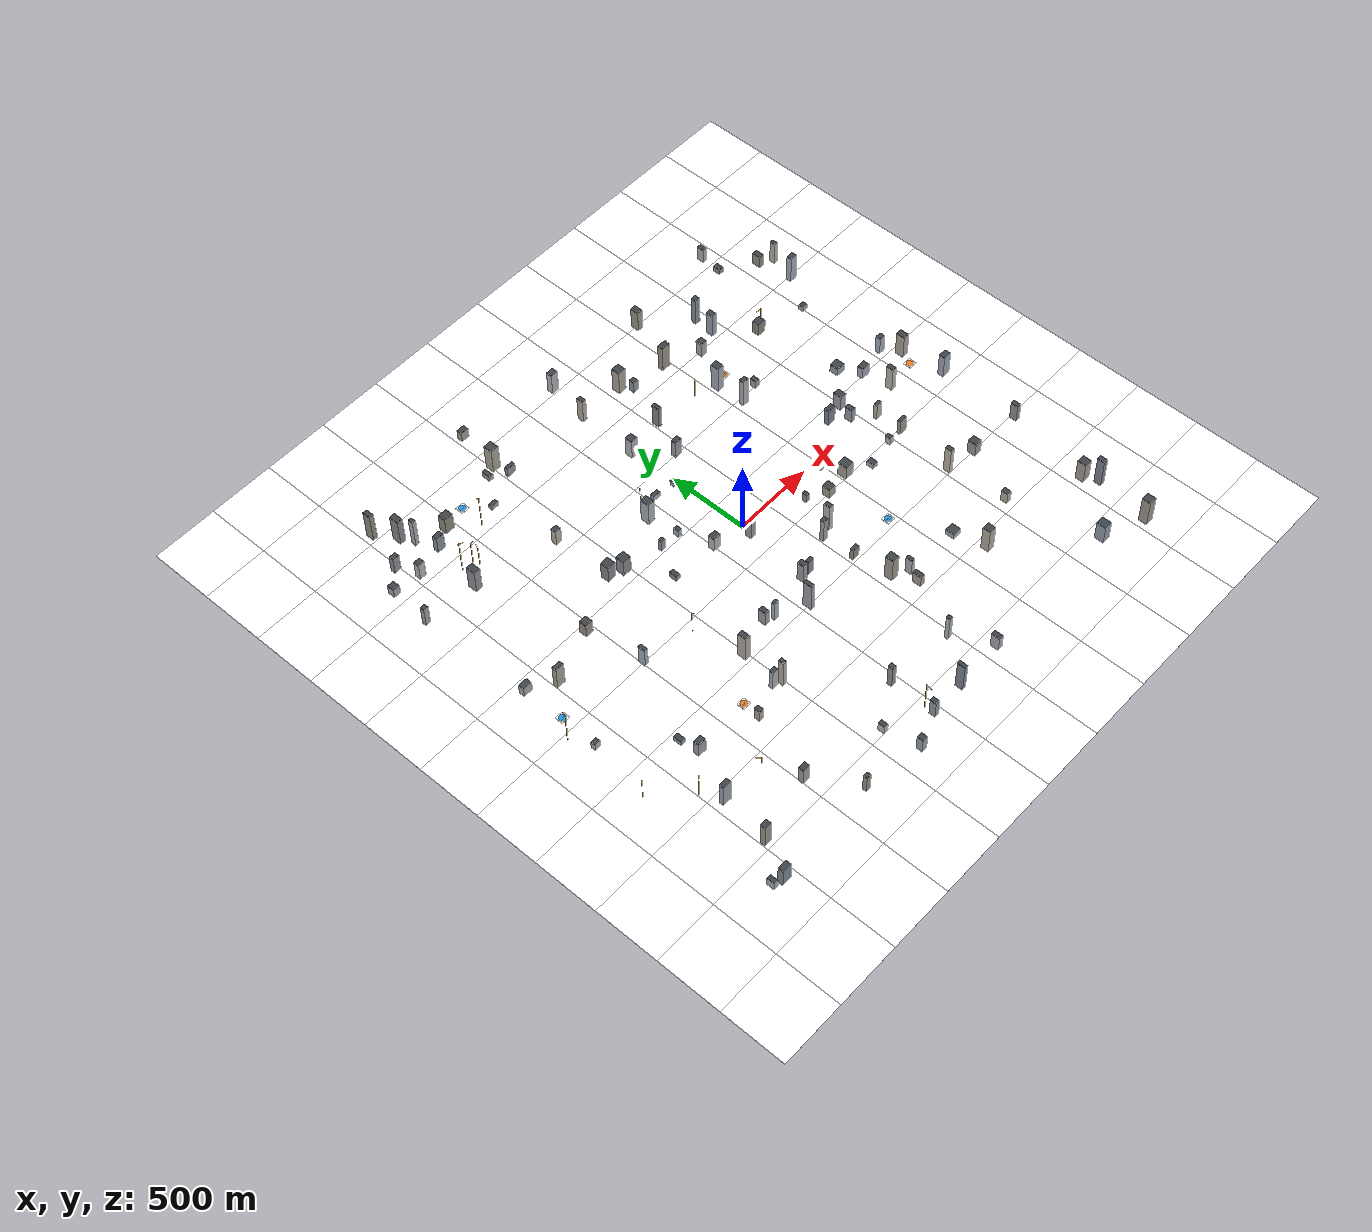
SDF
<?xml version='1.0'?>
<sdf version='1.9'>
<world name='urban'>
  <physics name='fast' type='ignored'>
    <max_step_size>0.005000</max_step_size>
    <real_time_factor>0</real_time_factor>
  </physics>
  <plugin filename='gz-sim-physics-system' name='gz::sim::systems::Physics'/>
  <plugin filename='gz-sim-user-commands-system'
          name='gz::sim::systems::UserCommands'/>
  <plugin filename='gz-sim-scene-broadcaster-system'
          name='gz::sim::systems::SceneBroadcaster'/>
  <plugin filename='gz-sim-sensors-system' name='gz::sim::systems::Sensors'>
    <render_engine>ogre2</render_engine>
  </plugin>
  <plugin filename='gz-sim-imu-system' name='gz::sim::systems::Imu'/>
  <plugin filename='PhyWamTraffic' name='phywam::PhyWamTraffic'>
    <seed>1</seed>
    <n_traffic>5</n_traffic>
    <n_suas>6</n_suas>
    <extent>1600.0</extent>
    <corridor_alt>120.0</corridor_alt>
    <namespace>phywam</namespace>
    <p_conflict>0.55</p_conflict>
    <buildings>-1170.0,1111.8,25.5,15.8,114.2 -161.6,485.1,26.0,12.8,34.8 1074.4,-215.1,25.5,11.0,105.7 708.9,-868.0,29.0,28.1,35.2 -1518.6,132.5,28.8,18.2,66.8 -249.2,-1507.1,15.2,19.3,114.3 -854.1,-861.2,15.2,19.7,79.3 -1531.2,1080.2,21.6,23.2,61.6 1576.1,1151.8,13.3,17.3,152.7 675.8,1396.6,19.0,26.8,144.0 -629.2,280.3,27.8,27.1,115.9 284.8,-1489.5,15.6,26.2,100.4 -1046.4,156.2,24.4,23.8,93.7 -195.3,27.0,25.8,20.9,96.9 -33.0,-1505.4,11.8,24.4,197.1 298.2,-340.5,14.2,20.5,197.0 865.7,126.8,27.3,15.4,117.3 1447.9,248.9,19.7,16.1,123.2 1462.8,-1581.7,25.9,26.6,180.7 769.6,989.2,20.9,21.7,102.4 -1420.4,1184.0,21.8,14.8,115.8 -48.2,-458.3,17.6,21.2,136.0 359.8,-133.9,11.5,15.4,60.1 270.3,1155.2,26.2,26.1,168.8 -783.1,1093.6,23.8,12.6,32.8 -1553.4,817.9,15.7,13.1,136.2 -497.8,-1377.6,14.0,21.0,58.6 -726.7,677.1,19.6,17.1,110.5 -1524.4,-363.0,19.0,14.6,48.5 1279.4,32.4,15.0,22.5,168.9 -1533.4,-1542.8,13.8,24.7,57.2 654.7,570.2,21.3,15.2,195.9 953.0,53.1,15.2,23.3,97.1 242.7,-572.0,23.0,12.1,80.8 1497.3,1201.7,16.8,27.3,82.8 1405.7,780.3,18.9,15.8,31.4 1211.9,-1478.7,26.6,29.3,126.9 -1051.1,1176.9,29.5,24.4,116.5 -390.5,-489.8,14.9,23.8,103.6 -978.8,-1265.8,23.7,16.6,115.0 -558.9,1189.2,28.1,11.3,64.1 -551.2,1558.6,25.9,17.4,66.2 558.3,1080.6,28.7,17.5,180.0 598.8,-49.6,29.7,15.5,153.3 -1329.0,-1057.0,28.3,15.0,159.0 320.7,1091.6,18.0,17.5,79.5 1175.7,332.7,29.1,27.9,53.0 163.7,-1266.3,11.7,12.4,177.2 922.0,1051.2,17.5,22.7,162.9 -390.3,226.5,15.3,12.6,75.3 1250.5,206.2,28.6,19.7,77.1 -1231.7,1232.2,11.8,15.6,198.0 -252.8,-1230.2,14.2,15.6,156.5 -1270.9,1314.4,18.2,29.4,184.6 -659.1,-789.1,20.1,12.9,140.8 -1473.2,-1566.4,29.7,16.6,131.4 -160.5,-597.5,12.2,28.4,194.9 1503.3,-1243.6,15.1,22.7,196.6 137.3,602.2,23.6,15.9,122.1 -616.6,-811.6,12.5,16.3,197.2 -618.3,-552.8,17.0,27.1,181.9 -815.7,-1534.8,15.6,12.4,123.7 -1373.1,-1359.6,23.1,16.5,164.7 -21.6,1160.5,13.9,20.5,165.1 -1353.3,1437.5,14.3,25.7,197.4 1029.0,-576.7,13.0,20.8,186.3 -660.8,1260.0,13.7,28.3,35.4 -588.6,1289.9,26.3,28.2,172.9 787.8,606.7,14.4,19.2,56.8 986.4,157.7,21.3,27.2,107.1 -333.7,-516.3,15.9,11.5,139.9 -266.6,225.9,12.2,17.7,53.5 -1199.6,-770.8,26.7,18.6,98.2 359.8,-852.7,11.1,21.0,115.2 476.3,-197.4,24.0,24.9,70.5 -15.8,-67.8,15.3,18.8,125.3 1302.2,1336.7,16.2,23.3,38.2 -1371.0,37.4,27.7,14.0,160.2 1225.6,-602.2,24.2,27.1,93.2 644.1,756.5,22.3,27.3,182.4 222.5,824.8,12.0,24.0,151.9 -486.5,48.2,14.1,24.9,36.9 1539.9,985.4,22.9,16.1,185.2 1470.2,-1154.8,25.7,27.0,142.2 641.3,-175.8,28.6,29.5,95.0 968.7,-214.7,14.1,17.2,51.5 1308.4,1470.2,13.3,22.4,99.4 -1222.1,-654.5,15.7,25.2,30.7 -992.5,-195.9,11.4,22.9,133.0 1073.1,-938.9,16.4,21.3,76.4 274.4,-797.2,24.0,26.0,167.5 1515.6,145.2,20.3,27.3,160.7 225.7,-373.6,16.4,13.1,167.3 -1222.2,791.2,21.4,29.3,159.4 9.7,-458.2,21.0,11.0,105.2 -24.6,472.5,18.2,14.9,30.7 -711.6,314.1,27.8,26.8,116.9 1558.5,-122.9,26.9,18.8,156.6 1560.3,-622.9,14.2,22.8,120.3 -449.8,-1588.7,18.4,19.1,98.9 -23.4,786.5,23.2,23.3,137.0 -297.6,413.6,23.0,28.8,163.0 1108.1,856.0,26.5,22.5,89.4 1065.5,-49.5,19.9,11.9,116.7 783.2,-247.7,17.7,23.5,33.4 22.9,1427.6,24.1,18.6,147.1 336.0,-931.6,14.9,27.8,75.7 -1360.4,1058.2,20.9,18.0,117.0 757.5,-1060.6,23.4,24.6,168.6 927.3,1173.5,17.3,15.2,193.8</buildings>
  </plugin>

  <gravity>0 0 -9.80665</gravity>
  <scene>
    <ambient>0.38 0.40 0.44 1</ambient>
    <background>0.46 0.60 0.78 1</background>
    <grid>false</grid><sky></sky>
  </scene>
  <light type='directional' name='sun'>
    <cast_shadows>true</cast_shadows>
    <pose>0 0 400 0 0 0</pose>
    <diffuse>0.88 0.86 0.80 1</diffuse><specular>0.18 0.18 0.18 1</specular>
    <direction>-0.42 0.38 -0.82</direction>
  </light>
  <model name='ground'><static>true</static>
    <link name='l'>
      <collision name='c'><geometry><plane><normal>0 0 1</normal>
      <size>9000 9000</size></plane></geometry></collision>
<visual name='g_0_0'><pose>-2000.0 -2000.0 -0.2 0 0 0</pose><geometry><box><size>400.0 400.0 0.4</size></box></geometry><material><ambient>0.5 0.5 0.5 1</ambient><diffuse>1.000 1.000 1.000 1</diffuse><specular>0.06 0.06 0.06 1</specular><pbr><metal><albedo_map>/home/glaze/Desktop/github_projects/Phy_WAM/sim/materials/textures/ground.png</albedo_map><metalness>0.0</metalness><roughness>0.95</roughness></metal></pbr></material></visual><visual name='g_1_0'><pose>-1600.0 -2000.0 -0.2 0 0 0</pose><geometry><box><size>400.0 400.0 0.4</size></box></geometry><material><ambient>0.5 0.5 0.5 1</ambient><diffuse>1.000 1.000 1.000 1</diffuse><specular>0.06 0.06 0.06 1</specular><pbr><metal><albedo_map>/home/glaze/Desktop/github_projects/Phy_WAM/sim/materials/textures/ground.png</albedo_map><metalness>0.0</metalness><roughness>0.95</roughness></metal></pbr></material></visual><visual name='g_2_0'><pose>-1200.0 -2000.0 -0.2 0 0 0</pose><geometry><box><size>400.0 400.0 0.4</size></box></geometry><material><ambient>0.5 0.5 0.5 1</ambient><diffuse>1.000 1.000 1.000 1</diffuse><specular>0.06 0.06 0.06 1</specular><pbr><metal><albedo_map>/home/glaze/Desktop/github_projects/Phy_WAM/sim/materials/textures/ground.png</albedo_map><metalness>0.0</metalness><roughness>0.95</roughness></metal></pbr></material></visual><visual name='g_3_0'><pose>-800.0 -2000.0 -0.2 0 0 0</pose><geometry><box><size>400.0 400.0 0.4</size></box></geometry><material><ambient>0.5 0.5 0.5 1</ambient><diffuse>1.000 1.000 1.000 1</diffuse><specular>0.06 0.06 0.06 1</specular><pbr><metal><albedo_map>/home/glaze/Desktop/github_projects/Phy_WAM/sim/materials/textures/ground.png</albedo_map><metalness>0.0</metalness><roughness>0.95</roughness></metal></pbr></material></visual><visual name='g_4_0'><pose>-400.0 -2000.0 -0.2 0 0 0</pose><geometry><box><size>400.0 400.0 0.4</size></box></geometry><material><ambient>0.5 0.5 0.5 1</ambient><diffuse>1.000 1.000 1.000 1</diffuse><specular>0.06 0.06 0.06 1</specular><pbr><metal><albedo_map>/home/glaze/Desktop/github_projects/Phy_WAM/sim/materials/textures/ground.png</albedo_map><metalness>0.0</metalness><roughness>0.95</roughness></metal></pbr></material></visual><visual name='g_5_0'><pose>0.0 -2000.0 -0.2 0 0 0</pose><geometry><box><size>400.0 400.0 0.4</size></box></geometry><material><ambient>0.5 0.5 0.5 1</ambient><diffuse>1.000 1.000 1.000 1</diffuse><specular>0.06 0.06 0.06 1</specular><pbr><metal><albedo_map>/home/glaze/Desktop/github_projects/Phy_WAM/sim/materials/textures/ground.png</albedo_map><metalness>0.0</metalness><roughness>0.95</roughness></metal></pbr></material></visual><visual name='g_6_0'><pose>400.0 -2000.0 -0.2 0 0 0</pose><geometry><box><size>400.0 400.0 0.4</size></box></geometry><material><ambient>0.5 0.5 0.5 1</ambient><diffuse>1.000 1.000 1.000 1</diffuse><specular>0.06 0.06 0.06 1</specular><pbr><metal><albedo_map>/home/glaze/Desktop/github_projects/Phy_WAM/sim/materials/textures/ground.png</albedo_map><metalness>0.0</metalness><roughness>0.95</roughness></metal></pbr></material></visual><visual name='g_7_0'><pose>800.0 -2000.0 -0.2 0 0 0</pose><geometry><box><size>400.0 400.0 0.4</size></box></geometry><material><ambient>0.5 0.5 0.5 1</ambient><diffuse>1.000 1.000 1.000 1</diffuse><specular>0.06 0.06 0.06 1</specular><pbr><metal><albedo_map>/home/glaze/Desktop/github_projects/Phy_WAM/sim/materials/textures/ground.png</albedo_map><metalness>0.0</metalness><roughness>0.95</roughness></metal></pbr></material></visual><visual name='g_8_0'><pose>1200.0 -2000.0 -0.2 0 0 0</pose><geometry><box><size>400.0 400.0 0.4</size></box></geometry><material><ambient>0.5 0.5 0.5 1</ambient><diffuse>1.000 1.000 1.000 1</diffuse><specular>0.06 0.06 0.06 1</specular><pbr><metal><albedo_map>/home/glaze/Desktop/github_projects/Phy_WAM/sim/materials/textures/ground.png</albedo_map><metalness>0.0</metalness><roughness>0.95</roughness></metal></pbr></material></visual><visual name='g_9_0'><pose>1600.0 -2000.0 -0.2 0 0 0</pose><geometry><box><size>400.0 400.0 0.4</size></box></geometry><material><ambient>0.5 0.5 0.5 1</ambient><diffuse>1.000 1.000 1.000 1</diffuse><specular>0.06 0.06 0.06 1</specular><pbr><metal><albedo_map>/home/glaze/Desktop/github_projects/Phy_WAM/sim/materials/textures/ground.png</albedo_map><metalness>0.0</metalness><roughness>0.95</roughness></metal></pbr></material></visual><visual name='g_10_0'><pose>2000.0 -2000.0 -0.2 0 0 0</pose><geometry><box><size>400.0 400.0 0.4</size></box></geometry><material><ambient>0.5 0.5 0.5 1</ambient><diffuse>1.000 1.000 1.000 1</diffuse><specular>0.06 0.06 0.06 1</specular><pbr><metal><albedo_map>/home/glaze/Desktop/github_projects/Phy_WAM/sim/materials/textures/ground.png</albedo_map><metalness>0.0</metalness><roughness>0.95</roughness></metal></pbr></material></visual><visual name='g_0_1'><pose>-2000.0 -1600.0 -0.2 0 0 0</pose><geometry><box><size>400.0 400.0 0.4</size></box></geometry><material><ambient>0.5 0.5 0.5 1</ambient><diffuse>1.000 1.000 1.000 1</diffuse><specular>0.06 0.06 0.06 1</specular><pbr><metal><albedo_map>/home/glaze/Desktop/github_projects/Phy_WAM/sim/materials/textures/ground.png</albedo_map><metalness>0.0</metalness><roughness>0.95</roughness></metal></pbr></material></visual><visual name='g_1_1'><pose>-1600.0 -1600.0 -0.2 0 0 0</pose><geometry><box><size>400.0 400.0 0.4</size></box></geometry><material><ambient>0.5 0.5 0.5 1</ambient><diffuse>1.000 1.000 1.000 1</diffuse><specular>0.06 0.06 0.06 1</specular><pbr><metal><albedo_map>/home/glaze/Desktop/github_projects/Phy_WAM/sim/materials/textures/ground.png</albedo_map><metalness>0.0</metalness><roughness>0.95</roughness></metal></pbr></material></visual><visual name='g_2_1'><pose>-1200.0 -1600.0 -0.2 0 0 0</pose><geometry><box><size>400.0 400.0 0.4</size></box></geometry><material><ambient>0.5 0.5 0.5 1</ambient><diffuse>1.000 1.000 1.000 1</diffuse><specular>0.06 0.06 0.06 1</specular><pbr><metal><albedo_map>/home/glaze/Desktop/github_projects/Phy_WAM/sim/materials/textures/ground.png</albedo_map><metalness>0.0</metalness><roughness>0.95</roughness></metal></pbr></material></visual><visual name='g_3_1'><pose>-800.0 -1600.0 -0.2 0 0 0</pose><geometry><box><size>400.0 400.0 0.4</size></box></geometry><material><ambient>0.5 0.5 0.5 1</ambient><diffuse>1.000 1.000 1.000 1</diffuse><specular>0.06 0.06 0.06 1</specular><pbr><metal><albedo_map>/home/glaze/Desktop/github_projects/Phy_WAM/sim/materials/textures/ground.png</albedo_map><metalness>0.0</metalness><roughness>0.95</roughness></metal></pbr></material></visual><visual name='g_4_1'><pose>-400.0 -1600.0 -0.2 0 0 0</pose><geometry><box><size>400.0 400.0 0.4</size></box></geometry><material><ambient>0.5 0.5 0.5 1</ambient><diffuse>1.000 1.000 1.000 1</diffuse><specular>0.06 0.06 0.06 1</specular><pbr><metal><albedo_map>/home/glaze/Desktop/github_projects/Phy_WAM/sim/materials/textures/ground.png</albedo_map><metalness>0.0</metalness><roughness>0.95</roughness></metal></pbr></material></visual><visual name='g_5_1'><pose>0.0 -1600.0 -0.2 0 0 0</pose><geometry><box><size>400.0 400.0 0.4</size></box></geometry><material><ambient>0.5 0.5 0.5 1</ambient><diffuse>1.000 1.000 1.000 1</diffuse><specular>0.06 0.06 0.06 1</specular><pbr><metal><albedo_map>/home/glaze/Desktop/github_projects/Phy_WAM/sim/materials/textures/ground.png</albedo_map><metalness>0.0</metalness><roughness>0.95</roughness></metal></pbr></material></visual><visual name='g_6_1'><pose>400.0 -1600.0 -0.2 0 0 0</pose><geometry><box><size>400.0 400.0 0.4</size></box></geometry><material><ambient>0.5 0.5 0.5 1</ambient><diffuse>1.000 1.000 1.000 1</diffuse><specular>0.06 0.06 0.06 1</specular><pbr><metal><albedo_map>/home/glaze/Desktop/github_projects/Phy_WAM/sim/materials/textures/ground.png</albedo_map><metalness>0.0</metalness><roughness>0.95</roughness></metal></pbr></material></visual><visual name='g_7_1'><pose>800.0 -1600.0 -0.2 0 0 0</pose><geometry><box><size>400.0 400.0 0.4</size></box></geometry><material><ambient>0.5 0.5 0.5 1</ambient><diffuse>1.000 1.000 1.000 1</diffuse><specular>0.06 0.06 0.06 1</specular><pbr><metal><albedo_map>/home/glaze/Desktop/github_projects/Phy_WAM/sim/materials/textures/ground.png</albedo_map><metalness>0.0</metalness><roughness>0.95</roughness></metal></pbr></material></visual><visual name='g_8_1'><pose>1200.0 -1600.0 -0.2 0 0 0</pose><geometry><box><size>400.0 400.0 0.4</size></box></geometry><material><ambient>0.5 0.5 0.5 1</ambient><diffuse>1.000 1.000 1.000 1</diffuse><specular>0.06 0.06 0.06 1</specular><pbr><metal><albedo_map>/home/glaze/Desktop/github_projects/Phy_WAM/sim/materials/textures/ground.png</albedo_map><metalness>0.0</metalness><roughness>0.95</roughness></metal></pbr></material></visual><visual name='g_9_1'><pose>1600.0 -1600.0 -0.2 0 0 0</pose><geometry><box><size>400.0 400.0 0.4</size></box></geometry><material><ambient>0.5 0.5 0.5 1</ambient><diffuse>1.000 1.000 1.000 1</diffuse><specular>0.06 0.06 0.06 1</specular><pbr><metal><albedo_map>/home/glaze/Desktop/github_projects/Phy_WAM/sim/materials/textures/ground.png</albedo_map><metalness>0.0</metalness><roughness>0.95</roughness></metal></pbr></material></visual><visual name='g_10_1'><pose>2000.0 -1600.0 -0.2 0 0 0</pose><geometry><box><size>400.0 400.0 0.4</size></box></geometry><material><ambient>0.5 0.5 0.5 1</ambient><diffuse>1.000 1.000 1.000 1</diffuse><specular>0.06 0.06 0.06 1</specular><pbr><metal><albedo_map>/home/glaze/Desktop/github_projects/Phy_WAM/sim/materials/textures/ground.png</albedo_map><metalness>0.0</metalness><roughness>0.95</roughness></metal></pbr></material></visual><visual name='g_0_2'><pose>-2000.0 -1200.0 -0.2 0 0 0</pose><geometry><box><size>400.0 400.0 0.4</size></box></geometry><material><ambient>0.5 0.5 0.5 1</ambient><diffuse>1.000 1.000 1.000 1</diffuse><specular>0.06 0.06 0.06 1</specular><pbr><metal><albedo_map>/home/glaze/Desktop/github_projects/Phy_WAM/sim/materials/textures/ground.png</albedo_map><metalness>0.0</metalness><roughness>0.95</roughness></metal></pbr></material></visual><visual name='g_1_2'><pose>-1600.0 -1200.0 -0.2 0 0 0</pose><geometry><box><size>400.0 400.0 0.4</size></box></geometry><material><ambient>0.5 0.5 0.5 1</ambient><diffuse>1.000 1.000 1.000 1</diffuse><specular>0.06 0.06 0.06 1</specular><pbr><metal><albedo_map>/home/glaze/Desktop/github_projects/Phy_WAM/sim/materials/textures/ground.png</albedo_map><metalness>0.0</metalness><roughness>0.95</roughness></metal></pbr></material></visual><visual name='g_2_2'><pose>-1200.0 -1200.0 -0.2 0 0 0</pose><geometry><box><size>400.0 400.0 0.4</size></box></geometry><material><ambient>0.5 0.5 0.5 1</ambient><diffuse>1.000 1.000 1.000 1</diffuse><specular>0.06 0.06 0.06 1</specular><pbr><metal><albedo_map>/home/glaze/Desktop/github_projects/Phy_WAM/sim/materials/textures/ground.png</albedo_map><metalness>0.0</metalness><roughness>0.95</roughness></metal></pbr></material></visual><visual name='g_3_2'><pose>-800.0 -1200.0 -0.2 0 0 0</pose><geometry><box><size>400.0 400.0 0.4</size></box></geometry><material><ambient>0.5 0.5 0.5 1</ambient><diffuse>1.000 1.000 1.000 1</diffuse><specular>0.06 0.06 0.06 1</specular><pbr><metal><albedo_map>/home/glaze/Desktop/github_projects/Phy_WAM/sim/materials/textures/ground.png</albedo_map><metalness>0.0</metalness><roughness>0.95</roughness></metal></pbr></material></visual><visual name='g_4_2'><pose>-400.0 -1200.0 -0.2 0 0 0</pose><geometry><box><size>400.0 400.0 0.4</size></box></geometry><material><ambient>0.5 0.5 0.5 1</ambient><diffuse>1.000 1.000 1.000 1</diffuse><specular>0.06 0.06 0.06 1</specular><pbr><metal><albedo_map>/home/glaze/Desktop/github_projects/Phy_WAM/sim/materials/textures/ground.png</albedo_map><metalness>0.0</metalness><roughness>0.95</roughness></metal></pbr></material></visual><visual name='g_5_2'><pose>0.0 -1200.0 -0.2 0 0 0</pose><geometry><box><size>400.0 400.0 0.4</size></box></geometry><material><ambient>0.5 0.5 0.5 1</ambient><diffuse>1.000 1.000 1.000 1</diffuse><specular>0.06 0.06 0.06 1</specular><pbr><metal><albedo_map>/home/glaze/Desktop/github_projects/Phy_WAM/sim/materials/textures/ground.png</albedo_map><metalness>0.0</metalness><roughness>0.95</roughness></metal></pbr></material></visual><visual name='g_6_2'><pose>400.0 -1200.0 -0.2 0 0 0</pose><geometry><box><size>400.0 400.0 0.4</size></box></geometry><material><ambient>0.5 0.5 0.5 1</ambient><diffuse>1.000 1.000 1.000 1</diffuse><specular>0.06 0.06 0.06 1</specular><pbr><metal><albedo_map>/home/glaze/Desktop/github_projects/Phy_WAM/sim/materials/textures/ground.png</albedo_map><metalness>0.0</metalness><roughness>0.95</roughness></metal></pbr></material></visual><visual name='g_7_2'><pose>800.0 -1200.0 -0.2 0 0 0</pose><geometry><box><size>400.0 400.0 0.4</size></box></geometry><material><ambient>0.5 0.5 0.5 1</ambient><diffuse>1.000 1.000 1.000 1</diffuse><specular>0.06 0.06 0.06 1</specular><pbr><metal><albedo_map>/home/glaze/Desktop/github_projects/Phy_WAM/sim/materials/textures/ground.png</albedo_map><metalness>0.0</metalness><roughness>0.95</roughness></metal></pbr></material></visual><visual name='g_8_2'><pose>1200.0 -1200.0 -0.2 0 0 0</pose><geometry><box><size>400.0 400.0 0.4</size></box></geometry><material><ambient>0.5 0.5 0.5 1</ambient><diffuse>1.000 1.000 1.000 1</diffuse><specular>0.06 0.06 0.06 1</specular><pbr><metal><albedo_map>/home/glaze/Desktop/github_projects/Phy_WAM/sim/materials/textures/ground.png</albedo_map><metalness>0.0</metalness><roughness>0.95</roughness></metal></pbr></material></visual><visual name='g_9_2'><pose>1600.0 -1200.0 -0.2 0 0 0</pose><geometry><box><size>400.0 400.0 0.4</size></box></geometry><material><ambient>0.5 0.5 0.5 1</ambient><diffuse>1.000 1.000 1.000 1</diffuse><specular>0.06 0.06 0.06 1</specular><pbr><metal><albedo_map>/home/glaze/Desktop/github_projects/Phy_WAM/sim/materials/textures/ground.png</albedo_map><metalness>0.0</metalness><roughness>0.95</roughness></metal></pbr></material></visual><visual name='g_10_2'><pose>2000.0 -1200.0 -0.2 0 0 0</pose><geometry><box><size>400.0 400.0 0.4</size></box></geometry><material><ambient>0.5 0.5 0.5 1</ambient><diffuse>1.000 1.000 1.000 1</diffuse><specular>0.06 0.06 0.06 1</specular><pbr><metal><albedo_map>/home/glaze/Desktop/github_projects/Phy_WAM/sim/materials/textures/ground.png</albedo_map><metalness>0.0</metalness><roughness>0.95</roughness></metal></pbr></material></visual><visual name='g_0_3'><pose>-2000.0 -800.0 -0.2 0 0 0</pose><geometry><box><size>400.0 400.0 0.4</size></box></geometry><material><ambient>0.5 0.5 0.5 1</ambient><diffuse>1.000 1.000 1.000 1</diffuse><specular>0.06 0.06 0.06 1</specular><pbr><metal><albedo_map>/home/glaze/Desktop/github_projects/Phy_WAM/sim/materials/textures/ground.png</albedo_map><metalness>0.0</metalness><roughness>0.95</roughness></metal></pbr></material></visual><visual name='g_1_3'><pose>-1600.0 -800.0 -0.2 0 0 0</pose><geometry><box><size>400.0 400.0 0.4</size></box></geometry><material><ambient>0.5 0.5 0.5 1</ambient><diffuse>1.000 1.000 1.000 1</diffuse><specular>0.06 0.06 0.06 1</specular><pbr><metal><albedo_map>/home/glaze/Desktop/github_projects/Phy_WAM/sim/materials/textures/ground.png</albedo_map><metalness>0.0</metalness><roughness>0.95</roughness></metal></pbr></material></visual><visual name='g_2_3'><pose>-1200.0 -800.0 -0.2 0 0 0</pose><geometry><box><size>400.0 400.0 0.4</size></box></geometry><material><ambient>0.5 0.5 0.5 1</ambient><diffuse>1.000 1.000 1.000 1</diffuse><specular>0.06 0.06 0.06 1</specular><pbr><metal><albedo_map>/home/glaze/Desktop/github_projects/Phy_WAM/sim/materials/textures/ground.png</albedo_map><metalness>0.0</metalness><roughness>0.95</roughness></metal></pbr></material></visual><visual name='g_3_3'><pose>-800.0 -800.0 -0.2 0 0 0</pose><geometry><box><size>400.0 400.0 0.4</size></box></geometry><material><ambient>0.5 0.5 0.5 1</ambient><diffuse>1.000 1.000 1.000 1</diffuse><specular>0.06 0.06 0.06 1</specular><pbr><metal><albedo_map>/home/glaze/Desktop/github_projects/Phy_WAM/sim/materials/textures/ground.png</albedo_map><metalness>0.0</metalness><roughness>0.95</roughness></metal></pbr></material></visual><visual name='g_4_3'><pose>-400.0 -800.0 -0.2 0 0 0</pose><geometry><box><size>400.0 400.0 0.4</size></box></geometry><material><ambient>0.5 0.5 0.5 1</ambient><diffuse>1.000 1.000 1.000 1</diffuse><specular>0.06 0.06 0.06 1</specular><pbr><metal><albedo_map>/home/glaze/Desktop/github_projects/Phy_WAM/sim/materials/textures/ground.png</albedo_map><metalness>0.0</metalness><roughness>0.95</roughness></metal></pbr></material></visual><visual name='g_5_3'><pose>0.0 -800.0 -0.2 0 0 0</pose><geometry><box><size>400.0 400.0 0.4</size></box></geometry><material><ambient>0.5 0.5 0.5 1</ambient><diffuse>1.000 1.000 1.000 1</diffuse><specular>0.06 0.06 0.06 1</specular><pbr><metal><albedo_map>/home/glaze/Desktop/github_projects/Phy_WAM/sim/materials/textures/ground.png</albedo_map><metalness>0.0</metalness><roughness>0.95</roughness></metal></pbr></material></visual><visual name='g_6_3'><pose>400.0 -800.0 -0.2 0 0 0</pose><geometry><box><size>400.0 400.0 0.4</size></box></geometry><material><ambient>0.5 0.5 0.5 1</ambient><diffuse>1.000 1.000 1.000 1</diffuse><specular>0.06 0.06 0.06 1</specular><pbr><metal><albedo_map>/home/glaze/Desktop/github_projects/Phy_WAM/sim/materials/textures/ground.png</albedo_map><metalness>0.0</metalness><roughness>0.95</roughness></metal></pbr></material></visual><visual name='g_7_3'><pose>800.0 -800.0 -0.2 0 0 0</pose><geometry><box><size>400.0 400.0 0.4</size></box></geometry><material><ambient>0.5 0.5 0.5 1</ambient><diffuse>1.000 1.000 1.000 1</diffuse><specular>0.06 0.06 0.06 1</specular><pbr><metal><albedo_map>/home/glaze/Desktop/github_projects/Phy_WAM/sim/materials/textures/ground.png</albedo_map><metalness>0.0</metalness><roughness>0.95</roughness></metal></pbr></material></visual><visual name='g_8_3'><pose>1200.0 -800.0 -0.2 0 0 0</pose><geometry><box><size>400.0 400.0 0.4</size></box></geometry><material><ambient>0.5 0.5 0.5 1</ambient><diffuse>1.000 1.000 1.000 1</diffuse><specular>0.06 0.06 0.06 1</specular><pbr><metal><albedo_map>/home/glaze/Desktop/github_projects/Phy_WAM/sim/materials/textures/ground.png</albedo_map><metalness>0.0</metalness><roughness>0.95</roughness></metal></pbr></material></visual><visual name='g_9_3'><pose>1600.0 -800.0 -0.2 0 0 0</pose><geometry><box><size>400.0 400.0 0.4</size></box></geometry><material><ambient>0.5 0.5 0.5 1</ambient><diffuse>1.000 1.000 1.000 1</diffuse><specular>0.06 0.06 0.06 1</specular><pbr><metal><albedo_map>/home/glaze/Desktop/github_projects/Phy_WAM/sim/materials/textures/ground.png</albedo_map><metalness>0.0</metalness><roughness>0.95</roughness></metal></pbr></material></visual><visual name='g_10_3'><pose>2000.0 -800.0 -0.2 0 0 0</pose><geometry><box><size>400.0 400.0 0.4</size></box></geometry><material><ambient>0.5 0.5 0.5 1</ambient><diffuse>1.000 1.000 1.000 1</diffuse><specular>0.06 0.06 0.06 1</specular><pbr><metal><albedo_map>/home/glaze/Desktop/github_projects/Phy_WAM/sim/materials/textures/ground.png</albedo_map><metalness>0.0</metalness><roughness>0.95</roughness></metal></pbr></material></visual><visual name='g_0_4'><pose>-2000.0 -400.0 -0.2 0 0 0</pose><geometry><box><size>400.0 400.0 0.4</size></box></geometry><material><ambient>0.5 0.5 0.5 1</ambient><diffuse>1.000 1.000 1.000 1</diffuse><specular>0.06 0.06 0.06 1</specular><pbr><metal><albedo_map>/home/glaze/Desktop/github_projects/Phy_WAM/sim/materials/textures/ground.png</albedo_map><metalness>0.0</metalness><roughness>0.95</roughness></metal></pbr></material></visual><visual name='g_1_4'><pose>-1600.0 -400.0 -0.2 0 0 0</pose><geometry><box><size>400.0 400.0 0.4</size></box></geometry><material><ambient>0.5 0.5 0.5 1</ambient><diffuse>1.000 1.000 1.000 1</diffuse><specular>0.06 0.06 0.06 1</specular><pbr><metal><albedo_map>/home/glaze/Desktop/github_projects/Phy_WAM/sim/materials/textures/ground.png</albedo_map><metalness>0.0</metalness><roughness>0.95</roughness></metal></pbr></material></visual><visual name='g_2_4'><pose>-1200.0 -400.0 -0.2 0 0 0</pose><geometry><box><size>400.0 400.0 0.4</size></box></geometry><material><ambient>0.5 0.5 0.5 1</ambient><diffuse>1.000 1.000 1.000 1</diffuse><specular>0.06 0.06 0.06 1</specular><pbr><metal><albedo_map>/home/glaze/Desktop/github_projects/Phy_WAM/sim/materials/textures/ground.png</albedo_map><metalness>0.0</metalness><roughness>0.95</roughness></metal></pbr></material></visual><visual name='g_3_4'><pose>-800.0 -400.0 -0.2 0 0 0</pose><geometry><box><size>400.0 400.0 0.4</size></box></geometry><material><ambient>0.5 0.5 0.5 1</ambient><diffuse>1.000 1.000 1.000 1</diffuse><specular>0.06 0.06 0.06 1</specular><pbr><metal><albedo_map>/home/glaze/Desktop/github_projects/Phy_WAM/sim/materials/textures/ground.png</albedo_map><metalness>0.0</metalness><roughness>0.95</roughness></metal></pbr></material></visual><visual name='g_4_4'><pose>-400.0 -400.0 -0.2 0 0 0</pose><geometry><box><size>400.0 400.0 0.4</size></box></geometry><material><ambient>0.5 0.5 0.5 1</ambient><diffuse>1.000 1.000 1.000 1</diffuse><specular>0.06 0.06 0.06 1</specular><pbr><metal><albedo_map>/home/glaze/Desktop/github_projects/Phy_WAM/sim/materials/textures/ground.png</albedo_map><metalness>0.0</metalness><roughness>0.95</roughness></metal></pbr></material></visual><visual name='g_5_4'><pose>0.0 -400.0 -0.2 0 0 0</pose><geometry><box><size>400.0 400.0 0.4</size></box></geometry><material><ambient>0.5 0.5 0.5 1</ambient><diffuse>1.000 1.000 1.000 1</diffuse><specular>0.06 0.06 0.06 1</specular><pbr><metal><albedo_map>/home/glaze/Desktop/github_projects/Phy_WAM/sim/materials/textures/ground.png</albedo_map><metalness>0.0</metalness><roughness>0.95</roughness></metal></pbr></material></visual><visual name='g_6_4'><pose>400.0 -400.0 -0.2 0 0 0</pose><geometry><box><size>400.0 400.0 0.4</size></box></geometry><material><ambient>0.5 0.5 0.5 1</ambient><diffuse>1.000 1.000 1.000 1</diffuse><specular>0.06 0.06 0.06 1</specular><pbr><metal><albedo_map>/home/glaze/Desktop/github_projects/Phy_WAM/sim/materials/textures/ground.png</albedo_map><metalness>0.0</metalness><roughness>0.95</roughness></metal></pbr></material></visual><visual name='g_7_4'><pose>800.0 -400.0 -0.2 0 0 0</pose><geometry><box><size>400.0 400.0 0.4</size></box></geometry><material><ambient>0.5 0.5 0.5 1</ambient><diffuse>1.000 1.000 1.000 1</diffuse><specular>0.06 0.06 0.06 1</specular><pbr><metal><albedo_map>/home/glaze/Desktop/github_projects/Phy_WAM/sim/materials/textures/ground.png</albedo_map><metalness>0.0</metalness><roughness>0.95</roughness></metal></pbr></material></visual><visual name='g_8_4'><pose>1200.0 -400.0 -0.2 0 0 0</pose><geometry><box><size>400.0 400.0 0.4</size></box></geometry><material><ambient>0.5 0.5 0.5 1</ambient><diffuse>1.000 1.000 1.000 1</diffuse><specular>0.06 0.06 0.06 1</specular><pbr><metal><albedo_map>/home/glaze/Desktop/github_projects/Phy_WAM/sim/materials/textures/ground.png</albedo_map><metalness>0.0</metalness><roughness>0.95</roughness></metal></pbr></material></visual><visual name='g_9_4'><pose>1600.0 -400.0 -0.2 0 0 0</pose><geometry><box><size>400.0 400.0 0.4</size></box></geometry><material><ambient>0.5 0.5 0.5 1</ambient><diffuse>1.000 1.000 1.000 1</diffuse><specular>0.06 0.06 0.06 1</specular><pbr><metal><albedo_map>/home/glaze/Desktop/github_projects/Phy_WAM/sim/materials/textures/ground.png</albedo_map><metalness>0.0</metalness><roughness>0.95</roughness></metal></pbr></material></visual><visual name='g_10_4'><pose>2000.0 -400.0 -0.2 0 0 0</pose><geometry><box><size>400.0 400.0 0.4</size></box></geometry><material><ambient>0.5 0.5 0.5 1</ambient><diffuse>1.000 1.000 1.000 1</diffuse><specular>0.06 0.06 0.06 1</specular><pbr><metal><albedo_map>/home/glaze/Desktop/github_projects/Phy_WAM/sim/materials/textures/ground.png</albedo_map><metalness>0.0</metalness><roughness>0.95</roughness></metal></pbr></material></visual><visual name='g_0_5'><pose>-2000.0 0.0 -0.2 0 0 0</pose><geometry><box><size>400.0 400.0 0.4</size></box></geometry><material><ambient>0.5 0.5 0.5 1</ambient><diffuse>1.000 1.000 1.000 1</diffuse><specular>0.06 0.06 0.06 1</specular><pbr><metal><albedo_map>/home/glaze/Desktop/github_projects/Phy_WAM/sim/materials/textures/ground.png</albedo_map><metalness>0.0</metalness><roughness>0.95</roughness></metal></pbr></material></visual><visual name='g_1_5'><pose>-1600.0 0.0 -0.2 0 0 0</pose><geometry><box><size>400.0 400.0 0.4</size></box></geometry><material><ambient>0.5 0.5 0.5 1</ambient><diffuse>1.000 1.000 1.000 1</diffuse><specular>0.06 0.06 0.06 1</specular><pbr><metal><albedo_map>/home/glaze/Desktop/github_projects/Phy_WAM/sim/materials/textures/ground.png</albedo_map><metalness>0.0</metalness><roughness>0.95</roughness></metal></pbr></material></visual><visual name='g_2_5'><pose>-1200.0 0.0 -0.2 0 0 0</pose><geometry><box><size>400.0 400.0 0.4</size></box></geometry><material><ambient>0.5 0.5 0.5 1</ambient><diffuse>1.000 1.000 1.000 1</diffuse><specular>0.06 0.06 0.06 1</specular><pbr><metal><albedo_map>/home/glaze/Desktop/github_projects/Phy_WAM/sim/materials/textures/ground.png</albedo_map><metalness>0.0</metalness><roughness>0.95</roughness></metal></pbr></material></visual><visual name='g_3_5'><pose>-800.0 0.0 -0.2 0 0 0</pose><geometry><box><size>400.0 400.0 0.4</size></box></geometry><material><ambient>0.5 0.5 0.5 1</ambient><diffuse>1.000 1.000 1.000 1</diffuse><specular>0.06 0.06 0.06 1</specular><pbr><metal><albedo_map>/home/glaze/Desktop/github_projects/Phy_WAM/sim/materials/textures/ground.png</albedo_map><metalness>0.0</metalness><roughness>0.95</roughness></metal></pbr></material></visual><visual name='g_4_5'><pose>-400.0 0.0 -0.2 0 0 0</pose><geometry><box><size>400.0 400.0 0.4</size></box></geometry><material><ambient>0.5 0.5 0.5 1</ambient><diffuse>1.000 1.000 1.000 1</diffuse><specular>0.06 0.06 0.06 1</specular><pbr><metal><albedo_map>/home/glaze/Desktop/github_projects/Phy_WAM/sim/materials/textures/ground.png</albedo_map><metalness>0.0</metalness><roughness>0.95</roughness></metal></pbr></material></visual><visual name='g_5_5'><pose>0.0 0.0 -0.2 0 0 0</pose><geometry><box><size>400.0 400.0 0.4</size></box></geometry><material><ambient>0.5 0.5 0.5 1</ambient><diffuse>1.000 1.000 1.000 1</diffuse><specular>0.06 0.06 0.06 1</specular><pbr><metal><albedo_map>/home/glaze/Desktop/github_projects/Phy_WAM/sim/materials/textures/ground.png</albedo_map><metalness>0.0</metalness><roughness>0.95</roughness></metal></pbr></material></visual><visual name='g_6_5'><pose>400.0 0.0 -0.2 0 0 0</pose><geometry><box><size>400.0 400.0 0.4</size></box></geometry><material><ambient>0.5 0.5 0.5 1</ambient><diffuse>1.000 1.000 1.000 1</diffuse><specular>0.06 0.06 0.06 1</specular><pbr><metal><albedo_map>/home/glaze/Desktop/github_projects/Phy_WAM/sim/materials/textures/ground.png</albedo_map><metalness>0.0</metalness><roughness>0.95</roughness></metal></pbr></material></visual><visual name='g_7_5'><pose>800.0 0.0 -0.2 0 0 0</pose><geometry><box><size>400.0 400.0 0.4</size></box></geometry><material><ambient>0.5 0.5 0.5 1</ambient><diffuse>1.000 1.000 1.000 1</diffuse><specular>0.06 0.06 0.06 1</specular><pbr><metal><albedo_map>/home/glaze/Desktop/github_projects/Phy_WAM/sim/materials/textures/ground.png</albedo_map><metalness>0.0</metalness><roughness>0.95</roughness></metal></pbr></material></visual><visual name='g_8_5'><pose>1200.0 0.0 -0.2 0 0 0</pose><geometry><box><size>400.0 400.0 0.4</size></box></geometry><material><ambient>0.5 0.5 0.5 1</ambient><diffuse>1.000 1.000 1.000 1</diffuse><specular>0.06 0.06 0.06 1</specular><pbr><metal><albedo_map>/home/glaze/Desktop/github_projects/Phy_WAM/sim/materials/textures/ground.png</albedo_map><metalness>0.0</metalness><roughness>0.95</roughness></metal></pbr></material></visual><visual name='g_9_5'><pose>1600.0 0.0 -0.2 0 0 0</pose><geometry><box><size>400.0 400.0 0.4</size></box></geometry><material><ambient>0.5 0.5 0.5 1</ambient><diffuse>1.000 1.000 1.000 1</diffuse><specular>0.06 0.06 0.06 1</specular><pbr><metal><albedo_map>/home/glaze/Desktop/github_projects/Phy_WAM/sim/materials/textures/ground.png</albedo_map><metalness>0.0</metalness><roughness>0.95</roughness></metal></pbr></material></visual><visual name='g_10_5'><pose>2000.0 0.0 -0.2 0 0 0</pose><geometry><box><size>400.0 400.0 0.4</size></box></geometry><material><ambient>0.5 0.5 0.5 1</ambient><diffuse>1.000 1.000 1.000 1</diffuse><specular>0.06 0.06 0.06 1</specular><pbr><metal><albedo_map>/home/glaze/Desktop/github_projects/Phy_WAM/sim/materials/textures/ground.png</albedo_map><metalness>0.0</metalness><roughness>0.95</roughness></metal></pbr></material></visual><visual name='g_0_6'><pose>-2000.0 400.0 -0.2 0 0 0</pose><geometry><box><size>400.0 400.0 0.4</size></box></geometry><material><ambient>0.5 0.5 0.5 1</ambient><diffuse>1.000 1.000 1.000 1</diffuse><specular>0.06 0.06 0.06 1</specular><pbr><metal><albedo_map>/home/glaze/Desktop/github_projects/Phy_WAM/sim/materials/textures/ground.png</albedo_map><metalness>0.0</metalness><roughness>0.95</roughness></metal></pbr></material></visual><visual name='g_1_6'><pose>-1600.0 400.0 -0.2 0 0 0</pose><geometry><box><size>400.0 400.0 0.4</size></box></geometry><material><ambient>0.5 0.5 0.5 1</ambient><diffuse>1.000 1.000 1.000 1</diffuse><specular>0.06 0.06 0.06 1</specular><pbr><metal><albedo_map>/home/glaze/Desktop/github_projects/Phy_WAM/sim/materials/textures/ground.png</albedo_map><metalness>0.0</metalness><roughness>0.95</roughness></metal></pbr></material></visual><visual name='g_2_6'><pose>-1200.0 400.0 -0.2 0 0 0</pose><geometry><box><size>400.0 400.0 0.4</size></box></geometry><material><ambient>0.5 0.5 0.5 1</ambient><diffuse>1.000 1.000 1.000 1</diffuse><specular>0.06 0.06 0.06 1</specular><pbr><metal><albedo_map>/home/glaze/Desktop/github_projects/Phy_WAM/sim/materials/textures/ground.png</albedo_map><metalness>0.0</metalness><roughness>0.95</roughness></metal></pbr></material></visual><visual name='g_3_6'><pose>-800.0 400.0 -0.2 0 0 0</pose><geometry><box><size>400.0 400.0 0.4</size></box></geometry><material><ambient>0.5 0.5 0.5 1</ambient><diffuse>1.000 1.000 1.000 1</diffuse><specular>0.06 0.06 0.06 1</specular><pbr><metal><albedo_map>/home/glaze/Desktop/github_projects/Phy_WAM/sim/materials/textures/ground.png</albedo_map><metalness>0.0</metalness><roughness>0.95</roughness></metal></pbr></material></visual><visual name='g_4_6'><pose>-400.0 400.0 -0.2 0 0 0</pose><geometry><box><size>400.0 400.0 0.4</size></box></geometry><material><ambient>0.5 0.5 0.5 1</ambient><diffuse>1.000 1.000 1.000 1</diffuse><specular>0.06 0.06 0.06 1</specular><pbr><metal><albedo_map>/home/glaze/Desktop/github_projects/Phy_WAM/sim/materials/textures/ground.png</albedo_map><metalness>0.0</metalness><roughness>0.95</roughness></metal></pbr></material></visual><visual name='g_5_6'><pose>0.0 400.0 -0.2 0 0 0</pose><geometry><box><size>400.0 400.0 0.4</size></box></geometry><material><ambient>0.5 0.5 0.5 1</ambient><diffuse>1.000 1.000 1.000 1</diffuse><specular>0.06 0.06 0.06 1</specular><pbr><metal><albedo_map>/home/glaze/Desktop/github_projects/Phy_WAM/sim/materials/textures/ground.png</albedo_map><metalness>0.0</metalness><roughness>0.95</roughness></metal></pbr></material></visual><visual name='g_6_6'><pose>400.0 400.0 -0.2 0 0 0</pose><geometry><box><size>400.0 400.0 0.4</size></box></geometry><material><ambient>0.5 0.5 0.5 1</ambient><diffuse>1.000 1.000 1.000 1</diffuse><specular>0.06 0.06 0.06 1</specular><pbr><metal><albedo_map>/home/glaze/Desktop/github_projects/Phy_WAM/sim/materials/textures/ground.png</albedo_map><metalness>0.0</metalness><roughness>0.95</roughness></metal></pbr></material></visual><visual name='g_7_6'><pose>800.0 400.0 -0.2 0 0 0</pose><geometry><box><size>400.0 400.0 0.4</size></box></geometry><material><ambient>0.5 0.5 0.5 1</ambient><diffuse>1.000 1.000 1.000 1</diffuse><specular>0.06 0.06 0.06 1</specular><pbr><metal><albedo_map>/home/glaze/Desktop/github_projects/Phy_WAM/sim/materials/textures/ground.png</albedo_map><metalness>0.0</metalness><roughness>0.95</roughness></metal></pbr></material></visual><visual name='g_8_6'><pose>1200.0 400.0 -0.2 0 0 0</pose><geometry><box><size>400.0 400.0 0.4</size></box></geometry><material><ambient>0.5 0.5 0.5 1</ambient><diffuse>1.000 1.000 1.000 1</diffuse><specular>0.06 0.06 0.06 1</specular><pbr><metal><albedo_map>/home/glaze/Desktop/github_projects/Phy_WAM/sim/materials/textures/ground.png</albedo_map><metalness>0.0</metalness><roughness>0.95</roughness></metal></pbr></material></visual><visual name='g_9_6'><pose>1600.0 400.0 -0.2 0 0 0</pose><geometry><box><size>400.0 400.0 0.4</size></box></geometry><material><ambient>0.5 0.5 0.5 1</ambient><diffuse>1.000 1.000 1.000 1</diffuse><specular>0.06 0.06 0.06 1</specular><pbr><metal><albedo_map>/home/glaze/Desktop/github_projects/Phy_WAM/sim/materials/textures/ground.png</albedo_map><metalness>0.0</metalness><roughness>0.95</roughness></metal></pbr></material></visual><visual name='g_10_6'><pose>2000.0 400.0 -0.2 0 0 0</pose><geometry><box><size>400.0 400.0 0.4</size></box></geometry><material><ambient>0.5 0.5 0.5 1</ambient><diffuse>1.000 1.000 1.000 1</diffuse><specular>0.06 0.06 0.06 1</specular><pbr><metal><albedo_map>/home/glaze/Desktop/github_projects/Phy_WAM/sim/materials/textures/ground.png</albedo_map><metalness>0.0</metalness><roughness>0.95</roughness></metal></pbr></material></visual><visual name='g_0_7'><pose>-2000.0 800.0 -0.2 0 0 0</pose><geometry><box><size>400.0 400.0 0.4</size></box></geometry><material><ambient>0.5 0.5 0.5 1</ambient><diffuse>1.000 1.000 1.000 1</diffuse><specular>0.06 0.06 0.06 1</specular><pbr><metal><albedo_map>/home/glaze/Desktop/github_projects/Phy_WAM/sim/materials/textures/ground.png</albedo_map><metalness>0.0</metalness><roughness>0.95</roughness></metal></pbr></material></visual><visual name='g_1_7'><pose>-1600.0 800.0 -0.2 0 0 0</pose><geometry><box><size>400.0 400.0 0.4</size></box></geometry><material><ambient>0.5 0.5 0.5 1</ambient><diffuse>1.000 1.000 1.000 1</diffuse><specular>0.06 0.06 0.06 1</specular><pbr><metal><albedo_map>/home/glaze/Desktop/github_projects/Phy_WAM/sim/materials/textures/ground.png</albedo_map><metalness>0.0</metalness><roughness>0.95</roughness></metal></pbr></material></visual><visual name='g_2_7'><pose>-1200.0 800.0 -0.2 0 0 0</pose><geometry><box><size>400.0 400.0 0.4</size></box></geometry><material><ambient>0.5 0.5 0.5 1</ambient><diffuse>1.000 1.000 1.000 1</diffuse><specular>0.06 0.06 0.06 1</specular><pbr><metal><albedo_map>/home/glaze/Desktop/github_projects/Phy_WAM/sim/materials/textures/ground.png</albedo_map><metalness>0.0</metalness><roughness>0.95</roughness></metal></pbr></material></visual><visual name='g_3_7'><pose>-800.0 800.0 -0.2 0 0 0</pose><geometry><box><size>400.0 400.0 0.4</size></box></geometry><material><ambient>0.5 0.5 0.5 1</ambient><diffuse>1.000 1.000 1.000 1</diffuse><specular>0.06 0.06 0.06 1</specular><pbr><metal><albedo_map>/home/glaze/Desktop/github_projects/Phy_WAM/sim/materials/textures/ground.png</albedo_map><metalness>0.0</metalness><roughness>0.95</roughness></metal></pbr></material></visual><visual name='g_4_7'><pose>-400.0 800.0 -0.2 0 0 0</pose><geometry><box><size>400.0 400.0 0.4</size></box></geometry><material><ambient>0.5 0.5 0.5 1</ambient><diffuse>1.000 1.000 1.000 1</diffuse><specular>0.06 0.06 0.06 1</specular><pbr><metal><albedo_map>/home/glaze/Desktop/github_projects/Phy_WAM/sim/materials/textures/ground.png</albedo_map><metalness>0.0</metalness><roughness>0.95</roughness></metal></pbr></material></visual><visual name='g_5_7'><pose>0.0 800.0 -0.2 0 0 0</pose><geometry><box><size>400.0 400.0 0.4</size></box></geometry><material><ambient>0.5 0.5 0.5 1</ambient><diffuse>1.000 1.000 1.000 1</diffuse><specular>0.06 0.06 0.06 1</specular><pbr><metal><albedo_map>/home/glaze/Desktop/github_projects/Phy_WAM/sim/materials/textures/ground.png</albedo_map><metalness>0.0</metalness><roughness>0.95</roughness></metal></pbr></material></visual><visual name='g_6_7'><pose>400.0 800.0 -0.2 0 0 0</pose><geometry><box><size>400.0 400.0 0.4</size></box></geometry><material><ambient>0.5 0.5 0.5 1</ambient><diffuse>1.000 1.000 1.000 1</diffuse><specular>0.06 0.06 0.06 1</specular><pbr><metal><albedo_map>/home/glaze/Desktop/github_projects/Phy_WAM/sim/materials/textures/ground.png</albedo_map><metalness>0.0</metalness><roughness>0.95</roughness></metal></pbr></material></visual><visual name='g_7_7'><pose>800.0 800.0 -0.2 0 0 0</pose><geometry><box><size>400.0 400.0 0.4</size></box></geometry><material><ambient>0.5 0.5 0.5 1</ambient><diffuse>1.000 1.000 1.000 1</diffuse><specular>0.06 0.06 0.06 1</specular><pbr><metal><albedo_map>/home/glaze/Desktop/github_projects/Phy_WAM/sim/materials/textures/ground.png</albedo_map><metalness>0.0</metalness><roughness>0.95</roughness></metal></pbr></material></visual><visual name='g_8_7'><pose>1200.0 800.0 -0.2 0 0 0</pose><geometry><box><size>400.0 400.0 0.4</size></box></geometry><material><ambient>0.5 0.5 0.5 1</ambient><diffuse>1.000 1.000 1.000 1</diffuse><specular>0.06 0.06 0.06 1</specular><pbr><metal><albedo_map>/home/glaze/Desktop/github_projects/Phy_WAM/sim/materials/textures/ground.png</albedo_map><metalness>0.0</metalness><roughness>0.95</roughness></metal></pbr></material></visual><visual name='g_9_7'><pose>1600.0 800.0 -0.2 0 0 0</pose><geometry><box><size>400.0 400.0 0.4</size></box></geometry><material><ambient>0.5 0.5 0.5 1</ambient><diffuse>1.000 1.000 1.000 1</diffuse><specular>0.06 0.06 0.06 1</specular><pbr><metal><albedo_map>/home/glaze/Desktop/github_projects/Phy_WAM/sim/materials/textures/ground.png</albedo_map><metalness>0.0</metalness><roughness>0.95</roughness></metal></pbr></material></visual><visual name='g_10_7'><pose>2000.0 800.0 -0.2 0 0 0</pose><geometry><box><size>400.0 400.0 0.4</size></box></geometry><material><ambient>0.5 0.5 0.5 1</ambient><diffuse>1.000 1.000 1.000 1</diffuse><specular>0.06 0.06 0.06 1</specular><pbr><metal><albedo_map>/home/glaze/Desktop/github_projects/Phy_WAM/sim/materials/textures/ground.png</albedo_map><metalness>0.0</metalness><roughness>0.95</roughness></metal></pbr></material></visual><visual name='g_0_8'><pose>-2000.0 1200.0 -0.2 0 0 0</pose><geometry><box><size>400.0 400.0 0.4</size></box></geometry><material><ambient>0.5 0.5 0.5 1</ambient><diffuse>1.000 1.000 1.000 1</diffuse><specular>0.06 0.06 0.06 1</specular><pbr><metal><albedo_map>/home/glaze/Desktop/github_projects/Phy_WAM/sim/materials/textures/ground.png</albedo_map><metalness>0.0</metalness><roughness>0.95</roughness></metal></pbr></material></visual><visual name='g_1_8'><pose>-1600.0 1200.0 -0.2 0 0 0</pose><geometry><box><size>400.0 400.0 0.4</size></box></geometry><material><ambient>0.5 0.5 0.5 1</ambient><diffuse>1.000 1.000 1.000 1</diffuse><specular>0.06 0.06 0.06 1</specular><pbr><metal><albedo_map>/home/glaze/Desktop/github_projects/Phy_WAM/sim/materials/textures/ground.png</albedo_map><metalness>0.0</metalness><roughness>0.95</roughness></metal></pbr></material></visual><visual name='g_2_8'><pose>-1200.0 1200.0 -0.2 0 0 0</pose><geometry><box><size>400.0 400.0 0.4</size></box></geometry><material><ambient>0.5 0.5 0.5 1</ambient><diffuse>1.000 1.000 1.000 1</diffuse><specular>0.06 0.06 0.06 1</specular><pbr><metal><albedo_map>/home/glaze/Desktop/github_projects/Phy_WAM/sim/materials/textures/ground.png</albedo_map><metalness>0.0</metalness><roughness>0.95</roughness></metal></pbr></material></visual><visual name='g_3_8'><pose>-800.0 1200.0 -0.2 0 0 0</pose><geometry><box><size>400.0 400.0 0.4</size></box></geometry><material><ambient>0.5 0.5 0.5 1</ambient><diffuse>1.000 1.000 1.000 1</diffuse><specular>0.06 0.06 0.06 1</specular><pbr><metal><albedo_map>/home/glaze/Desktop/github_projects/Phy_WAM/sim/materials/textures/ground.png</albedo_map><metalness>0.0</metalness><roughness>0.95</roughness></metal></pbr></material></visual><visual name='g_4_8'><pose>-400.0 1200.0 -0.2 0 0 0</pose><geometry><box><size>400.0 400.0 0.4</size></box></geometry><material><ambient>0.5 0.5 0.5 1</ambient><diffuse>1.000 1.000 1.000 1</diffuse><specular>0.06 0.06 0.06 1</specular><pbr><metal><albedo_map>/home/glaze/Desktop/github_projects/Phy_WAM/sim/materials/textures/ground.png</albedo_map><metalness>0.0</metalness><roughness>0.95</roughness></metal></pbr></material></visual><visual name='g_5_8'><pose>0.0 1200.0 -0.2 0 0 0</pose><geometry><box><size>400.0 400.0 0.4</size></box></geometry><material><ambient>0.5 0.5 0.5 1</ambient><diffuse>1.000 1.000 1.000 1</diffuse><specular>0.06 0.06 0.06 1</specular><pbr><metal><albedo_map>/home/glaze/Desktop/github_projects/Phy_WAM/sim/materials/textures/ground.png</albedo_map><metalness>0.0</metalness><roughness>0.95</roughness></metal></pbr></material></visual><visual name='g_6_8'><pose>400.0 1200.0 -0.2 0 0 0</pose><geometry><box><size>400.0 400.0 0.4</size></box></geometry><material><ambient>0.5 0.5 0.5 1</ambient><diffuse>1.000 1.000 1.000 1</diffuse><specular>0.06 0.06 0.06 1</specular><pbr><metal><albedo_map>/home/glaze/Desktop/github_projects/Phy_WAM/sim/materials/textures/ground.png</albedo_map><metalness>0.0</metalness><roughness>0.95</roughness></metal></pbr></material></visual><visual name='g_7_8'><pose>800.0 1200.0 -0.2 0 0 0</pose><geometry><box><size>400.0 400.0 0.4</size></box></geometry><material><ambient>0.5 0.5 0.5 1</ambient><diffuse>1.000 1.000 1.000 1</diffuse><specular>0.06 0.06 0.06 1</specular><pbr><metal><albedo_map>/home/glaze/Desktop/github_projects/Phy_WAM/sim/materials/textures/ground.png</albedo_map><metalness>0.0</metalness><roughness>0.95</roughness></metal></pbr></material></visual><visual name='g_8_8'><pose>1200.0 1200.0 -0.2 0 0 0</pose><geometry><box><size>400.0 400.0 0.4</size></box></geometry><material><ambient>0.5 0.5 0.5 1</ambient><diffuse>1.000 1.000 1.000 1</diffuse><specular>0.06 0.06 0.06 1</specular><pbr><metal><albedo_map>/home/glaze/Desktop/github_projects/Phy_WAM/sim/materials/textures/ground.png</albedo_map><metalness>0.0</metalness><roughness>0.95</roughness></metal></pbr></material></visual><visual name='g_9_8'><pose>1600.0 1200.0 -0.2 0 0 0</pose><geometry><box><size>400.0 400.0 0.4</size></box></geometry><material><ambient>0.5 0.5 0.5 1</ambient><diffuse>1.000 1.000 1.000 1</diffuse><specular>0.06 0.06 0.06 1</specular><pbr><metal><albedo_map>/home/glaze/Desktop/github_projects/Phy_WAM/sim/materials/textures/ground.png</albedo_map><metalness>0.0</metalness><roughness>0.95</roughness></metal></pbr></material></visual><visual name='g_10_8'><pose>2000.0 1200.0 -0.2 0 0 0</pose><geometry><box><size>400.0 400.0 0.4</size></box></geometry><material><ambient>0.5 0.5 0.5 1</ambient><diffuse>1.000 1.000 1.000 1</diffuse><specular>0.06 0.06 0.06 1</specular><pbr><metal><albedo_map>/home/glaze/Desktop/github_projects/Phy_WAM/sim/materials/textures/ground.png</albedo_map><metalness>0.0</metalness><roughness>0.95</roughness></metal></pbr></material></visual><visual name='g_0_9'><pose>-2000.0 1600.0 -0.2 0 0 0</pose><geometry><box><size>400.0 400.0 0.4</size></box></geometry><material><ambient>0.5 0.5 0.5 1</ambient><diffuse>1.000 1.000 1.000 1</diffuse><specular>0.06 0.06 0.06 1</specular><pbr><metal><albedo_map>/home/glaze/Desktop/github_projects/Phy_WAM/sim/materials/textures/ground.png</albedo_map><metalness>0.0</metalness><roughness>0.95</roughness></metal></pbr></material></visual><visual name='g_1_9'><pose>-1600.0 1600.0 -0.2 0 0 0</pose><geometry><box><size>400.0 400.0 0.4</size></box></geometry><material><ambient>0.5 0.5 0.5 1</ambient><diffuse>1.000 1.000 1.000 1</diffuse><specular>0.06 0.06 0.06 1</specular><pbr><metal><albedo_map>/home/glaze/Desktop/github_projects/Phy_WAM/sim/materials/textures/ground.png</albedo_map><metalness>0.0</metalness><roughness>0.95</roughness></metal></pbr></material></visual><visual name='g_2_9'><pose>-1200.0 1600.0 -0.2 0 0 0</pose><geometry><box><size>400.0 400.0 0.4</size></box></geometry><material><ambient>0.5 0.5 0.5 1</ambient><diffuse>1.000 1.000 1.000 1</diffuse><specular>0.06 0.06 0.06 1</specular><pbr><metal><albedo_map>/home/glaze/Desktop/github_projects/Phy_WAM/sim/materials/textures/ground.png</albedo_map><metalness>0.0</metalness><roughness>0.95</roughness></metal></pbr></material></visual><visual name='g_3_9'><pose>-800.0 1600.0 -0.2 0 0 0</pose><geometry><box><size>400.0 400.0 0.4</size></box></geometry><material><ambient>0.5 0.5 0.5 1</ambient><diffuse>1.000 1.000 1.000 1</diffuse><specular>0.06 0.06 0.06 1</specular><pbr><metal><albedo_map>/home/glaze/Desktop/github_projects/Phy_WAM/sim/materials/textures/ground.png</albedo_map><metalness>0.0</metalness><roughness>0.95</roughness></metal></pbr></material></visual><visual name='g_4_9'><pose>-400.0 1600.0 -0.2 0 0 0</pose><geometry><box><size>400.0 400.0 0.4</size></box></geometry><material><ambient>0.5 0.5 0.5 1</ambient><diffuse>1.000 1.000 1.000 1</diffuse><specular>0.06 0.06 0.06 1</specular><pbr><metal><albedo_map>/home/glaze/Desktop/github_projects/Phy_WAM/sim/materials/textures/ground.png</albedo_map><metalness>0.0</metalness><roughness>0.95</roughness></metal></pbr></material></visual><visual name='g_5_9'><pose>0.0 1600.0 -0.2 0 0 0</pose><geometry><box><size>400.0 400.0 0.4</size></box></geometry><material><ambient>0.5 0.5 0.5 1</ambient><diffuse>1.000 1.000 1.000 1</diffuse><specular>0.06 0.06 0.06 1</specular><pbr><metal><albedo_map>/home/glaze/Desktop/github_projects/Phy_WAM/sim/materials/textures/ground.png</albedo_map><metalness>0.0</metalness><roughness>0.95</roughness></metal></pbr></material></visual><visual name='g_6_9'><pose>400.0 1600.0 -0.2 0 0 0</pose><geometry><box><size>400.0 400.0 0.4</size></box></geometry><material><ambient>0.5 0.5 0.5 1</ambient><diffuse>1.000 1.000 1.000 1</diffuse><specular>0.06 0.06 0.06 1</specular><pbr><metal><albedo_map>/home/glaze/Desktop/github_projects/Phy_WAM/sim/materials/textures/ground.png</albedo_map><metalness>0.0</metalness><roughness>0.95</roughness></metal></pbr></material></visual><visual name='g_7_9'><pose>800.0 1600.0 -0.2 0 0 0</pose><geometry><box><size>400.0 400.0 0.4</size></box></geometry><material><ambient>0.5 0.5 0.5 1</ambient><diffuse>1.000 1.000 1.000 1</diffuse><specular>0.06 0.06 0.06 1</specular><pbr><metal><albedo_map>/home/glaze/Desktop/github_projects/Phy_WAM/sim/materials/textures/ground.png</albedo_map><metalness>0.0</metalness><roughness>0.95</roughness></metal></pbr></material></visual><visual name='g_8_9'><pose>1200.0 1600.0 -0.2 0 0 0</pose><geometry><box><size>400.0 400.0 0.4</size></box></geometry><material><ambient>0.5 0.5 0.5 1</ambient><diffuse>1.000 1.000 1.000 1</diffuse><specular>0.06 0.06 0.06 1</specular><pbr><metal><albedo_map>/home/glaze/Desktop/github_projects/Phy_WAM/sim/materials/textures/ground.png</albedo_map><metalness>0.0</metalness><roughness>0.95</roughness></metal></pbr></material></visual><visual name='g_9_9'><pose>1600.0 1600.0 -0.2 0 0 0</pose><geometry><box><size>400.0 400.0 0.4</size></box></geometry><material><ambient>0.5 0.5 0.5 1</ambient><diffuse>1.000 1.000 1.000 1</diffuse><specular>0.06 0.06 0.06 1</specular><pbr><metal><albedo_map>/home/glaze/Desktop/github_projects/Phy_WAM/sim/materials/textures/ground.png</albedo_map><metalness>0.0</metalness><roughness>0.95</roughness></metal></pbr></material></visual><visual name='g_10_9'><pose>2000.0 1600.0 -0.2 0 0 0</pose><geometry><box><size>400.0 400.0 0.4</size></box></geometry><material><ambient>0.5 0.5 0.5 1</ambient><diffuse>1.000 1.000 1.000 1</diffuse><specular>0.06 0.06 0.06 1</specular><pbr><metal><albedo_map>/home/glaze/Desktop/github_projects/Phy_WAM/sim/materials/textures/ground.png</albedo_map><metalness>0.0</metalness><roughness>0.95</roughness></metal></pbr></material></visual><visual name='g_0_10'><pose>-2000.0 2000.0 -0.2 0 0 0</pose><geometry><box><size>400.0 400.0 0.4</size></box></geometry><material><ambient>0.5 0.5 0.5 1</ambient><diffuse>1.000 1.000 1.000 1</diffuse><specular>0.06 0.06 0.06 1</specular><pbr><metal><albedo_map>/home/glaze/Desktop/github_projects/Phy_WAM/sim/materials/textures/ground.png</albedo_map><metalness>0.0</metalness><roughness>0.95</roughness></metal></pbr></material></visual><visual name='g_1_10'><pose>-1600.0 2000.0 -0.2 0 0 0</pose><geometry><box><size>400.0 400.0 0.4</size></box></geometry><material><ambient>0.5 0.5 0.5 1</ambient><diffuse>1.000 1.000 1.000 1</diffuse><specular>0.06 0.06 0.06 1</specular><pbr><metal><albedo_map>/home/glaze/Desktop/github_projects/Phy_WAM/sim/materials/textures/ground.png</albedo_map><metalness>0.0</metalness><roughness>0.95</roughness></metal></pbr></material></visual><visual name='g_2_10'><pose>-1200.0 2000.0 -0.2 0 0 0</pose><geometry><box><size>400.0 400.0 0.4</size></box></geometry><material><ambient>0.5 0.5 0.5 1</ambient><diffuse>1.000 1.000 1.000 1</diffuse><specular>0.06 0.06 0.06 1</specular><pbr><metal><albedo_map>/home/glaze/Desktop/github_projects/Phy_WAM/sim/materials/textures/ground.png</albedo_map><metalness>0.0</metalness><roughness>0.95</roughness></metal></pbr></material></visual><visual name='g_3_10'><pose>-800.0 2000.0 -0.2 0 0 0</pose><geometry><box><size>400.0 400.0 0.4</size></box></geometry><material><ambient>0.5 0.5 0.5 1</ambient><diffuse>1.000 1.000 1.000 1</diffuse><specular>0.06 0.06 0.06 1</specular><pbr><metal><albedo_map>/home/glaze/Desktop/github_projects/Phy_WAM/sim/materials/textures/ground.png</albedo_map><metalness>0.0</metalness><roughness>0.95</roughness></metal></pbr></material></visual><visual name='g_4_10'><pose>-400.0 2000.0 -0.2 0 0 0</pose><geometry><box><size>400.0 400.0 0.4</size></box></geometry><material><ambient>0.5 0.5 0.5 1</ambient><diffuse>1.000 1.000 1.000 1</diffuse><specular>0.06 0.06 0.06 1</specular><pbr><metal><albedo_map>/home/glaze/Desktop/github_projects/Phy_WAM/sim/materials/textures/ground.png</albedo_map><metalness>0.0</metalness><roughness>0.95</roughness></metal></pbr></material></visual><visual name='g_5_10'><pose>0.0 2000.0 -0.2 0 0 0</pose><geometry><box><size>400.0 400.0 0.4</size></box></geometry><material><ambient>0.5 0.5 0.5 1</ambient><diffuse>1.000 1.000 1.000 1</diffuse><specular>0.06 0.06 0.06 1</specular><pbr><metal><albedo_map>/home/glaze/Desktop/github_projects/Phy_WAM/sim/materials/textures/ground.png</albedo_map><metalness>0.0</metalness><roughness>0.95</roughness></metal></pbr></material></visual><visual name='g_6_10'><pose>400.0 2000.0 -0.2 0 0 0</pose><geometry><box><size>400.0 400.0 0.4</size></box></geometry><material><ambient>0.5 0.5 0.5 1</ambient><diffuse>1.000 1.000 1.000 1</diffuse><specular>0.06 0.06 0.06 1</specular><pbr><metal><albedo_map>/home/glaze/Desktop/github_projects/Phy_WAM/sim/materials/textures/ground.png</albedo_map><metalness>0.0</metalness><roughness>0.95</roughness></metal></pbr></material></visual><visual name='g_7_10'><pose>800.0 2000.0 -0.2 0 0 0</pose><geometry><box><size>400.0 400.0 0.4</size></box></geometry><material><ambient>0.5 0.5 0.5 1</ambient><diffuse>1.000 1.000 1.000 1</diffuse><specular>0.06 0.06 0.06 1</specular><pbr><metal><albedo_map>/home/glaze/Desktop/github_projects/Phy_WAM/sim/materials/textures/ground.png</albedo_map><metalness>0.0</metalness><roughness>0.95</roughness></metal></pbr></material></visual><visual name='g_8_10'><pose>1200.0 2000.0 -0.2 0 0 0</pose><geometry><box><size>400.0 400.0 0.4</size></box></geometry><material><ambient>0.5 0.5 0.5 1</ambient><diffuse>1.000 1.000 1.000 1</diffuse><specular>0.06 0.06 0.06 1</specular><pbr><metal><albedo_map>/home/glaze/Desktop/github_projects/Phy_WAM/sim/materials/textures/ground.png</albedo_map><metalness>0.0</metalness><roughness>0.95</roughness></metal></pbr></material></visual><visual name='g_9_10'><pose>1600.0 2000.0 -0.2 0 0 0</pose><geometry><box><size>400.0 400.0 0.4</size></box></geometry><material><ambient>0.5 0.5 0.5 1</ambient><diffuse>1.000 1.000 1.000 1</diffuse><specular>0.06 0.06 0.06 1</specular><pbr><metal><albedo_map>/home/glaze/Desktop/github_projects/Phy_WAM/sim/materials/textures/ground.png</albedo_map><metalness>0.0</metalness><roughness>0.95</roughness></metal></pbr></material></visual><visual name='g_10_10'><pose>2000.0 2000.0 -0.2 0 0 0</pose><geometry><box><size>400.0 400.0 0.4</size></box></geometry><material><ambient>0.5 0.5 0.5 1</ambient><diffuse>1.000 1.000 1.000 1</diffuse><specular>0.06 0.06 0.06 1</specular><pbr><metal><albedo_map>/home/glaze/Desktop/github_projects/Phy_WAM/sim/materials/textures/ground.png</albedo_map><metalness>0.0</metalness><roughness>0.95</roughness></metal></pbr></material></visual>
    </link></model>

  <model name='bld_0'><static>true</static>
    <pose>-1170.03 1111.79 57.11 0 0 0</pose>
    <link name='l'>
      <collision name='c'><geometry><box><size>51.02 31.69 114.22</size>
      </box></geometry></collision>
      <visual name='v'><geometry><box><size>51.02 31.69 114.22</size>
      </box></geometry><material><ambient>0.5 0.5 0.5 1</ambient><diffuse>0.741 0.780 0.836 1</diffuse><specular>0.06 0.06 0.06 1</specular><pbr><metal><albedo_map>/home/glaze/Desktop/github_projects/Phy_WAM/sim/materials/textures/facade2.png</albedo_map><metalness>0.0</metalness><roughness>0.85</roughness></metal></pbr></material></visual>
      <visual name='roof'><pose>0 0 57.41 0 0 0</pose><geometry>
      <box><size>49.49 30.74 0.6</size></box></geometry>
      <material><ambient>0.088 0.096 0.104 1.0</ambient><diffuse>0.220 0.240 0.260 1.0</diffuse><specular>0.12 0.12 0.12 1</specular></material></visual>
    </link></model>
  <model name='bld_1'><static>true</static>
    <pose>-161.63 485.10 17.41 0 0 0</pose>
    <link name='l'>
      <collision name='c'><geometry><box><size>51.97 25.57 34.82</size>
      </box></geometry></collision>
      <visual name='v'><geometry><box><size>51.97 25.57 34.82</size>
      </box></geometry><material><ambient>0.5 0.5 0.5 1</ambient><diffuse>0.901 0.949 1.000 1</diffuse><specular>0.06 0.06 0.06 1</specular><pbr><metal><albedo_map>/home/glaze/Desktop/github_projects/Phy_WAM/sim/materials/textures/facade0.png</albedo_map><metalness>0.0</metalness><roughness>0.85</roughness></metal></pbr></material></visual>
      <visual name='roof'><pose>0 0 17.71 0 0 0</pose><geometry>
      <box><size>50.41 24.80 0.6</size></box></geometry>
      <material><ambient>0.088 0.096 0.104 1.0</ambient><diffuse>0.220 0.240 0.260 1.0</diffuse><specular>0.12 0.12 0.12 1</specular></material></visual>
    </link></model>
  <model name='bld_2'><static>true</static>
    <pose>1074.45 -215.15 52.86 0 0 0</pose>
    <link name='l'>
      <collision name='c'><geometry><box><size>50.97 22.08 105.72</size>
      </box></geometry></collision>
      <visual name='v'><geometry><box><size>50.97 22.08 105.72</size>
      </box></geometry><material><ambient>0.5 0.5 0.5 1</ambient><diffuse>0.841 0.809 0.760 1</diffuse><specular>0.06 0.06 0.06 1</specular><pbr><metal><albedo_map>/home/glaze/Desktop/github_projects/Phy_WAM/sim/materials/textures/facade1.png</albedo_map><metalness>0.0</metalness><roughness>0.85</roughness></metal></pbr></material></visual>
      <visual name='roof'><pose>0 0 53.16 0 0 0</pose><geometry>
      <box><size>49.44 21.42 0.6</size></box></geometry>
      <material><ambient>0.088 0.096 0.104 1.0</ambient><diffuse>0.220 0.240 0.260 1.0</diffuse><specular>0.12 0.12 0.12 1</specular></material></visual>
    </link></model>
  <model name='bld_3'><static>true</static>
    <pose>708.93 -867.96 17.60 0 0 0</pose>
    <link name='l'>
      <collision name='c'><geometry><box><size>57.92 56.25 35.20</size>
      </box></geometry></collision>
      <visual name='v'><geometry><box><size>57.92 56.25 35.20</size>
      </box></geometry><material><ambient>0.5 0.5 0.5 1</ambient><diffuse>0.940 0.940 0.978 1</diffuse><specular>0.06 0.06 0.06 1</specular><pbr><metal><albedo_map>/home/glaze/Desktop/github_projects/Phy_WAM/sim/materials/textures/facade0.png</albedo_map><metalness>0.0</metalness><roughness>0.85</roughness></metal></pbr></material></visual>
      <visual name='roof'><pose>0 0 17.90 0 0 0</pose><geometry>
      <box><size>56.18 54.57 0.6</size></box></geometry>
      <material><ambient>0.088 0.096 0.104 1.0</ambient><diffuse>0.220 0.240 0.260 1.0</diffuse><specular>0.12 0.12 0.12 1</specular></material></visual>
    </link></model>
  <model name='bld_4'><static>true</static>
    <pose>-1518.57 132.52 33.41 0 0 0</pose>
    <link name='l'>
      <collision name='c'><geometry><box><size>57.69 36.49 66.82</size>
      </box></geometry></collision>
      <visual name='v'><geometry><box><size>57.69 36.49 66.82</size>
      </box></geometry><material><ambient>0.5 0.5 0.5 1</ambient><diffuse>0.895 0.895 0.931 1</diffuse><specular>0.06 0.06 0.06 1</specular><pbr><metal><albedo_map>/home/glaze/Desktop/github_projects/Phy_WAM/sim/materials/textures/facade0.png</albedo_map><metalness>0.0</metalness><roughness>0.85</roughness></metal></pbr></material></visual>
      <visual name='roof'><pose>0 0 33.71 0 0 0</pose><geometry>
      <box><size>55.96 35.39 0.6</size></box></geometry>
      <material><ambient>0.088 0.096 0.104 1.0</ambient><diffuse>0.220 0.240 0.260 1.0</diffuse><specular>0.12 0.12 0.12 1</specular></material></visual>
    </link></model>
  <model name='bld_5'><static>true</static>
    <pose>-249.23 -1507.07 57.14 0 0 0</pose>
    <link name='l'>
      <collision name='c'><geometry><box><size>30.42 38.64 114.29</size>
      </box></geometry></collision>
      <visual name='v'><geometry><box><size>30.42 38.64 114.29</size>
      </box></geometry><material><ambient>0.5 0.5 0.5 1</ambient><diffuse>0.794 0.836 0.895 1</diffuse><specular>0.06 0.06 0.06 1</specular><pbr><metal><albedo_map>/home/glaze/Desktop/github_projects/Phy_WAM/sim/materials/textures/facade2.png</albedo_map><metalness>0.0</metalness><roughness>0.85</roughness></metal></pbr></material></visual>
      <visual name='roof'><pose>0 0 57.44 0 0 0</pose><geometry>
      <box><size>29.51 37.48 0.6</size></box></geometry>
      <material><ambient>0.088 0.096 0.104 1.0</ambient><diffuse>0.220 0.240 0.260 1.0</diffuse><specular>0.12 0.12 0.12 1</specular></material></visual>
    </link></model>
  <model name='bld_6'><static>true</static>
    <pose>-854.13 -861.23 39.63 0 0 0</pose>
    <link name='l'>
      <collision name='c'><geometry><box><size>30.31 39.46 79.26</size>
      </box></geometry></collision>
      <visual name='v'><geometry><box><size>30.31 39.46 79.26</size>
      </box></geometry><material><ambient>0.5 0.5 0.5 1</ambient><diffuse>0.925 0.890 0.836 1</diffuse><specular>0.06 0.06 0.06 1</specular><pbr><metal><albedo_map>/home/glaze/Desktop/github_projects/Phy_WAM/sim/materials/textures/facade0.png</albedo_map><metalness>0.0</metalness><roughness>0.85</roughness></metal></pbr></material></visual>
      <visual name='roof'><pose>0 0 39.93 0 0 0</pose><geometry>
      <box><size>29.40 38.28 0.6</size></box></geometry>
      <material><ambient>0.088 0.096 0.104 1.0</ambient><diffuse>0.220 0.240 0.260 1.0</diffuse><specular>0.12 0.12 0.12 1</specular></material></visual>
    </link></model>
  <model name='bld_7'><static>true</static>
    <pose>-1531.23 1080.25 30.80 0 0 0</pose>
    <link name='l'>
      <collision name='c'><geometry><box><size>43.15 46.41 61.60</size>
      </box></geometry></collision>
      <visual name='v'><geometry><box><size>43.15 46.41 61.60</size>
      </box></geometry><material><ambient>0.5 0.5 0.5 1</ambient><diffuse>0.867 0.867 0.902 1</diffuse><specular>0.06 0.06 0.06 1</specular><pbr><metal><albedo_map>/home/glaze/Desktop/github_projects/Phy_WAM/sim/materials/textures/facade1.png</albedo_map><metalness>0.0</metalness><roughness>0.85</roughness></metal></pbr></material></visual>
      <visual name='roof'><pose>0 0 31.10 0 0 0</pose><geometry>
      <box><size>41.85 45.01 0.6</size></box></geometry>
      <material><ambient>0.088 0.096 0.104 1.0</ambient><diffuse>0.220 0.240 0.260 1.0</diffuse><specular>0.12 0.12 0.12 1</specular></material></visual>
    </link></model>
  <model name='bld_8'><static>true</static>
    <pose>1576.14 1151.83 76.33 0 0 0</pose>
    <link name='l'>
      <collision name='c'><geometry><box><size>26.59 34.64 152.65</size>
      </box></geometry></collision>
      <visual name='v'><geometry><box><size>26.59 34.64 152.65</size>
      </box></geometry><material><ambient>0.5 0.5 0.5 1</ambient><diffuse>1.000 0.970 0.912 1</diffuse><specular>0.06 0.06 0.06 1</specular><pbr><metal><albedo_map>/home/glaze/Desktop/github_projects/Phy_WAM/sim/materials/textures/facade0.png</albedo_map><metalness>0.0</metalness><roughness>0.85</roughness></metal></pbr></material></visual>
      <visual name='roof'><pose>0 0 76.63 0 0 0</pose><geometry>
      <box><size>25.80 33.60 0.6</size></box></geometry>
      <material><ambient>0.088 0.096 0.104 1.0</ambient><diffuse>0.220 0.240 0.260 1.0</diffuse><specular>0.12 0.12 0.12 1</specular></material></visual>
    </link></model>
  <model name='bld_9'><static>true</static>
    <pose>675.81 1396.61 71.98 0 0 0</pose>
    <link name='l'>
      <collision name='c'><geometry><box><size>38.04 53.54 143.95</size>
      </box></geometry></collision>
      <visual name='v'><geometry><box><size>38.04 53.54 143.95</size>
      </box></geometry><material><ambient>0.5 0.5 0.5 1</ambient><diffuse>0.839 0.807 0.758 1</diffuse><specular>0.06 0.06 0.06 1</specular><pbr><metal><albedo_map>/home/glaze/Desktop/github_projects/Phy_WAM/sim/materials/textures/facade1.png</albedo_map><metalness>0.0</metalness><roughness>0.85</roughness></metal></pbr></material></visual>
      <visual name='roof'><pose>0 0 72.28 0 0 0</pose><geometry>
      <box><size>36.90 51.94 0.6</size></box></geometry>
      <material><ambient>0.088 0.096 0.104 1.0</ambient><diffuse>0.220 0.240 0.260 1.0</diffuse><specular>0.12 0.12 0.12 1</specular></material></visual>
    </link></model>
  <model name='bld_10'><static>true</static>
    <pose>-629.22 280.26 57.95 0 0 0</pose>
    <link name='l'>
      <collision name='c'><geometry><box><size>55.53 54.16 115.90</size>
      </box></geometry></collision>
      <visual name='v'><geometry><box><size>55.53 54.16 115.90</size>
      </box></geometry><material><ambient>0.5 0.5 0.5 1</ambient><diffuse>0.752 0.752 0.783 1</diffuse><specular>0.06 0.06 0.06 1</specular><pbr><metal><albedo_map>/home/glaze/Desktop/github_projects/Phy_WAM/sim/materials/textures/facade0.png</albedo_map><metalness>0.0</metalness><roughness>0.85</roughness></metal></pbr></material></visual>
      <visual name='roof'><pose>0 0 58.25 0 0 0</pose><geometry>
      <box><size>53.87 52.53 0.6</size></box></geometry>
      <material><ambient>0.088 0.096 0.104 1.0</ambient><diffuse>0.220 0.240 0.260 1.0</diffuse><specular>0.12 0.12 0.12 1</specular></material></visual>
    </link></model>
  <model name='bld_11'><static>true</static>
    <pose>284.81 -1489.52 50.22 0 0 0</pose>
    <link name='l'>
      <collision name='c'><geometry><box><size>31.22 52.30 100.43</size>
      </box></geometry></collision>
      <visual name='v'><geometry><box><size>31.22 52.30 100.43</size>
      </box></geometry><material><ambient>0.5 0.5 0.5 1</ambient><diffuse>0.911 0.911 0.947 1</diffuse><specular>0.06 0.06 0.06 1</specular><pbr><metal><albedo_map>/home/glaze/Desktop/github_projects/Phy_WAM/sim/materials/textures/facade2.png</albedo_map><metalness>0.0</metalness><roughness>0.85</roughness></metal></pbr></material></visual>
      <visual name='roof'><pose>0 0 50.52 0 0 0</pose><geometry>
      <box><size>30.29 50.73 0.6</size></box></geometry>
      <material><ambient>0.088 0.096 0.104 1.0</ambient><diffuse>0.220 0.240 0.260 1.0</diffuse><specular>0.12 0.12 0.12 1</specular></material></visual>
    </link></model>
  <model name='bld_12'><static>true</static>
    <pose>-1046.38 156.16 46.85 0 0 0</pose>
    <link name='l'>
      <collision name='c'><geometry><box><size>48.72 47.63 93.70</size>
      </box></geometry></collision>
      <visual name='v'><geometry><box><size>48.72 47.63 93.70</size>
      </box></geometry><material><ambient>0.5 0.5 0.5 1</ambient><diffuse>0.815 0.784 0.737 1</diffuse><specular>0.06 0.06 0.06 1</specular><pbr><metal><albedo_map>/home/glaze/Desktop/github_projects/Phy_WAM/sim/materials/textures/facade0.png</albedo_map><metalness>0.0</metalness><roughness>0.85</roughness></metal></pbr></material></visual>
      <visual name='roof'><pose>0 0 47.15 0 0 0</pose><geometry>
      <box><size>47.25 46.20 0.6</size></box></geometry>
      <material><ambient>0.088 0.096 0.104 1.0</ambient><diffuse>0.220 0.240 0.260 1.0</diffuse><specular>0.12 0.12 0.12 1</specular></material></visual>
    </link></model>
  <model name='bld_13'><static>true</static>
    <pose>-195.32 26.96 48.43 0 0 0</pose>
    <link name='l'>
      <collision name='c'><geometry><box><size>51.58 41.80 96.85</size>
      </box></geometry></collision>
      <visual name='v'><geometry><box><size>51.58 41.80 96.85</size>
      </box></geometry><material><ambient>0.5 0.5 0.5 1</ambient><diffuse>0.980 0.980 1.000 1</diffuse><specular>0.06 0.06 0.06 1</specular><pbr><metal><albedo_map>/home/glaze/Desktop/github_projects/Phy_WAM/sim/materials/textures/facade1.png</albedo_map><metalness>0.0</metalness><roughness>0.85</roughness></metal></pbr></material></visual>
      <visual name='roof'><pose>0 0 48.73 0 0 0</pose><geometry>
      <box><size>50.03 40.54 0.6</size></box></geometry>
      <material><ambient>0.088 0.096 0.104 1.0</ambient><diffuse>0.220 0.240 0.260 1.0</diffuse><specular>0.12 0.12 0.12 1</specular></material></visual>
    </link></model>
  <model name='bld_14'><static>true</static>
    <pose>-32.98 -1505.36 98.57 0 0 0</pose>
    <link name='l'>
      <collision name='c'><geometry><box><size>23.65 48.73 197.14</size>
      </box></geometry></collision>
      <visual name='v'><geometry><box><size>23.65 48.73 197.14</size>
      </box></geometry><material><ambient>0.5 0.5 0.5 1</ambient><diffuse>0.691 0.728 0.780 1</diffuse><specular>0.06 0.06 0.06 1</specular><pbr><metal><albedo_map>/home/glaze/Desktop/github_projects/Phy_WAM/sim/materials/textures/facade0.png</albedo_map><metalness>0.0</metalness><roughness>0.85</roughness></metal></pbr></material></visual>
      <visual name='roof'><pose>0 0 98.87 0 0 0</pose><geometry>
      <box><size>22.94 47.27 0.6</size></box></geometry>
      <material><ambient>0.088 0.096 0.104 1.0</ambient><diffuse>0.220 0.240 0.260 1.0</diffuse><specular>0.12 0.12 0.12 1</specular></material></visual>
    </link></model>
  <model name='bld_15'><static>true</static>
    <pose>298.19 -340.48 98.48 0 0 0</pose>
    <link name='l'>
      <collision name='c'><geometry><box><size>28.47 41.09 196.95</size>
      </box></geometry></collision>
      <visual name='v'><geometry><box><size>28.47 41.09 196.95</size>
      </box></geometry><material><ambient>0.5 0.5 0.5 1</ambient><diffuse>0.969 0.969 1.000 1</diffuse><specular>0.06 0.06 0.06 1</specular><pbr><metal><albedo_map>/home/glaze/Desktop/github_projects/Phy_WAM/sim/materials/textures/facade0.png</albedo_map><metalness>0.0</metalness><roughness>0.85</roughness></metal></pbr></material></visual>
      <visual name='roof'><pose>0 0 98.78 0 0 0</pose><geometry>
      <box><size>27.62 39.85 0.6</size></box></geometry>
      <material><ambient>0.088 0.096 0.104 1.0</ambient><diffuse>0.220 0.240 0.260 1.0</diffuse><specular>0.12 0.12 0.12 1</specular></material></visual>
    </link></model>
  <model name='bld_16'><static>true</static>
    <pose>865.67 126.78 58.67 0 0 0</pose>
    <link name='l'>
      <collision name='c'><geometry><box><size>54.69 30.82 117.34</size>
      </box></geometry></collision>
      <visual name='v'><geometry><box><size>54.69 30.82 117.34</size>
      </box></geometry><material><ambient>0.5 0.5 0.5 1</ambient><diffuse>0.686 0.722 0.774 1</diffuse><specular>0.06 0.06 0.06 1</specular><pbr><metal><albedo_map>/home/glaze/Desktop/github_projects/Phy_WAM/sim/materials/textures/facade2.png</albedo_map><metalness>0.0</metalness><roughness>0.85</roughness></metal></pbr></material></visual>
      <visual name='roof'><pose>0 0 58.97 0 0 0</pose><geometry>
      <box><size>53.05 29.90 0.6</size></box></geometry>
      <material><ambient>0.088 0.096 0.104 1.0</ambient><diffuse>0.220 0.240 0.260 1.0</diffuse><specular>0.12 0.12 0.12 1</specular></material></visual>
    </link></model>
  <model name='bld_17'><static>true</static>
    <pose>1447.90 248.94 61.58 0 0 0</pose>
    <link name='l'>
      <collision name='c'><geometry><box><size>39.45 32.23 123.16</size>
      </box></geometry></collision>
      <visual name='v'><geometry><box><size>39.45 32.23 123.16</size>
      </box></geometry><material><ambient>0.5 0.5 0.5 1</ambient><diffuse>0.891 0.939 1.000 1</diffuse><specular>0.06 0.06 0.06 1</specular><pbr><metal><albedo_map>/home/glaze/Desktop/github_projects/Phy_WAM/sim/materials/textures/facade2.png</albedo_map><metalness>0.0</metalness><roughness>0.85</roughness></metal></pbr></material></visual>
      <visual name='roof'><pose>0 0 61.88 0 0 0</pose><geometry>
      <box><size>38.26 31.27 0.6</size></box></geometry>
      <material><ambient>0.088 0.096 0.104 1.0</ambient><diffuse>0.220 0.240 0.260 1.0</diffuse><specular>0.12 0.12 0.12 1</specular></material></visual>
    </link></model>
  <model name='bld_18'><static>true</static>
    <pose>1462.77 -1581.73 90.33 0 0 0</pose>
    <link name='l'>
      <collision name='c'><geometry><box><size>51.78 53.18 180.65</size>
      </box></geometry></collision>
      <visual name='v'><geometry><box><size>51.78 53.18 180.65</size>
      </box></geometry><material><ambient>0.5 0.5 0.5 1</ambient><diffuse>0.849 0.816 0.767 1</diffuse><specular>0.06 0.06 0.06 1</specular><pbr><metal><albedo_map>/home/glaze/Desktop/github_projects/Phy_WAM/sim/materials/textures/facade1.png</albedo_map><metalness>0.0</metalness><roughness>0.85</roughness></metal></pbr></material></visual>
      <visual name='roof'><pose>0 0 90.63 0 0 0</pose><geometry>
      <box><size>50.23 51.58 0.6</size></box></geometry>
      <material><ambient>0.088 0.096 0.104 1.0</ambient><diffuse>0.220 0.240 0.260 1.0</diffuse><specular>0.12 0.12 0.12 1</specular></material></visual>
    </link></model>
  <model name='bld_19'><static>true</static>
    <pose>769.61 989.25 51.22 0 0 0</pose>
    <link name='l'>
      <collision name='c'><geometry><box><size>41.71 43.33 102.44</size>
      </box></geometry></collision>
      <visual name='v'><geometry><box><size>41.71 43.33 102.44</size>
      </box></geometry><material><ambient>0.5 0.5 0.5 1</ambient><diffuse>0.892 0.892 0.927 1</diffuse><specular>0.06 0.06 0.06 1</specular><pbr><metal><albedo_map>/home/glaze/Desktop/github_projects/Phy_WAM/sim/materials/textures/facade0.png</albedo_map><metalness>0.0</metalness><roughness>0.85</roughness></metal></pbr></material></visual>
      <visual name='roof'><pose>0 0 51.52 0 0 0</pose><geometry>
      <box><size>40.46 42.03 0.6</size></box></geometry>
      <material><ambient>0.088 0.096 0.104 1.0</ambient><diffuse>0.220 0.240 0.260 1.0</diffuse><specular>0.12 0.12 0.12 1</specular></material></visual>
    </link></model>
  <model name='bld_20'><static>true</static>
    <pose>-1420.41 1184.03 57.90 0 0 0</pose>
    <link name='l'>
      <collision name='c'><geometry><box><size>43.66 29.59 115.80</size>
      </box></geometry></collision>
      <visual name='v'><geometry><box><size>43.66 29.59 115.80</size>
      </box></geometry><material><ambient>0.5 0.5 0.5 1</ambient><diffuse>0.782 0.782 0.813 1</diffuse><specular>0.06 0.06 0.06 1</specular><pbr><metal><albedo_map>/home/glaze/Desktop/github_projects/Phy_WAM/sim/materials/textures/facade0.png</albedo_map><metalness>0.0</metalness><roughness>0.85</roughness></metal></pbr></material></visual>
      <visual name='roof'><pose>0 0 58.20 0 0 0</pose><geometry>
      <box><size>42.35 28.71 0.6</size></box></geometry>
      <material><ambient>0.088 0.096 0.104 1.0</ambient><diffuse>0.220 0.240 0.260 1.0</diffuse><specular>0.12 0.12 0.12 1</specular></material></visual>
    </link></model>
  <model name='bld_21'><static>true</static>
    <pose>-48.24 -458.27 68.00 0 0 0</pose>
    <link name='l'>
      <collision name='c'><geometry><box><size>35.15 42.46 135.99</size>
      </box></geometry></collision>
      <visual name='v'><geometry><box><size>35.15 42.46 135.99</size>
      </box></geometry><material><ambient>0.5 0.5 0.5 1</ambient><diffuse>0.846 0.846 0.880 1</diffuse><specular>0.06 0.06 0.06 1</specular><pbr><metal><albedo_map>/home/glaze/Desktop/github_projects/Phy_WAM/sim/materials/textures/facade1.png</albedo_map><metalness>0.0</metalness><roughness>0.85</roughness></metal></pbr></material></visual>
      <visual name='roof'><pose>0 0 68.30 0 0 0</pose><geometry>
      <box><size>34.10 41.19 0.6</size></box></geometry>
      <material><ambient>0.088 0.096 0.104 1.0</ambient><diffuse>0.220 0.240 0.260 1.0</diffuse><specular>0.12 0.12 0.12 1</specular></material></visual>
    </link></model>
  <model name='bld_22'><static>true</static>
    <pose>359.85 -133.93 30.06 0 0 0</pose>
    <link name='l'>
      <collision name='c'><geometry><box><size>23.06 30.72 60.13</size>
      </box></geometry></collision>
      <visual name='v'><geometry><box><size>23.06 30.72 60.13</size>
      </box></geometry><material><ambient>0.5 0.5 0.5 1</ambient><diffuse>0.817 0.786 0.739 1</diffuse><specular>0.06 0.06 0.06 1</specular><pbr><metal><albedo_map>/home/glaze/Desktop/github_projects/Phy_WAM/sim/materials/textures/facade0.png</albedo_map><metalness>0.0</metalness><roughness>0.85</roughness></metal></pbr></material></visual>
      <visual name='roof'><pose>0 0 30.36 0 0 0</pose><geometry>
      <box><size>22.37 29.80 0.6</size></box></geometry>
      <material><ambient>0.088 0.096 0.104 1.0</ambient><diffuse>0.220 0.240 0.260 1.0</diffuse><specular>0.12 0.12 0.12 1</specular></material></visual>
    </link></model>
  <model name='bld_23'><static>true</static>
    <pose>270.27 1155.23 84.40 0 0 0</pose>
    <link name='l'>
      <collision name='c'><geometry><box><size>52.34 52.29 168.79</size>
      </box></geometry></collision>
      <visual name='v'><geometry><box><size>52.34 52.29 168.79</size>
      </box></geometry><material><ambient>0.5 0.5 0.5 1</ambient><diffuse>0.908 0.873 0.821 1</diffuse><specular>0.06 0.06 0.06 1</specular><pbr><metal><albedo_map>/home/glaze/Desktop/github_projects/Phy_WAM/sim/materials/textures/facade1.png</albedo_map><metalness>0.0</metalness><roughness>0.85</roughness></metal></pbr></material></visual>
      <visual name='roof'><pose>0 0 84.70 0 0 0</pose><geometry>
      <box><size>50.77 50.72 0.6</size></box></geometry>
      <material><ambient>0.088 0.096 0.104 1.0</ambient><diffuse>0.220 0.240 0.260 1.0</diffuse><specular>0.12 0.12 0.12 1</specular></material></visual>
    </link></model>
  <model name='bld_24'><static>true</static>
    <pose>-783.06 1093.58 16.42 0 0 0</pose>
    <link name='l'>
      <collision name='c'><geometry><box><size>47.58 25.16 32.84</size>
      </box></geometry></collision>
      <visual name='v'><geometry><box><size>47.58 25.16 32.84</size>
      </box></geometry><material><ambient>0.5 0.5 0.5 1</ambient><diffuse>0.880 0.846 0.796 1</diffuse><specular>0.06 0.06 0.06 1</specular><pbr><metal><albedo_map>/home/glaze/Desktop/github_projects/Phy_WAM/sim/materials/textures/facade0.png</albedo_map><metalness>0.0</metalness><roughness>0.85</roughness></metal></pbr></material></visual>
      <visual name='roof'><pose>0 0 16.72 0 0 0</pose><geometry>
      <box><size>46.15 24.41 0.6</size></box></geometry>
      <material><ambient>0.088 0.096 0.104 1.0</ambient><diffuse>0.220 0.240 0.260 1.0</diffuse><specular>0.12 0.12 0.12 1</specular></material></visual>
    </link></model>
  <model name='bld_25'><static>true</static>
    <pose>-1553.41 817.88 68.11 0 0 0</pose>
    <link name='l'>
      <collision name='c'><geometry><box><size>31.48 26.16 136.22</size>
      </box></geometry></collision>
      <visual name='v'><geometry><box><size>31.48 26.16 136.22</size>
      </box></geometry><material><ambient>0.5 0.5 0.5 1</ambient><diffuse>0.859 0.859 0.893 1</diffuse><specular>0.06 0.06 0.06 1</specular><pbr><metal><albedo_map>/home/glaze/Desktop/github_projects/Phy_WAM/sim/materials/textures/facade1.png</albedo_map><metalness>0.0</metalness><roughness>0.85</roughness></metal></pbr></material></visual>
      <visual name='roof'><pose>0 0 68.41 0 0 0</pose><geometry>
      <box><size>30.54 25.38 0.6</size></box></geometry>
      <material><ambient>0.088 0.096 0.104 1.0</ambient><diffuse>0.220 0.240 0.260 1.0</diffuse><specular>0.12 0.12 0.12 1</specular></material></visual>
    </link></model>
  <model name='bld_26'><static>true</static>
    <pose>-497.85 -1377.55 29.29 0 0 0</pose>
    <link name='l'>
      <collision name='c'><geometry><box><size>28.07 42.04 58.58</size>
      </box></geometry></collision>
      <visual name='v'><geometry><box><size>28.07 42.04 58.58</size>
      </box></geometry><material><ambient>0.5 0.5 0.5 1</ambient><diffuse>0.998 0.998 1.000 1</diffuse><specular>0.06 0.06 0.06 1</specular><pbr><metal><albedo_map>/home/glaze/Desktop/github_projects/Phy_WAM/sim/materials/textures/facade0.png</albedo_map><metalness>0.0</metalness><roughness>0.85</roughness></metal></pbr></material></visual>
      <visual name='roof'><pose>0 0 29.59 0 0 0</pose><geometry>
      <box><size>27.22 40.78 0.6</size></box></geometry>
      <material><ambient>0.088 0.096 0.104 1.0</ambient><diffuse>0.220 0.240 0.260 1.0</diffuse><specular>0.12 0.12 0.12 1</specular></material></visual>
    </link></model>
  <model name='bld_27'><static>true</static>
    <pose>-726.67 677.09 55.27 0 0 0</pose>
    <link name='l'>
      <collision name='c'><geometry><box><size>39.28 34.24 110.54</size>
      </box></geometry></collision>
      <visual name='v'><geometry><box><size>39.28 34.24 110.54</size>
      </box></geometry><material><ambient>0.5 0.5 0.5 1</ambient><diffuse>0.981 0.943 0.887 1</diffuse><specular>0.06 0.06 0.06 1</specular><pbr><metal><albedo_map>/home/glaze/Desktop/github_projects/Phy_WAM/sim/materials/textures/facade0.png</albedo_map><metalness>0.0</metalness><roughness>0.85</roughness></metal></pbr></material></visual>
      <visual name='roof'><pose>0 0 55.57 0 0 0</pose><geometry>
      <box><size>38.10 33.21 0.6</size></box></geometry>
      <material><ambient>0.088 0.096 0.104 1.0</ambient><diffuse>0.220 0.240 0.260 1.0</diffuse><specular>0.12 0.12 0.12 1</specular></material></visual>
    </link></model>
  <model name='bld_28'><static>true</static>
    <pose>-1524.37 -363.02 24.24 0 0 0</pose>
    <link name='l'>
      <collision name='c'><geometry><box><size>37.99 29.15 48.49</size>
      </box></geometry></collision>
      <visual name='v'><geometry><box><size>37.99 29.15 48.49</size>
      </box></geometry><material><ambient>0.5 0.5 0.5 1</ambient><diffuse>0.911 0.959 1.000 1</diffuse><specular>0.06 0.06 0.06 1</specular><pbr><metal><albedo_map>/home/glaze/Desktop/github_projects/Phy_WAM/sim/materials/textures/facade1.png</albedo_map><metalness>0.0</metalness><roughness>0.85</roughness></metal></pbr></material></visual>
      <visual name='roof'><pose>0 0 24.54 0 0 0</pose><geometry>
      <box><size>36.86 28.27 0.6</size></box></geometry>
      <material><ambient>0.088 0.096 0.104 1.0</ambient><diffuse>0.220 0.240 0.260 1.0</diffuse><specular>0.12 0.12 0.12 1</specular></material></visual>
    </link></model>
  <model name='bld_29'><static>true</static>
    <pose>1279.42 32.37 84.45 0 0 0</pose>
    <link name='l'>
      <collision name='c'><geometry><box><size>29.95 45.01 168.90</size>
      </box></geometry></collision>
      <visual name='v'><geometry><box><size>29.95 45.01 168.90</size>
      </box></geometry><material><ambient>0.5 0.5 0.5 1</ambient><diffuse>1.000 0.977 0.919 1</diffuse><specular>0.06 0.06 0.06 1</specular><pbr><metal><albedo_map>/home/glaze/Desktop/github_projects/Phy_WAM/sim/materials/textures/facade1.png</albedo_map><metalness>0.0</metalness><roughness>0.85</roughness></metal></pbr></material></visual>
      <visual name='roof'><pose>0 0 84.75 0 0 0</pose><geometry>
      <box><size>29.05 43.66 0.6</size></box></geometry>
      <material><ambient>0.088 0.096 0.104 1.0</ambient><diffuse>0.220 0.240 0.260 1.0</diffuse><specular>0.12 0.12 0.12 1</specular></material></visual>
    </link></model>
  <model name='bld_30'><static>true</static>
    <pose>-1533.38 -1542.83 28.62 0 0 0</pose>
    <link name='l'>
      <collision name='c'><geometry><box><size>27.57 49.32 57.24</size>
      </box></geometry></collision>
      <visual name='v'><geometry><box><size>27.57 49.32 57.24</size>
      </box></geometry><material><ambient>0.5 0.5 0.5 1</ambient><diffuse>0.908 0.957 1.000 1</diffuse><specular>0.06 0.06 0.06 1</specular><pbr><metal><albedo_map>/home/glaze/Desktop/github_projects/Phy_WAM/sim/materials/textures/facade0.png</albedo_map><metalness>0.0</metalness><roughness>0.85</roughness></metal></pbr></material></visual>
      <visual name='roof'><pose>0 0 28.92 0 0 0</pose><geometry>
      <box><size>26.74 47.84 0.6</size></box></geometry>
      <material><ambient>0.088 0.096 0.104 1.0</ambient><diffuse>0.220 0.240 0.260 1.0</diffuse><specular>0.12 0.12 0.12 1</specular></material></visual>
    </link></model>
  <model name='bld_31'><static>true</static>
    <pose>654.74 570.16 97.93 0 0 0</pose>
    <link name='l'>
      <collision name='c'><geometry><box><size>42.70 30.38 195.85</size>
      </box></geometry></collision>
      <visual name='v'><geometry><box><size>42.70 30.38 195.85</size>
      </box></geometry><material><ambient>0.5 0.5 0.5 1</ambient><diffuse>0.942 0.942 0.980 1</diffuse><specular>0.06 0.06 0.06 1</specular><pbr><metal><albedo_map>/home/glaze/Desktop/github_projects/Phy_WAM/sim/materials/textures/facade0.png</albedo_map><metalness>0.0</metalness><roughness>0.85</roughness></metal></pbr></material></visual>
      <visual name='roof'><pose>0 0 98.23 0 0 0</pose><geometry>
      <box><size>41.42 29.47 0.6</size></box></geometry>
      <material><ambient>0.088 0.096 0.104 1.0</ambient><diffuse>0.220 0.240 0.260 1.0</diffuse><specular>0.12 0.12 0.12 1</specular></material></visual>
    </link></model>
  <model name='bld_32'><static>true</static>
    <pose>952.99 53.12 48.57 0 0 0</pose>
    <link name='l'>
      <collision name='c'><geometry><box><size>30.48 46.64 97.13</size>
      </box></geometry></collision>
      <visual name='v'><geometry><box><size>30.48 46.64 97.13</size>
      </box></geometry><material><ambient>0.5 0.5 0.5 1</ambient><diffuse>0.779 0.820 0.878 1</diffuse><specular>0.06 0.06 0.06 1</specular><pbr><metal><albedo_map>/home/glaze/Desktop/github_projects/Phy_WAM/sim/materials/textures/facade0.png</albedo_map><metalness>0.0</metalness><roughness>0.85</roughness></metal></pbr></material></visual>
      <visual name='roof'><pose>0 0 48.87 0 0 0</pose><geometry>
      <box><size>29.57 45.24 0.6</size></box></geometry>
      <material><ambient>0.088 0.096 0.104 1.0</ambient><diffuse>0.220 0.240 0.260 1.0</diffuse><specular>0.12 0.12 0.12 1</specular></material></visual>
    </link></model>
  <model name='bld_33'><static>true</static>
    <pose>242.71 -572.01 40.38 0 0 0</pose>
    <link name='l'>
      <collision name='c'><geometry><box><size>45.98 24.23 80.76</size>
      </box></geometry></collision>
      <visual name='v'><geometry><box><size>45.98 24.23 80.76</size>
      </box></geometry><material><ambient>0.5 0.5 0.5 1</ambient><diffuse>0.765 0.736 0.692 1</diffuse><specular>0.06 0.06 0.06 1</specular><pbr><metal><albedo_map>/home/glaze/Desktop/github_projects/Phy_WAM/sim/materials/textures/facade2.png</albedo_map><metalness>0.0</metalness><roughness>0.85</roughness></metal></pbr></material></visual>
      <visual name='roof'><pose>0 0 40.68 0 0 0</pose><geometry>
      <box><size>44.60 23.51 0.6</size></box></geometry>
      <material><ambient>0.088 0.096 0.104 1.0</ambient><diffuse>0.220 0.240 0.260 1.0</diffuse><specular>0.12 0.12 0.12 1</specular></material></visual>
    </link></model>
  <model name='bld_34'><static>true</static>
    <pose>1497.29 1201.71 41.38 0 0 0</pose>
    <link name='l'>
      <collision name='c'><geometry><box><size>33.64 54.62 82.76</size>
      </box></geometry></collision>
      <visual name='v'><geometry><box><size>33.64 54.62 82.76</size>
      </box></geometry><material><ambient>0.5 0.5 0.5 1</ambient><diffuse>0.787 0.756 0.711 1</diffuse><specular>0.06 0.06 0.06 1</specular><pbr><metal><albedo_map>/home/glaze/Desktop/github_projects/Phy_WAM/sim/materials/textures/facade1.png</albedo_map><metalness>0.0</metalness><roughness>0.85</roughness></metal></pbr></material></visual>
      <visual name='roof'><pose>0 0 41.68 0 0 0</pose><geometry>
      <box><size>32.63 52.98 0.6</size></box></geometry>
      <material><ambient>0.088 0.096 0.104 1.0</ambient><diffuse>0.220 0.240 0.260 1.0</diffuse><specular>0.12 0.12 0.12 1</specular></material></visual>
    </link></model>
  <model name='bld_35'><static>true</static>
    <pose>1405.72 780.29 15.72 0 0 0</pose>
    <link name='l'>
      <collision name='c'><geometry><box><size>37.81 31.59 31.44</size>
      </box></geometry></collision>
      <visual name='v'><geometry><box><size>37.81 31.59 31.44</size>
      </box></geometry><material><ambient>0.5 0.5 0.5 1</ambient><diffuse>0.955 0.955 0.993 1</diffuse><specular>0.06 0.06 0.06 1</specular><pbr><metal><albedo_map>/home/glaze/Desktop/github_projects/Phy_WAM/sim/materials/textures/facade2.png</albedo_map><metalness>0.0</metalness><roughness>0.85</roughness></metal></pbr></material></visual>
      <visual name='roof'><pose>0 0 16.02 0 0 0</pose><geometry>
      <box><size>36.68 30.64 0.6</size></box></geometry>
      <material><ambient>0.088 0.096 0.104 1.0</ambient><diffuse>0.220 0.240 0.260 1.0</diffuse><specular>0.12 0.12 0.12 1</specular></material></visual>
    </link></model>
  <model name='bld_36'><static>true</static>
    <pose>1211.90 -1478.67 63.47 0 0 0</pose>
    <link name='l'>
      <collision name='c'><geometry><box><size>53.14 58.56 126.95</size>
      </box></geometry></collision>
      <visual name='v'><geometry><box><size>53.14 58.56 126.95</size>
      </box></geometry><material><ambient>0.5 0.5 0.5 1</ambient><diffuse>0.818 0.862 0.923 1</diffuse><specular>0.06 0.06 0.06 1</specular><pbr><metal><albedo_map>/home/glaze/Desktop/github_projects/Phy_WAM/sim/materials/textures/facade0.png</albedo_map><metalness>0.0</metalness><roughness>0.85</roughness></metal></pbr></material></visual>
      <visual name='roof'><pose>0 0 63.77 0 0 0</pose><geometry>
      <box><size>51.54 56.81 0.6</size></box></geometry>
      <material><ambient>0.088 0.096 0.104 1.0</ambient><diffuse>0.220 0.240 0.260 1.0</diffuse><specular>0.12 0.12 0.12 1</specular></material></visual>
    </link></model>
  <model name='bld_37'><static>true</static>
    <pose>-1051.15 1176.90 58.25 0 0 0</pose>
    <link name='l'>
      <collision name='c'><geometry><box><size>59.00 48.75 116.51</size>
      </box></geometry></collision>
      <visual name='v'><geometry><box><size>59.00 48.75 116.51</size>
      </box></geometry><material><ambient>0.5 0.5 0.5 1</ambient><diffuse>0.761 0.732 0.688 1</diffuse><specular>0.06 0.06 0.06 1</specular><pbr><metal><albedo_map>/home/glaze/Desktop/github_projects/Phy_WAM/sim/materials/textures/facade0.png</albedo_map><metalness>0.0</metalness><roughness>0.85</roughness></metal></pbr></material></visual>
      <visual name='roof'><pose>0 0 58.55 0 0 0</pose><geometry>
      <box><size>57.23 47.29 0.6</size></box></geometry>
      <material><ambient>0.088 0.096 0.104 1.0</ambient><diffuse>0.220 0.240 0.260 1.0</diffuse><specular>0.12 0.12 0.12 1</specular></material></visual>
    </link></model>
  <model name='bld_38'><static>true</static>
    <pose>-390.50 -489.82 51.80 0 0 0</pose>
    <link name='l'>
      <collision name='c'><geometry><box><size>29.82 47.62 103.60</size>
      </box></geometry></collision>
      <visual name='v'><geometry><box><size>29.82 47.62 103.60</size>
      </box></geometry><material><ambient>0.5 0.5 0.5 1</ambient><diffuse>0.841 0.841 0.875 1</diffuse><specular>0.06 0.06 0.06 1</specular><pbr><metal><albedo_map>/home/glaze/Desktop/github_projects/Phy_WAM/sim/materials/textures/facade0.png</albedo_map><metalness>0.0</metalness><roughness>0.85</roughness></metal></pbr></material></visual>
      <visual name='roof'><pose>0 0 52.10 0 0 0</pose><geometry>
      <box><size>28.92 46.19 0.6</size></box></geometry>
      <material><ambient>0.088 0.096 0.104 1.0</ambient><diffuse>0.220 0.240 0.260 1.0</diffuse><specular>0.12 0.12 0.12 1</specular></material></visual>
    </link></model>
  <model name='bld_39'><static>true</static>
    <pose>-978.82 -1265.84 57.48 0 0 0</pose>
    <link name='l'>
      <collision name='c'><geometry><box><size>47.31 33.25 114.97</size>
      </box></geometry></collision>
      <visual name='v'><geometry><box><size>47.31 33.25 114.97</size>
      </box></geometry><material><ambient>0.5 0.5 0.5 1</ambient><diffuse>0.860 0.860 0.894 1</diffuse><specular>0.06 0.06 0.06 1</specular><pbr><metal><albedo_map>/home/glaze/Desktop/github_projects/Phy_WAM/sim/materials/textures/facade0.png</albedo_map><metalness>0.0</metalness><roughness>0.85</roughness></metal></pbr></material></visual>
      <visual name='roof'><pose>0 0 57.78 0 0 0</pose><geometry>
      <box><size>45.89 32.25 0.6</size></box></geometry>
      <material><ambient>0.088 0.096 0.104 1.0</ambient><diffuse>0.220 0.240 0.260 1.0</diffuse><specular>0.12 0.12 0.12 1</specular></material></visual>
    </link></model>
  <model name='bld_40'><static>true</static>
    <pose>-558.89 1189.19 32.07 0 0 0</pose>
    <link name='l'>
      <collision name='c'><geometry><box><size>56.19 22.69 64.15</size>
      </box></geometry></collision>
      <visual name='v'><geometry><box><size>56.19 22.69 64.15</size>
      </box></geometry><material><ambient>0.5 0.5 0.5 1</ambient><diffuse>0.798 0.798 0.830 1</diffuse><specular>0.06 0.06 0.06 1</specular><pbr><metal><albedo_map>/home/glaze/Desktop/github_projects/Phy_WAM/sim/materials/textures/facade2.png</albedo_map><metalness>0.0</metalness><roughness>0.85</roughness></metal></pbr></material></visual>
      <visual name='roof'><pose>0 0 32.37 0 0 0</pose><geometry>
      <box><size>54.50 22.01 0.6</size></box></geometry>
      <material><ambient>0.088 0.096 0.104 1.0</ambient><diffuse>0.220 0.240 0.260 1.0</diffuse><specular>0.12 0.12 0.12 1</specular></material></visual>
    </link></model>
  <model name='bld_41'><static>true</static>
    <pose>-551.23 1558.56 33.11 0 0 0</pose>
    <link name='l'>
      <collision name='c'><geometry><box><size>51.74 34.89 66.22</size>
      </box></geometry></collision>
      <visual name='v'><geometry><box><size>51.74 34.89 66.22</size>
      </box></geometry><material><ambient>0.5 0.5 0.5 1</ambient><diffuse>0.879 0.845 0.795 1</diffuse><specular>0.06 0.06 0.06 1</specular><pbr><metal><albedo_map>/home/glaze/Desktop/github_projects/Phy_WAM/sim/materials/textures/facade2.png</albedo_map><metalness>0.0</metalness><roughness>0.85</roughness></metal></pbr></material></visual>
      <visual name='roof'><pose>0 0 33.41 0 0 0</pose><geometry>
      <box><size>50.19 33.84 0.6</size></box></geometry>
      <material><ambient>0.088 0.096 0.104 1.0</ambient><diffuse>0.220 0.240 0.260 1.0</diffuse><specular>0.12 0.12 0.12 1</specular></material></visual>
    </link></model>
  <model name='bld_42'><static>true</static>
    <pose>558.26 1080.64 90.00 0 0 0</pose>
    <link name='l'>
      <collision name='c'><geometry><box><size>57.42 35.07 180.01</size>
      </box></geometry></collision>
      <visual name='v'><geometry><box><size>57.42 35.07 180.01</size>
      </box></geometry><material><ambient>0.5 0.5 0.5 1</ambient><diffuse>0.827 0.795 0.747 1</diffuse><specular>0.06 0.06 0.06 1</specular><pbr><metal><albedo_map>/home/glaze/Desktop/github_projects/Phy_WAM/sim/materials/textures/facade2.png</albedo_map><metalness>0.0</metalness><roughness>0.85</roughness></metal></pbr></material></visual>
      <visual name='roof'><pose>0 0 90.30 0 0 0</pose><geometry>
      <box><size>55.70 34.01 0.6</size></box></geometry>
      <material><ambient>0.088 0.096 0.104 1.0</ambient><diffuse>0.220 0.240 0.260 1.0</diffuse><specular>0.12 0.12 0.12 1</specular></material></visual>
    </link></model>
  <model name='bld_43'><static>true</static>
    <pose>598.75 -49.60 76.66 0 0 0</pose>
    <link name='l'>
      <collision name='c'><geometry><box><size>59.45 30.92 153.33</size>
      </box></geometry></collision>
      <visual name='v'><geometry><box><size>59.45 30.92 153.33</size>
      </box></geometry><material><ambient>0.5 0.5 0.5 1</ambient><diffuse>0.898 0.898 0.934 1</diffuse><specular>0.06 0.06 0.06 1</specular><pbr><metal><albedo_map>/home/glaze/Desktop/github_projects/Phy_WAM/sim/materials/textures/facade2.png</albedo_map><metalness>0.0</metalness><roughness>0.85</roughness></metal></pbr></material></visual>
      <visual name='roof'><pose>0 0 76.96 0 0 0</pose><geometry>
      <box><size>57.67 29.99 0.6</size></box></geometry>
      <material><ambient>0.088 0.096 0.104 1.0</ambient><diffuse>0.220 0.240 0.260 1.0</diffuse><specular>0.12 0.12 0.12 1</specular></material></visual>
    </link></model>
  <model name='bld_44'><static>true</static>
    <pose>-1329.02 -1056.98 79.52 0 0 0</pose>
    <link name='l'>
      <collision name='c'><geometry><box><size>56.62 30.09 159.05</size>
      </box></geometry></collision>
      <visual name='v'><geometry><box><size>56.62 30.09 159.05</size>
      </box></geometry><material><ambient>0.5 0.5 0.5 1</ambient><diffuse>0.832 0.876 0.938 1</diffuse><specular>0.06 0.06 0.06 1</specular><pbr><metal><albedo_map>/home/glaze/Desktop/github_projects/Phy_WAM/sim/materials/textures/facade0.png</albedo_map><metalness>0.0</metalness><roughness>0.85</roughness></metal></pbr></material></visual>
      <visual name='roof'><pose>0 0 79.82 0 0 0</pose><geometry>
      <box><size>54.92 29.19 0.6</size></box></geometry>
      <material><ambient>0.088 0.096 0.104 1.0</ambient><diffuse>0.220 0.240 0.260 1.0</diffuse><specular>0.12 0.12 0.12 1</specular></material></visual>
    </link></model>
  <model name='bld_45'><static>true</static>
    <pose>320.67 1091.62 39.75 0 0 0</pose>
    <link name='l'>
      <collision name='c'><geometry><box><size>35.99 34.93 79.51</size>
      </box></geometry></collision>
      <visual name='v'><geometry><box><size>35.99 34.93 79.51</size>
      </box></geometry><material><ambient>0.5 0.5 0.5 1</ambient><diffuse>0.769 0.810 0.867 1</diffuse><specular>0.06 0.06 0.06 1</specular><pbr><metal><albedo_map>/home/glaze/Desktop/github_projects/Phy_WAM/sim/materials/textures/facade0.png</albedo_map><metalness>0.0</metalness><roughness>0.85</roughness></metal></pbr></material></visual>
      <visual name='roof'><pose>0 0 40.05 0 0 0</pose><geometry>
      <box><size>34.91 33.88 0.6</size></box></geometry>
      <material><ambient>0.088 0.096 0.104 1.0</ambient><diffuse>0.220 0.240 0.260 1.0</diffuse><specular>0.12 0.12 0.12 1</specular></material></visual>
    </link></model>
  <model name='bld_46'><static>true</static>
    <pose>1175.74 332.74 26.50 0 0 0</pose>
    <link name='l'>
      <collision name='c'><geometry><box><size>58.26 55.72 53.01</size>
      </box></geometry></collision>
      <visual name='v'><geometry><box><size>58.26 55.72 53.01</size>
      </box></geometry><material><ambient>0.5 0.5 0.5 1</ambient><diffuse>0.824 0.868 0.929 1</diffuse><specular>0.06 0.06 0.06 1</specular><pbr><metal><albedo_map>/home/glaze/Desktop/github_projects/Phy_WAM/sim/materials/textures/facade2.png</albedo_map><metalness>0.0</metalness><roughness>0.85</roughness></metal></pbr></material></visual>
      <visual name='roof'><pose>0 0 26.80 0 0 0</pose><geometry>
      <box><size>56.52 54.04 0.6</size></box></geometry>
      <material><ambient>0.088 0.096 0.104 1.0</ambient><diffuse>0.220 0.240 0.260 1.0</diffuse><specular>0.12 0.12 0.12 1</specular></material></visual>
    </link></model>
  <model name='bld_47'><static>true</static>
    <pose>163.75 -1266.32 88.62 0 0 0</pose>
    <link name='l'>
      <collision name='c'><geometry><box><size>23.49 24.78 177.25</size>
      </box></geometry></collision>
      <visual name='v'><geometry><box><size>23.49 24.78 177.25</size>
      </box></geometry><material><ambient>0.5 0.5 0.5 1</ambient><diffuse>0.915 0.964 1.000 1</diffuse><specular>0.06 0.06 0.06 1</specular><pbr><metal><albedo_map>/home/glaze/Desktop/github_projects/Phy_WAM/sim/materials/textures/facade0.png</albedo_map><metalness>0.0</metalness><roughness>0.85</roughness></metal></pbr></material></visual>
      <visual name='roof'><pose>0 0 88.92 0 0 0</pose><geometry>
      <box><size>22.78 24.04 0.6</size></box></geometry>
      <material><ambient>0.088 0.096 0.104 1.0</ambient><diffuse>0.220 0.240 0.260 1.0</diffuse><specular>0.12 0.12 0.12 1</specular></material></visual>
    </link></model>
  <model name='bld_48'><static>true</static>
    <pose>921.97 1051.22 81.46 0 0 0</pose>
    <link name='l'>
      <collision name='c'><geometry><box><size>34.95 45.38 162.92</size>
      </box></geometry></collision>
      <visual name='v'><geometry><box><size>34.95 45.38 162.92</size>
      </box></geometry><material><ambient>0.5 0.5 0.5 1</ambient><diffuse>0.818 0.862 0.923 1</diffuse><specular>0.06 0.06 0.06 1</specular><pbr><metal><albedo_map>/home/glaze/Desktop/github_projects/Phy_WAM/sim/materials/textures/facade1.png</albedo_map><metalness>0.0</metalness><roughness>0.85</roughness></metal></pbr></material></visual>
      <visual name='roof'><pose>0 0 81.76 0 0 0</pose><geometry>
      <box><size>33.91 44.02 0.6</size></box></geometry>
      <material><ambient>0.088 0.096 0.104 1.0</ambient><diffuse>0.220 0.240 0.260 1.0</diffuse><specular>0.12 0.12 0.12 1</specular></material></visual>
    </link></model>
  <model name='bld_49'><static>true</static>
    <pose>-390.27 226.50 37.67 0 0 0</pose>
    <link name='l'>
      <collision name='c'><geometry><box><size>30.50 25.11 75.34</size>
      </box></geometry></collision>
      <visual name='v'><geometry><box><size>30.50 25.11 75.34</size>
      </box></geometry><material><ambient>0.5 0.5 0.5 1</ambient><diffuse>0.788 0.830 0.889 1</diffuse><specular>0.06 0.06 0.06 1</specular><pbr><metal><albedo_map>/home/glaze/Desktop/github_projects/Phy_WAM/sim/materials/textures/facade2.png</albedo_map><metalness>0.0</metalness><roughness>0.85</roughness></metal></pbr></material></visual>
      <visual name='roof'><pose>0 0 37.97 0 0 0</pose><geometry>
      <box><size>29.59 24.35 0.6</size></box></geometry>
      <material><ambient>0.088 0.096 0.104 1.0</ambient><diffuse>0.220 0.240 0.260 1.0</diffuse><specular>0.12 0.12 0.12 1</specular></material></visual>
    </link></model>
  <model name='bld_50'><static>true</static>
    <pose>1250.46 206.23 38.56 0 0 0</pose>
    <link name='l'>
      <collision name='c'><geometry><box><size>57.15 39.40 77.12</size>
      </box></geometry></collision>
      <visual name='v'><geometry><box><size>57.15 39.40 77.12</size>
      </box></geometry><material><ambient>0.5 0.5 0.5 1</ambient><diffuse>0.865 0.911 0.975 1</diffuse><specular>0.06 0.06 0.06 1</specular><pbr><metal><albedo_map>/home/glaze/Desktop/github_projects/Phy_WAM/sim/materials/textures/facade0.png</albedo_map><metalness>0.0</metalness><roughness>0.85</roughness></metal></pbr></material></visual>
      <visual name='roof'><pose>0 0 38.86 0 0 0</pose><geometry>
      <box><size>55.44 38.21 0.6</size></box></geometry>
      <material><ambient>0.088 0.096 0.104 1.0</ambient><diffuse>0.220 0.240 0.260 1.0</diffuse><specular>0.12 0.12 0.12 1</specular></material></visual>
    </link></model>
  <model name='bld_51'><static>true</static>
    <pose>-1231.67 1232.19 98.99 0 0 0</pose>
    <link name='l'>
      <collision name='c'><geometry><box><size>23.52 31.11 197.99</size>
      </box></geometry></collision>
      <visual name='v'><geometry><box><size>23.52 31.11 197.99</size>
      </box></geometry><material><ambient>0.5 0.5 0.5 1</ambient><diffuse>0.922 0.922 0.959 1</diffuse><specular>0.06 0.06 0.06 1</specular><pbr><metal><albedo_map>/home/glaze/Desktop/github_projects/Phy_WAM/sim/materials/textures/facade2.png</albedo_map><metalness>0.0</metalness><roughness>0.85</roughness></metal></pbr></material></visual>
      <visual name='roof'><pose>0 0 99.29 0 0 0</pose><geometry>
      <box><size>22.82 30.17 0.6</size></box></geometry>
      <material><ambient>0.088 0.096 0.104 1.0</ambient><diffuse>0.220 0.240 0.260 1.0</diffuse><specular>0.12 0.12 0.12 1</specular></material></visual>
    </link></model>
  <model name='bld_52'><static>true</static>
    <pose>-252.76 -1230.21 78.24 0 0 0</pose>
    <link name='l'>
      <collision name='c'><geometry><box><size>28.36 31.17 156.48</size>
      </box></geometry></collision>
      <visual name='v'><geometry><box><size>28.36 31.17 156.48</size>
      </box></geometry><material><ambient>0.5 0.5 0.5 1</ambient><diffuse>0.770 0.770 0.801 1</diffuse><specular>0.06 0.06 0.06 1</specular><pbr><metal><albedo_map>/home/glaze/Desktop/github_projects/Phy_WAM/sim/materials/textures/facade1.png</albedo_map><metalness>0.0</metalness><roughness>0.85</roughness></metal></pbr></material></visual>
      <visual name='roof'><pose>0 0 78.54 0 0 0</pose><geometry>
      <box><size>27.51 30.24 0.6</size></box></geometry>
      <material><ambient>0.088 0.096 0.104 1.0</ambient><diffuse>0.220 0.240 0.260 1.0</diffuse><specular>0.12 0.12 0.12 1</specular></material></visual>
    </link></model>
  <model name='bld_53'><static>true</static>
    <pose>-1270.93 1314.45 92.28 0 0 0</pose>
    <link name='l'>
      <collision name='c'><geometry><box><size>36.37 58.87 184.57</size>
      </box></geometry></collision>
      <visual name='v'><geometry><box><size>36.37 58.87 184.57</size>
      </box></geometry><material><ambient>0.5 0.5 0.5 1</ambient><diffuse>0.736 0.736 0.766 1</diffuse><specular>0.06 0.06 0.06 1</specular><pbr><metal><albedo_map>/home/glaze/Desktop/github_projects/Phy_WAM/sim/materials/textures/facade0.png</albedo_map><metalness>0.0</metalness><roughness>0.85</roughness></metal></pbr></material></visual>
      <visual name='roof'><pose>0 0 92.58 0 0 0</pose><geometry>
      <box><size>35.28 57.10 0.6</size></box></geometry>
      <material><ambient>0.088 0.096 0.104 1.0</ambient><diffuse>0.220 0.240 0.260 1.0</diffuse><specular>0.12 0.12 0.12 1</specular></material></visual>
    </link></model>
  <model name='bld_54'><static>true</static>
    <pose>-659.12 -789.09 70.42 0 0 0</pose>
    <link name='l'>
      <collision name='c'><geometry><box><size>40.13 25.80 140.85</size>
      </box></geometry></collision>
      <visual name='v'><geometry><box><size>40.13 25.80 140.85</size>
      </box></geometry><material><ambient>0.5 0.5 0.5 1</ambient><diffuse>0.959 0.959 0.997 1</diffuse><specular>0.06 0.06 0.06 1</specular><pbr><metal><albedo_map>/home/glaze/Desktop/github_projects/Phy_WAM/sim/materials/textures/facade1.png</albedo_map><metalness>0.0</metalness><roughness>0.85</roughness></metal></pbr></material></visual>
      <visual name='roof'><pose>0 0 70.72 0 0 0</pose><geometry>
      <box><size>38.92 25.03 0.6</size></box></geometry>
      <material><ambient>0.088 0.096 0.104 1.0</ambient><diffuse>0.220 0.240 0.260 1.0</diffuse><specular>0.12 0.12 0.12 1</specular></material></visual>
    </link></model>
  <model name='bld_55'><static>true</static>
    <pose>-1473.22 -1566.38 65.71 0 0 0</pose>
    <link name='l'>
      <collision name='c'><geometry><box><size>59.34 33.23 131.42</size>
      </box></geometry></collision>
      <visual name='v'><geometry><box><size>59.34 33.23 131.42</size>
      </box></geometry><material><ambient>0.5 0.5 0.5 1</ambient><diffuse>0.701 0.738 0.790 1</diffuse><specular>0.06 0.06 0.06 1</specular><pbr><metal><albedo_map>/home/glaze/Desktop/github_projects/Phy_WAM/sim/materials/textures/facade2.png</albedo_map><metalness>0.0</metalness><roughness>0.85</roughness></metal></pbr></material></visual>
      <visual name='roof'><pose>0 0 66.01 0 0 0</pose><geometry>
      <box><size>57.56 32.23 0.6</size></box></geometry>
      <material><ambient>0.088 0.096 0.104 1.0</ambient><diffuse>0.220 0.240 0.260 1.0</diffuse><specular>0.12 0.12 0.12 1</specular></material></visual>
    </link></model>
  <model name='bld_56'><static>true</static>
    <pose>-160.50 -597.50 97.43 0 0 0</pose>
    <link name='l'>
      <collision name='c'><geometry><box><size>24.39 56.71 194.87</size>
      </box></geometry></collision>
      <visual name='v'><geometry><box><size>24.39 56.71 194.87</size>
      </box></geometry><material><ambient>0.5 0.5 0.5 1</ambient><diffuse>0.860 0.860 0.895 1</diffuse><specular>0.06 0.06 0.06 1</specular><pbr><metal><albedo_map>/home/glaze/Desktop/github_projects/Phy_WAM/sim/materials/textures/facade1.png</albedo_map><metalness>0.0</metalness><roughness>0.85</roughness></metal></pbr></material></visual>
      <visual name='roof'><pose>0 0 97.73 0 0 0</pose><geometry>
      <box><size>23.66 55.01 0.6</size></box></geometry>
      <material><ambient>0.088 0.096 0.104 1.0</ambient><diffuse>0.220 0.240 0.260 1.0</diffuse><specular>0.12 0.12 0.12 1</specular></material></visual>
    </link></model>
  <model name='bld_57'><static>true</static>
    <pose>1503.35 -1243.64 98.30 0 0 0</pose>
    <link name='l'>
      <collision name='c'><geometry><box><size>30.18 45.48 196.59</size>
      </box></geometry></collision>
      <visual name='v'><geometry><box><size>30.18 45.48 196.59</size>
      </box></geometry><material><ambient>0.5 0.5 0.5 1</ambient><diffuse>0.687 0.724 0.775 1</diffuse><specular>0.06 0.06 0.06 1</specular><pbr><metal><albedo_map>/home/glaze/Desktop/github_projects/Phy_WAM/sim/materials/textures/facade1.png</albedo_map><metalness>0.0</metalness><roughness>0.85</roughness></metal></pbr></material></visual>
      <visual name='roof'><pose>0 0 98.60 0 0 0</pose><geometry>
      <box><size>29.27 44.11 0.6</size></box></geometry>
      <material><ambient>0.088 0.096 0.104 1.0</ambient><diffuse>0.220 0.240 0.260 1.0</diffuse><specular>0.12 0.12 0.12 1</specular></material></visual>
    </link></model>
  <model name='bld_58'><static>true</static>
    <pose>137.32 602.21 61.04 0 0 0</pose>
    <link name='l'>
      <collision name='c'><geometry><box><size>47.15 31.85 122.07</size>
      </box></geometry></collision>
      <visual name='v'><geometry><box><size>47.15 31.85 122.07</size>
      </box></geometry><material><ambient>0.5 0.5 0.5 1</ambient><diffuse>0.844 0.844 0.878 1</diffuse><specular>0.06 0.06 0.06 1</specular><pbr><metal><albedo_map>/home/glaze/Desktop/github_projects/Phy_WAM/sim/materials/textures/facade0.png</albedo_map><metalness>0.0</metalness><roughness>0.85</roughness></metal></pbr></material></visual>
      <visual name='roof'><pose>0 0 61.34 0 0 0</pose><geometry>
      <box><size>45.74 30.89 0.6</size></box></geometry>
      <material><ambient>0.088 0.096 0.104 1.0</ambient><diffuse>0.220 0.240 0.260 1.0</diffuse><specular>0.12 0.12 0.12 1</specular></material></visual>
    </link></model>
  <model name='bld_59'><static>true</static>
    <pose>-616.57 -811.58 98.59 0 0 0</pose>
    <link name='l'>
      <collision name='c'><geometry><box><size>25.09 32.67 197.17</size>
      </box></geometry></collision>
      <visual name='v'><geometry><box><size>25.09 32.67 197.17</size>
      </box></geometry><material><ambient>0.5 0.5 0.5 1</ambient><diffuse>0.971 0.934 0.878 1</diffuse><specular>0.06 0.06 0.06 1</specular><pbr><metal><albedo_map>/home/glaze/Desktop/github_projects/Phy_WAM/sim/materials/textures/facade1.png</albedo_map><metalness>0.0</metalness><roughness>0.85</roughness></metal></pbr></material></visual>
      <visual name='roof'><pose>0 0 98.89 0 0 0</pose><geometry>
      <box><size>24.34 31.69 0.6</size></box></geometry>
      <material><ambient>0.088 0.096 0.104 1.0</ambient><diffuse>0.220 0.240 0.260 1.0</diffuse><specular>0.12 0.12 0.12 1</specular></material></visual>
    </link></model>
  <model name='bld_60'><static>true</static>
    <pose>-618.29 -552.83 90.95 0 0 0</pose>
    <link name='l'>
      <collision name='c'><geometry><box><size>34.04 54.19 181.90</size>
      </box></geometry></collision>
      <visual name='v'><geometry><box><size>34.04 54.19 181.90</size>
      </box></geometry><material><ambient>0.5 0.5 0.5 1</ambient><diffuse>0.963 0.926 0.871 1</diffuse><specular>0.06 0.06 0.06 1</specular><pbr><metal><albedo_map>/home/glaze/Desktop/github_projects/Phy_WAM/sim/materials/textures/facade0.png</albedo_map><metalness>0.0</metalness><roughness>0.85</roughness></metal></pbr></material></visual>
      <visual name='roof'><pose>0 0 91.25 0 0 0</pose><geometry>
      <box><size>33.01 52.57 0.6</size></box></geometry>
      <material><ambient>0.088 0.096 0.104 1.0</ambient><diffuse>0.220 0.240 0.260 1.0</diffuse><specular>0.12 0.12 0.12 1</specular></material></visual>
    </link></model>
  <model name='bld_61'><static>true</static>
    <pose>-815.69 -1534.80 61.85 0 0 0</pose>
    <link name='l'>
      <collision name='c'><geometry><box><size>31.26 24.75 123.70</size>
      </box></geometry></collision>
      <visual name='v'><geometry><box><size>31.26 24.75 123.70</size>
      </box></geometry><material><ambient>0.5 0.5 0.5 1</ambient><diffuse>0.822 0.790 0.743 1</diffuse><specular>0.06 0.06 0.06 1</specular><pbr><metal><albedo_map>/home/glaze/Desktop/github_projects/Phy_WAM/sim/materials/textures/facade0.png</albedo_map><metalness>0.0</metalness><roughness>0.85</roughness></metal></pbr></material></visual>
      <visual name='roof'><pose>0 0 62.15 0 0 0</pose><geometry>
      <box><size>30.32 24.01 0.6</size></box></geometry>
      <material><ambient>0.088 0.096 0.104 1.0</ambient><diffuse>0.220 0.240 0.260 1.0</diffuse><specular>0.12 0.12 0.12 1</specular></material></visual>
    </link></model>
  <model name='bld_62'><static>true</static>
    <pose>-1373.07 -1359.58 82.34 0 0 0</pose>
    <link name='l'>
      <collision name='c'><geometry><box><size>46.14 33.05 164.67</size>
      </box></geometry></collision>
      <visual name='v'><geometry><box><size>46.14 33.05 164.67</size>
      </box></geometry><material><ambient>0.5 0.5 0.5 1</ambient><diffuse>0.837 0.805 0.756 1</diffuse><specular>0.06 0.06 0.06 1</specular><pbr><metal><albedo_map>/home/glaze/Desktop/github_projects/Phy_WAM/sim/materials/textures/facade0.png</albedo_map><metalness>0.0</metalness><roughness>0.85</roughness></metal></pbr></material></visual>
      <visual name='roof'><pose>0 0 82.64 0 0 0</pose><geometry>
      <box><size>44.76 32.06 0.6</size></box></geometry>
      <material><ambient>0.088 0.096 0.104 1.0</ambient><diffuse>0.220 0.240 0.260 1.0</diffuse><specular>0.12 0.12 0.12 1</specular></material></visual>
    </link></model>
  <model name='bld_63'><static>true</static>
    <pose>-21.56 1160.48 82.57 0 0 0</pose>
    <link name='l'>
      <collision name='c'><geometry><box><size>27.86 41.05 165.15</size>
      </box></geometry></collision>
      <visual name='v'><geometry><box><size>27.86 41.05 165.15</size>
      </box></geometry><material><ambient>0.5 0.5 0.5 1</ambient><diffuse>0.962 0.925 0.870 1</diffuse><specular>0.06 0.06 0.06 1</specular><pbr><metal><albedo_map>/home/glaze/Desktop/github_projects/Phy_WAM/sim/materials/textures/facade0.png</albedo_map><metalness>0.0</metalness><roughness>0.85</roughness></metal></pbr></material></visual>
      <visual name='roof'><pose>0 0 82.87 0 0 0</pose><geometry>
      <box><size>27.02 39.82 0.6</size></box></geometry>
      <material><ambient>0.088 0.096 0.104 1.0</ambient><diffuse>0.220 0.240 0.260 1.0</diffuse><specular>0.12 0.12 0.12 1</specular></material></visual>
    </link></model>
  <model name='bld_64'><static>true</static>
    <pose>-1353.26 1437.53 98.72 0 0 0</pose>
    <link name='l'>
      <collision name='c'><geometry><box><size>28.58 51.50 197.43</size>
      </box></geometry></collision>
      <visual name='v'><geometry><box><size>28.58 51.50 197.43</size>
      </box></geometry><material><ambient>0.5 0.5 0.5 1</ambient><diffuse>0.787 0.756 0.711 1</diffuse><specular>0.06 0.06 0.06 1</specular><pbr><metal><albedo_map>/home/glaze/Desktop/github_projects/Phy_WAM/sim/materials/textures/facade2.png</albedo_map><metalness>0.0</metalness><roughness>0.85</roughness></metal></pbr></material></visual>
      <visual name='roof'><pose>0 0 99.02 0 0 0</pose><geometry>
      <box><size>27.73 49.95 0.6</size></box></geometry>
      <material><ambient>0.088 0.096 0.104 1.0</ambient><diffuse>0.220 0.240 0.260 1.0</diffuse><specular>0.12 0.12 0.12 1</specular></material></visual>
    </link></model>
  <model name='bld_65'><static>true</static>
    <pose>1028.96 -576.69 93.15 0 0 0</pose>
    <link name='l'>
      <collision name='c'><geometry><box><size>26.06 41.55 186.29</size>
      </box></geometry></collision>
      <visual name='v'><geometry><box><size>26.06 41.55 186.29</size>
      </box></geometry><material><ambient>0.5 0.5 0.5 1</ambient><diffuse>0.998 0.960 0.902 1</diffuse><specular>0.06 0.06 0.06 1</specular><pbr><metal><albedo_map>/home/glaze/Desktop/github_projects/Phy_WAM/sim/materials/textures/facade0.png</albedo_map><metalness>0.0</metalness><roughness>0.85</roughness></metal></pbr></material></visual>
      <visual name='roof'><pose>0 0 93.45 0 0 0</pose><geometry>
      <box><size>25.28 40.30 0.6</size></box></geometry>
      <material><ambient>0.088 0.096 0.104 1.0</ambient><diffuse>0.220 0.240 0.260 1.0</diffuse><specular>0.12 0.12 0.12 1</specular></material></visual>
    </link></model>
  <model name='bld_66'><static>true</static>
    <pose>-660.83 1260.03 17.70 0 0 0</pose>
    <link name='l'>
      <collision name='c'><geometry><box><size>27.38 56.60 35.40</size>
      </box></geometry></collision>
      <visual name='v'><geometry><box><size>27.38 56.60 35.40</size>
      </box></geometry><material><ambient>0.5 0.5 0.5 1</ambient><diffuse>0.839 0.839 0.873 1</diffuse><specular>0.06 0.06 0.06 1</specular><pbr><metal><albedo_map>/home/glaze/Desktop/github_projects/Phy_WAM/sim/materials/textures/facade0.png</albedo_map><metalness>0.0</metalness><roughness>0.85</roughness></metal></pbr></material></visual>
      <visual name='roof'><pose>0 0 18.00 0 0 0</pose><geometry>
      <box><size>26.56 54.90 0.6</size></box></geometry>
      <material><ambient>0.088 0.096 0.104 1.0</ambient><diffuse>0.220 0.240 0.260 1.0</diffuse><specular>0.12 0.12 0.12 1</specular></material></visual>
    </link></model>
  <model name='bld_67'><static>true</static>
    <pose>-588.58 1289.88 86.46 0 0 0</pose>
    <link name='l'>
      <collision name='c'><geometry><box><size>52.55 56.47 172.92</size>
      </box></geometry></collision>
      <visual name='v'><geometry><box><size>52.55 56.47 172.92</size>
      </box></geometry><material><ambient>0.5 0.5 0.5 1</ambient><diffuse>0.911 0.876 0.823 1</diffuse><specular>0.06 0.06 0.06 1</specular><pbr><metal><albedo_map>/home/glaze/Desktop/github_projects/Phy_WAM/sim/materials/textures/facade2.png</albedo_map><metalness>0.0</metalness><roughness>0.85</roughness></metal></pbr></material></visual>
      <visual name='roof'><pose>0 0 86.76 0 0 0</pose><geometry>
      <box><size>50.97 54.78 0.6</size></box></geometry>
      <material><ambient>0.088 0.096 0.104 1.0</ambient><diffuse>0.220 0.240 0.260 1.0</diffuse><specular>0.12 0.12 0.12 1</specular></material></visual>
    </link></model>
  <model name='bld_68'><static>true</static>
    <pose>787.79 606.70 28.42 0 0 0</pose>
    <link name='l'>
      <collision name='c'><geometry><box><size>28.77 38.44 56.84</size>
      </box></geometry></collision>
      <visual name='v'><geometry><box><size>28.77 38.44 56.84</size>
      </box></geometry><material><ambient>0.5 0.5 0.5 1</ambient><diffuse>0.897 0.863 0.811 1</diffuse><specular>0.06 0.06 0.06 1</specular><pbr><metal><albedo_map>/home/glaze/Desktop/github_projects/Phy_WAM/sim/materials/textures/facade1.png</albedo_map><metalness>0.0</metalness><roughness>0.85</roughness></metal></pbr></material></visual>
      <visual name='roof'><pose>0 0 28.72 0 0 0</pose><geometry>
      <box><size>27.91 37.29 0.6</size></box></geometry>
      <material><ambient>0.088 0.096 0.104 1.0</ambient><diffuse>0.220 0.240 0.260 1.0</diffuse><specular>0.12 0.12 0.12 1</specular></material></visual>
    </link></model>
  <model name='bld_69'><static>true</static>
    <pose>986.41 157.66 53.53 0 0 0</pose>
    <link name='l'>
      <collision name='c'><geometry><box><size>42.57 54.35 107.06</size>
      </box></geometry></collision>
      <visual name='v'><geometry><box><size>42.57 54.35 107.06</size>
      </box></geometry><material><ambient>0.5 0.5 0.5 1</ambient><diffuse>0.855 0.855 0.889 1</diffuse><specular>0.06 0.06 0.06 1</specular><pbr><metal><albedo_map>/home/glaze/Desktop/github_projects/Phy_WAM/sim/materials/textures/facade2.png</albedo_map><metalness>0.0</metalness><roughness>0.85</roughness></metal></pbr></material></visual>
      <visual name='roof'><pose>0 0 53.83 0 0 0</pose><geometry>
      <box><size>41.30 52.72 0.6</size></box></geometry>
      <material><ambient>0.088 0.096 0.104 1.0</ambient><diffuse>0.220 0.240 0.260 1.0</diffuse><specular>0.12 0.12 0.12 1</specular></material></visual>
    </link></model>
  <model name='bld_70'><static>true</static>
    <pose>-333.73 -516.26 69.95 0 0 0</pose>
    <link name='l'>
      <collision name='c'><geometry><box><size>31.80 22.93 139.89</size>
      </box></geometry></collision>
      <visual name='v'><geometry><box><size>31.80 22.93 139.89</size>
      </box></geometry><material><ambient>0.5 0.5 0.5 1</ambient><diffuse>0.891 0.939 1.000 1</diffuse><specular>0.06 0.06 0.06 1</specular><pbr><metal><albedo_map>/home/glaze/Desktop/github_projects/Phy_WAM/sim/materials/textures/facade2.png</albedo_map><metalness>0.0</metalness><roughness>0.85</roughness></metal></pbr></material></visual>
      <visual name='roof'><pose>0 0 70.25 0 0 0</pose><geometry>
      <box><size>30.85 22.24 0.6</size></box></geometry>
      <material><ambient>0.088 0.096 0.104 1.0</ambient><diffuse>0.220 0.240 0.260 1.0</diffuse><specular>0.12 0.12 0.12 1</specular></material></visual>
    </link></model>
  <model name='bld_71'><static>true</static>
    <pose>-266.61 225.93 26.75 0 0 0</pose>
    <link name='l'>
      <collision name='c'><geometry><box><size>24.37 35.49 53.51</size>
      </box></geometry></collision>
      <visual name='v'><geometry><box><size>24.37 35.49 53.51</size>
      </box></geometry><material><ambient>0.5 0.5 0.5 1</ambient><diffuse>0.866 0.912 0.977 1</diffuse><specular>0.06 0.06 0.06 1</specular><pbr><metal><albedo_map>/home/glaze/Desktop/github_projects/Phy_WAM/sim/materials/textures/facade2.png</albedo_map><metalness>0.0</metalness><roughness>0.85</roughness></metal></pbr></material></visual>
      <visual name='roof'><pose>0 0 27.05 0 0 0</pose><geometry>
      <box><size>23.64 34.42 0.6</size></box></geometry>
      <material><ambient>0.088 0.096 0.104 1.0</ambient><diffuse>0.220 0.240 0.260 1.0</diffuse><specular>0.12 0.12 0.12 1</specular></material></visual>
    </link></model>
  <model name='bld_72'><static>true</static>
    <pose>-1199.59 -770.84 49.09 0 0 0</pose>
    <link name='l'>
      <collision name='c'><geometry><box><size>53.50 37.12 98.18</size>
      </box></geometry></collision>
      <visual name='v'><geometry><box><size>53.50 37.12 98.18</size>
      </box></geometry><material><ambient>0.5 0.5 0.5 1</ambient><diffuse>0.866 0.866 0.900 1</diffuse><specular>0.06 0.06 0.06 1</specular><pbr><metal><albedo_map>/home/glaze/Desktop/github_projects/Phy_WAM/sim/materials/textures/facade2.png</albedo_map><metalness>0.0</metalness><roughness>0.85</roughness></metal></pbr></material></visual>
      <visual name='roof'><pose>0 0 49.39 0 0 0</pose><geometry>
      <box><size>51.89 36.00 0.6</size></box></geometry>
      <material><ambient>0.088 0.096 0.104 1.0</ambient><diffuse>0.220 0.240 0.260 1.0</diffuse><specular>0.12 0.12 0.12 1</specular></material></visual>
    </link></model>
  <model name='bld_73'><static>true</static>
    <pose>359.82 -852.71 57.58 0 0 0</pose>
    <link name='l'>
      <collision name='c'><geometry><box><size>22.28 42.09 115.15</size>
      </box></geometry></collision>
      <visual name='v'><geometry><box><size>22.28 42.09 115.15</size>
      </box></geometry><material><ambient>0.5 0.5 0.5 1</ambient><diffuse>0.928 0.928 0.965 1</diffuse><specular>0.06 0.06 0.06 1</specular><pbr><metal><albedo_map>/home/glaze/Desktop/github_projects/Phy_WAM/sim/materials/textures/facade1.png</albedo_map><metalness>0.0</metalness><roughness>0.85</roughness></metal></pbr></material></visual>
      <visual name='roof'><pose>0 0 57.88 0 0 0</pose><geometry>
      <box><size>21.62 40.83 0.6</size></box></geometry>
      <material><ambient>0.088 0.096 0.104 1.0</ambient><diffuse>0.220 0.240 0.260 1.0</diffuse><specular>0.12 0.12 0.12 1</specular></material></visual>
    </link></model>
  <model name='bld_74'><static>true</static>
    <pose>476.29 -197.39 35.26 0 0 0</pose>
    <link name='l'>
      <collision name='c'><geometry><box><size>48.09 49.79 70.52</size>
      </box></geometry></collision>
      <visual name='v'><geometry><box><size>48.09 49.79 70.52</size>
      </box></geometry><material><ambient>0.5 0.5 0.5 1</ambient><diffuse>0.862 0.829 0.779 1</diffuse><specular>0.06 0.06 0.06 1</specular><pbr><metal><albedo_map>/home/glaze/Desktop/github_projects/Phy_WAM/sim/materials/textures/facade1.png</albedo_map><metalness>0.0</metalness><roughness>0.85</roughness></metal></pbr></material></visual>
      <visual name='roof'><pose>0 0 35.56 0 0 0</pose><geometry>
      <box><size>46.64 48.30 0.6</size></box></geometry>
      <material><ambient>0.088 0.096 0.104 1.0</ambient><diffuse>0.220 0.240 0.260 1.0</diffuse><specular>0.12 0.12 0.12 1</specular></material></visual>
    </link></model>
  <model name='bld_75'><static>true</static>
    <pose>-15.77 -67.75 62.63 0 0 0</pose>
    <link name='l'>
      <collision name='c'><geometry><box><size>30.55 37.67 125.27</size>
      </box></geometry></collision>
      <visual name='v'><geometry><box><size>30.55 37.67 125.27</size>
      </box></geometry><material><ambient>0.5 0.5 0.5 1</ambient><diffuse>0.835 0.835 0.868 1</diffuse><specular>0.06 0.06 0.06 1</specular><pbr><metal><albedo_map>/home/glaze/Desktop/github_projects/Phy_WAM/sim/materials/textures/facade0.png</albedo_map><metalness>0.0</metalness><roughness>0.85</roughness></metal></pbr></material></visual>
      <visual name='roof'><pose>0 0 62.93 0 0 0</pose><geometry>
      <box><size>29.64 36.54 0.6</size></box></geometry>
      <material><ambient>0.088 0.096 0.104 1.0</ambient><diffuse>0.220 0.240 0.260 1.0</diffuse><specular>0.12 0.12 0.12 1</specular></material></visual>
    </link></model>
  <model name='bld_76'><static>true</static>
    <pose>1302.21 1336.66 19.10 0 0 0</pose>
    <link name='l'>
      <collision name='c'><geometry><box><size>32.46 46.56 38.19</size>
      </box></geometry></collision>
      <visual name='v'><geometry><box><size>32.46 46.56 38.19</size>
      </box></geometry><material><ambient>0.5 0.5 0.5 1</ambient><diffuse>0.768 0.738 0.694 1</diffuse><specular>0.06 0.06 0.06 1</specular><pbr><metal><albedo_map>/home/glaze/Desktop/github_projects/Phy_WAM/sim/materials/textures/facade2.png</albedo_map><metalness>0.0</metalness><roughness>0.85</roughness></metal></pbr></material></visual>
      <visual name='roof'><pose>0 0 19.40 0 0 0</pose><geometry>
      <box><size>31.48 45.17 0.6</size></box></geometry>
      <material><ambient>0.088 0.096 0.104 1.0</ambient><diffuse>0.220 0.240 0.260 1.0</diffuse><specular>0.12 0.12 0.12 1</specular></material></visual>
    </link></model>
  <model name='bld_77'><static>true</static>
    <pose>-1371.04 37.41 80.11 0 0 0</pose>
    <link name='l'>
      <collision name='c'><geometry><box><size>55.34 28.06 160.22</size>
      </box></geometry></collision>
      <visual name='v'><geometry><box><size>55.34 28.06 160.22</size>
      </box></geometry><material><ambient>0.5 0.5 0.5 1</ambient><diffuse>0.904 0.869 0.817 1</diffuse><specular>0.06 0.06 0.06 1</specular><pbr><metal><albedo_map>/home/glaze/Desktop/github_projects/Phy_WAM/sim/materials/textures/facade2.png</albedo_map><metalness>0.0</metalness><roughness>0.85</roughness></metal></pbr></material></visual>
      <visual name='roof'><pose>0 0 80.41 0 0 0</pose><geometry>
      <box><size>53.68 27.22 0.6</size></box></geometry>
      <material><ambient>0.088 0.096 0.104 1.0</ambient><diffuse>0.220 0.240 0.260 1.0</diffuse><specular>0.12 0.12 0.12 1</specular></material></visual>
    </link></model>
  <model name='bld_78'><static>true</static>
    <pose>1225.63 -602.23 46.59 0 0 0</pose>
    <link name='l'>
      <collision name='c'><geometry><box><size>48.32 54.26 93.17</size>
      </box></geometry></collision>
      <visual name='v'><geometry><box><size>48.32 54.26 93.17</size>
      </box></geometry><material><ambient>0.5 0.5 0.5 1</ambient><diffuse>0.842 0.809 0.761 1</diffuse><specular>0.06 0.06 0.06 1</specular><pbr><metal><albedo_map>/home/glaze/Desktop/github_projects/Phy_WAM/sim/materials/textures/facade1.png</albedo_map><metalness>0.0</metalness><roughness>0.85</roughness></metal></pbr></material></visual>
      <visual name='roof'><pose>0 0 46.89 0 0 0</pose><geometry>
      <box><size>46.87 52.63 0.6</size></box></geometry>
      <material><ambient>0.088 0.096 0.104 1.0</ambient><diffuse>0.220 0.240 0.260 1.0</diffuse><specular>0.12 0.12 0.12 1</specular></material></visual>
    </link></model>
  <model name='bld_79'><static>true</static>
    <pose>644.10 756.54 91.21 0 0 0</pose>
    <link name='l'>
      <collision name='c'><geometry><box><size>44.59 54.54 182.42</size>
      </box></geometry></collision>
      <visual name='v'><geometry><box><size>44.59 54.54 182.42</size>
      </box></geometry><material><ambient>0.5 0.5 0.5 1</ambient><diffuse>0.874 0.920 0.985 1</diffuse><specular>0.06 0.06 0.06 1</specular><pbr><metal><albedo_map>/home/glaze/Desktop/github_projects/Phy_WAM/sim/materials/textures/facade1.png</albedo_map><metalness>0.0</metalness><roughness>0.85</roughness></metal></pbr></material></visual>
      <visual name='roof'><pose>0 0 91.51 0 0 0</pose><geometry>
      <box><size>43.26 52.90 0.6</size></box></geometry>
      <material><ambient>0.088 0.096 0.104 1.0</ambient><diffuse>0.220 0.240 0.260 1.0</diffuse><specular>0.12 0.12 0.12 1</specular></material></visual>
    </link></model>
  <model name='bld_80'><static>true</static>
    <pose>222.46 824.80 75.96 0 0 0</pose>
    <link name='l'>
      <collision name='c'><geometry><box><size>23.98 47.90 151.92</size>
      </box></geometry></collision>
      <visual name='v'><geometry><box><size>23.98 47.90 151.92</size>
      </box></geometry><material><ambient>0.5 0.5 0.5 1</ambient><diffuse>0.722 0.722 0.751 1</diffuse><specular>0.06 0.06 0.06 1</specular><pbr><metal><albedo_map>/home/glaze/Desktop/github_projects/Phy_WAM/sim/materials/textures/facade2.png</albedo_map><metalness>0.0</metalness><roughness>0.85</roughness></metal></pbr></material></visual>
      <visual name='roof'><pose>0 0 76.26 0 0 0</pose><geometry>
      <box><size>23.26 46.47 0.6</size></box></geometry>
      <material><ambient>0.088 0.096 0.104 1.0</ambient><diffuse>0.220 0.240 0.260 1.0</diffuse><specular>0.12 0.12 0.12 1</specular></material></visual>
    </link></model>
  <model name='bld_81'><static>true</static>
    <pose>-486.46 48.18 18.46 0 0 0</pose>
    <link name='l'>
      <collision name='c'><geometry><box><size>28.26 49.74 36.92</size>
      </box></geometry></collision>
      <visual name='v'><geometry><box><size>28.26 49.74 36.92</size>
      </box></geometry><material><ambient>0.5 0.5 0.5 1</ambient><diffuse>0.760 0.801 0.857 1</diffuse><specular>0.06 0.06 0.06 1</specular><pbr><metal><albedo_map>/home/glaze/Desktop/github_projects/Phy_WAM/sim/materials/textures/facade0.png</albedo_map><metalness>0.0</metalness><roughness>0.85</roughness></metal></pbr></material></visual>
      <visual name='roof'><pose>0 0 18.76 0 0 0</pose><geometry>
      <box><size>27.41 48.24 0.6</size></box></geometry>
      <material><ambient>0.088 0.096 0.104 1.0</ambient><diffuse>0.220 0.240 0.260 1.0</diffuse><specular>0.12 0.12 0.12 1</specular></material></visual>
    </link></model>
  <model name='bld_82'><static>true</static>
    <pose>1539.91 985.42 92.59 0 0 0</pose>
    <link name='l'>
      <collision name='c'><geometry><box><size>45.88 32.17 185.19</size>
      </box></geometry></collision>
      <visual name='v'><geometry><box><size>45.88 32.17 185.19</size>
      </box></geometry><material><ambient>0.5 0.5 0.5 1</ambient><diffuse>0.883 0.930 0.996 1</diffuse><specular>0.06 0.06 0.06 1</specular><pbr><metal><albedo_map>/home/glaze/Desktop/github_projects/Phy_WAM/sim/materials/textures/facade1.png</albedo_map><metalness>0.0</metalness><roughness>0.85</roughness></metal></pbr></material></visual>
      <visual name='roof'><pose>0 0 92.89 0 0 0</pose><geometry>
      <box><size>44.50 31.20 0.6</size></box></geometry>
      <material><ambient>0.088 0.096 0.104 1.0</ambient><diffuse>0.220 0.240 0.260 1.0</diffuse><specular>0.12 0.12 0.12 1</specular></material></visual>
    </link></model>
  <model name='bld_83'><static>true</static>
    <pose>1470.20 -1154.80 71.08 0 0 0</pose>
    <link name='l'>
      <collision name='c'><geometry><box><size>51.48 53.99 142.15</size>
      </box></geometry></collision>
      <visual name='v'><geometry><box><size>51.48 53.99 142.15</size>
      </box></geometry><material><ambient>0.5 0.5 0.5 1</ambient><diffuse>0.880 0.847 0.796 1</diffuse><specular>0.06 0.06 0.06 1</specular><pbr><metal><albedo_map>/home/glaze/Desktop/github_projects/Phy_WAM/sim/materials/textures/facade0.png</albedo_map><metalness>0.0</metalness><roughness>0.85</roughness></metal></pbr></material></visual>
      <visual name='roof'><pose>0 0 71.38 0 0 0</pose><geometry>
      <box><size>49.93 52.37 0.6</size></box></geometry>
      <material><ambient>0.088 0.096 0.104 1.0</ambient><diffuse>0.220 0.240 0.260 1.0</diffuse><specular>0.12 0.12 0.12 1</specular></material></visual>
    </link></model>
  <model name='bld_84'><static>true</static>
    <pose>641.30 -175.81 47.50 0 0 0</pose>
    <link name='l'>
      <collision name='c'><geometry><box><size>57.12 58.91 95.00</size>
      </box></geometry></collision>
      <visual name='v'><geometry><box><size>57.12 58.91 95.00</size>
      </box></geometry><material><ambient>0.5 0.5 0.5 1</ambient><diffuse>0.881 0.847 0.796 1</diffuse><specular>0.06 0.06 0.06 1</specular><pbr><metal><albedo_map>/home/glaze/Desktop/github_projects/Phy_WAM/sim/materials/textures/facade1.png</albedo_map><metalness>0.0</metalness><roughness>0.85</roughness></metal></pbr></material></visual>
      <visual name='roof'><pose>0 0 47.80 0 0 0</pose><geometry>
      <box><size>55.41 57.14 0.6</size></box></geometry>
      <material><ambient>0.088 0.096 0.104 1.0</ambient><diffuse>0.220 0.240 0.260 1.0</diffuse><specular>0.12 0.12 0.12 1</specular></material></visual>
    </link></model>
  <model name='bld_85'><static>true</static>
    <pose>968.68 -214.65 25.74 0 0 0</pose>
    <link name='l'>
      <collision name='c'><geometry><box><size>28.26 34.37 51.48</size>
      </box></geometry></collision>
      <visual name='v'><geometry><box><size>28.26 34.37 51.48</size>
      </box></geometry><material><ambient>0.5 0.5 0.5 1</ambient><diffuse>0.992 0.992 1.000 1</diffuse><specular>0.06 0.06 0.06 1</specular><pbr><metal><albedo_map>/home/glaze/Desktop/github_projects/Phy_WAM/sim/materials/textures/facade2.png</albedo_map><metalness>0.0</metalness><roughness>0.85</roughness></metal></pbr></material></visual>
      <visual name='roof'><pose>0 0 26.04 0 0 0</pose><geometry>
      <box><size>27.41 33.34 0.6</size></box></geometry>
      <material><ambient>0.088 0.096 0.104 1.0</ambient><diffuse>0.220 0.240 0.260 1.0</diffuse><specular>0.12 0.12 0.12 1</specular></material></visual>
    </link></model>
  <model name='bld_86'><static>true</static>
    <pose>1308.43 1470.16 49.70 0 0 0</pose>
    <link name='l'>
      <collision name='c'><geometry><box><size>26.53 44.83 99.40</size>
      </box></geometry></collision>
      <visual name='v'><geometry><box><size>26.53 44.83 99.40</size>
      </box></geometry><material><ambient>0.5 0.5 0.5 1</ambient><diffuse>0.944 0.944 0.982 1</diffuse><specular>0.06 0.06 0.06 1</specular><pbr><metal><albedo_map>/home/glaze/Desktop/github_projects/Phy_WAM/sim/materials/textures/facade2.png</albedo_map><metalness>0.0</metalness><roughness>0.85</roughness></metal></pbr></material></visual>
      <visual name='roof'><pose>0 0 50.00 0 0 0</pose><geometry>
      <box><size>25.73 43.48 0.6</size></box></geometry>
      <material><ambient>0.088 0.096 0.104 1.0</ambient><diffuse>0.220 0.240 0.260 1.0</diffuse><specular>0.12 0.12 0.12 1</specular></material></visual>
    </link></model>
  <model name='bld_87'><static>true</static>
    <pose>-1222.11 -654.48 15.34 0 0 0</pose>
    <link name='l'>
      <collision name='c'><geometry><box><size>31.43 50.48 30.68</size>
      </box></geometry></collision>
      <visual name='v'><geometry><box><size>31.43 50.48 30.68</size>
      </box></geometry><material><ambient>0.5 0.5 0.5 1</ambient><diffuse>0.815 0.858 0.919 1</diffuse><specular>0.06 0.06 0.06 1</specular><pbr><metal><albedo_map>/home/glaze/Desktop/github_projects/Phy_WAM/sim/materials/textures/facade0.png</albedo_map><metalness>0.0</metalness><roughness>0.85</roughness></metal></pbr></material></visual>
      <visual name='roof'><pose>0 0 15.64 0 0 0</pose><geometry>
      <box><size>30.49 48.97 0.6</size></box></geometry>
      <material><ambient>0.088 0.096 0.104 1.0</ambient><diffuse>0.220 0.240 0.260 1.0</diffuse><specular>0.12 0.12 0.12 1</specular></material></visual>
    </link></model>
  <model name='bld_88'><static>true</static>
    <pose>-992.52 -195.93 66.48 0 0 0</pose>
    <link name='l'>
      <collision name='c'><geometry><box><size>22.80 45.85 132.96</size>
      </box></geometry></collision>
      <visual name='v'><geometry><box><size>22.80 45.85 132.96</size>
      </box></geometry><material><ambient>0.5 0.5 0.5 1</ambient><diffuse>0.883 0.930 0.996 1</diffuse><specular>0.06 0.06 0.06 1</specular><pbr><metal><albedo_map>/home/glaze/Desktop/github_projects/Phy_WAM/sim/materials/textures/facade1.png</albedo_map><metalness>0.0</metalness><roughness>0.85</roughness></metal></pbr></material></visual>
      <visual name='roof'><pose>0 0 66.78 0 0 0</pose><geometry>
      <box><size>22.12 44.47 0.6</size></box></geometry>
      <material><ambient>0.088 0.096 0.104 1.0</ambient><diffuse>0.220 0.240 0.260 1.0</diffuse><specular>0.12 0.12 0.12 1</specular></material></visual>
    </link></model>
  <model name='bld_89'><static>true</static>
    <pose>1073.06 -938.86 38.22 0 0 0</pose>
    <link name='l'>
      <collision name='c'><geometry><box><size>32.82 42.61 76.45</size>
      </box></geometry></collision>
      <visual name='v'><geometry><box><size>32.82 42.61 76.45</size>
      </box></geometry><material><ambient>0.5 0.5 0.5 1</ambient><diffuse>0.966 0.929 0.873 1</diffuse><specular>0.06 0.06 0.06 1</specular><pbr><metal><albedo_map>/home/glaze/Desktop/github_projects/Phy_WAM/sim/materials/textures/facade2.png</albedo_map><metalness>0.0</metalness><roughness>0.85</roughness></metal></pbr></material></visual>
      <visual name='roof'><pose>0 0 38.52 0 0 0</pose><geometry>
      <box><size>31.84 41.33 0.6</size></box></geometry>
      <material><ambient>0.088 0.096 0.104 1.0</ambient><diffuse>0.220 0.240 0.260 1.0</diffuse><specular>0.12 0.12 0.12 1</specular></material></visual>
    </link></model>
  <model name='bld_90'><static>true</static>
    <pose>274.36 -797.18 83.74 0 0 0</pose>
    <link name='l'>
      <collision name='c'><geometry><box><size>47.97 52.06 167.47</size>
      </box></geometry></collision>
      <visual name='v'><geometry><box><size>47.97 52.06 167.47</size>
      </box></geometry><material><ambient>0.5 0.5 0.5 1</ambient><diffuse>0.857 0.824 0.774 1</diffuse><specular>0.06 0.06 0.06 1</specular><pbr><metal><albedo_map>/home/glaze/Desktop/github_projects/Phy_WAM/sim/materials/textures/facade2.png</albedo_map><metalness>0.0</metalness><roughness>0.85</roughness></metal></pbr></material></visual>
      <visual name='roof'><pose>0 0 84.04 0 0 0</pose><geometry>
      <box><size>46.53 50.50 0.6</size></box></geometry>
      <material><ambient>0.088 0.096 0.104 1.0</ambient><diffuse>0.220 0.240 0.260 1.0</diffuse><specular>0.12 0.12 0.12 1</specular></material></visual>
    </link></model>
  <model name='bld_91'><static>true</static>
    <pose>1515.57 145.21 80.37 0 0 0</pose>
    <link name='l'>
      <collision name='c'><geometry><box><size>40.65 54.52 160.74</size>
      </box></geometry></collision>
      <visual name='v'><geometry><box><size>40.65 54.52 160.74</size>
      </box></geometry><material><ambient>0.5 0.5 0.5 1</ambient><diffuse>0.923 0.888 0.834 1</diffuse><specular>0.06 0.06 0.06 1</specular><pbr><metal><albedo_map>/home/glaze/Desktop/github_projects/Phy_WAM/sim/materials/textures/facade1.png</albedo_map><metalness>0.0</metalness><roughness>0.85</roughness></metal></pbr></material></visual>
      <visual name='roof'><pose>0 0 80.67 0 0 0</pose><geometry>
      <box><size>39.43 52.88 0.6</size></box></geometry>
      <material><ambient>0.088 0.096 0.104 1.0</ambient><diffuse>0.220 0.240 0.260 1.0</diffuse><specular>0.12 0.12 0.12 1</specular></material></visual>
    </link></model>
  <model name='bld_92'><static>true</static>
    <pose>225.74 -373.58 83.64 0 0 0</pose>
    <link name='l'>
      <collision name='c'><geometry><box><size>32.79 26.11 167.28</size>
      </box></geometry></collision>
      <visual name='v'><geometry><box><size>32.79 26.11 167.28</size>
      </box></geometry><material><ambient>0.5 0.5 0.5 1</ambient><diffuse>0.862 0.862 0.897 1</diffuse><specular>0.06 0.06 0.06 1</specular><pbr><metal><albedo_map>/home/glaze/Desktop/github_projects/Phy_WAM/sim/materials/textures/facade2.png</albedo_map><metalness>0.0</metalness><roughness>0.85</roughness></metal></pbr></material></visual>
      <visual name='roof'><pose>0 0 83.94 0 0 0</pose><geometry>
      <box><size>31.81 25.33 0.6</size></box></geometry>
      <material><ambient>0.088 0.096 0.104 1.0</ambient><diffuse>0.220 0.240 0.260 1.0</diffuse><specular>0.12 0.12 0.12 1</specular></material></visual>
    </link></model>
  <model name='bld_93'><static>true</static>
    <pose>-1222.17 791.25 79.69 0 0 0</pose>
    <link name='l'>
      <collision name='c'><geometry><box><size>42.72 58.67 159.38</size>
      </box></geometry></collision>
      <visual name='v'><geometry><box><size>42.72 58.67 159.38</size>
      </box></geometry><material><ambient>0.5 0.5 0.5 1</ambient><diffuse>0.790 0.790 0.822 1</diffuse><specular>0.06 0.06 0.06 1</specular><pbr><metal><albedo_map>/home/glaze/Desktop/github_projects/Phy_WAM/sim/materials/textures/facade0.png</albedo_map><metalness>0.0</metalness><roughness>0.85</roughness></metal></pbr></material></visual>
      <visual name='roof'><pose>0 0 79.99 0 0 0</pose><geometry>
      <box><size>41.44 56.91 0.6</size></box></geometry>
      <material><ambient>0.088 0.096 0.104 1.0</ambient><diffuse>0.220 0.240 0.260 1.0</diffuse><specular>0.12 0.12 0.12 1</specular></material></visual>
    </link></model>
  <model name='bld_94'><static>true</static>
    <pose>9.70 -458.18 52.60 0 0 0</pose>
    <link name='l'>
      <collision name='c'><geometry><box><size>42.08 22.03 105.19</size>
      </box></geometry></collision>
      <visual name='v'><geometry><box><size>42.08 22.03 105.19</size>
      </box></geometry><material><ambient>0.5 0.5 0.5 1</ambient><diffuse>0.757 0.757 0.788 1</diffuse><specular>0.06 0.06 0.06 1</specular><pbr><metal><albedo_map>/home/glaze/Desktop/github_projects/Phy_WAM/sim/materials/textures/facade2.png</albedo_map><metalness>0.0</metalness><roughness>0.85</roughness></metal></pbr></material></visual>
      <visual name='roof'><pose>0 0 52.90 0 0 0</pose><geometry>
      <box><size>40.82 21.37 0.6</size></box></geometry>
      <material><ambient>0.088 0.096 0.104 1.0</ambient><diffuse>0.220 0.240 0.260 1.0</diffuse><specular>0.12 0.12 0.12 1</specular></material></visual>
    </link></model>
  <model name='bld_95'><static>true</static>
    <pose>-24.64 472.54 15.33 0 0 0</pose>
    <link name='l'>
      <collision name='c'><geometry><box><size>36.35 29.75 30.66</size>
      </box></geometry></collision>
      <visual name='v'><geometry><box><size>36.35 29.75 30.66</size>
      </box></geometry><material><ambient>0.5 0.5 0.5 1</ambient><diffuse>0.878 0.925 0.991 1</diffuse><specular>0.06 0.06 0.06 1</specular><pbr><metal><albedo_map>/home/glaze/Desktop/github_projects/Phy_WAM/sim/materials/textures/facade0.png</albedo_map><metalness>0.0</metalness><roughness>0.85</roughness></metal></pbr></material></visual>
      <visual name='roof'><pose>0 0 15.63 0 0 0</pose><geometry>
      <box><size>35.26 28.86 0.6</size></box></geometry>
      <material><ambient>0.088 0.096 0.104 1.0</ambient><diffuse>0.220 0.240 0.260 1.0</diffuse><specular>0.12 0.12 0.12 1</specular></material></visual>
    </link></model>
  <model name='bld_96'><static>true</static>
    <pose>-711.61 314.13 58.43 0 0 0</pose>
    <link name='l'>
      <collision name='c'><geometry><box><size>55.50 53.52 116.86</size>
      </box></geometry></collision>
      <visual name='v'><geometry><box><size>55.50 53.52 116.86</size>
      </box></geometry><material><ambient>0.5 0.5 0.5 1</ambient><diffuse>0.734 0.734 0.763 1</diffuse><specular>0.06 0.06 0.06 1</specular><pbr><metal><albedo_map>/home/glaze/Desktop/github_projects/Phy_WAM/sim/materials/textures/facade2.png</albedo_map><metalness>0.0</metalness><roughness>0.85</roughness></metal></pbr></material></visual>
      <visual name='roof'><pose>0 0 58.73 0 0 0</pose><geometry>
      <box><size>53.84 51.91 0.6</size></box></geometry>
      <material><ambient>0.088 0.096 0.104 1.0</ambient><diffuse>0.220 0.240 0.260 1.0</diffuse><specular>0.12 0.12 0.12 1</specular></material></visual>
    </link></model>
  <model name='bld_97'><static>true</static>
    <pose>1558.46 -122.94 78.29 0 0 0</pose>
    <link name='l'>
      <collision name='c'><geometry><box><size>53.71 37.54 156.59</size>
      </box></geometry></collision>
      <visual name='v'><geometry><box><size>53.71 37.54 156.59</size>
      </box></geometry><material><ambient>0.5 0.5 0.5 1</ambient><diffuse>0.856 0.902 0.965 1</diffuse><specular>0.06 0.06 0.06 1</specular><pbr><metal><albedo_map>/home/glaze/Desktop/github_projects/Phy_WAM/sim/materials/textures/facade2.png</albedo_map><metalness>0.0</metalness><roughness>0.85</roughness></metal></pbr></material></visual>
      <visual name='roof'><pose>0 0 78.59 0 0 0</pose><geometry>
      <box><size>52.10 36.41 0.6</size></box></geometry>
      <material><ambient>0.088 0.096 0.104 1.0</ambient><diffuse>0.220 0.240 0.260 1.0</diffuse><specular>0.12 0.12 0.12 1</specular></material></visual>
    </link></model>
  <model name='bld_98'><static>true</static>
    <pose>1560.29 -622.92 60.13 0 0 0</pose>
    <link name='l'>
      <collision name='c'><geometry><box><size>28.47 45.56 120.26</size>
      </box></geometry></collision>
      <visual name='v'><geometry><box><size>28.47 45.56 120.26</size>
      </box></geometry><material><ambient>0.5 0.5 0.5 1</ambient><diffuse>0.777 0.777 0.808 1</diffuse><specular>0.06 0.06 0.06 1</specular><pbr><metal><albedo_map>/home/glaze/Desktop/github_projects/Phy_WAM/sim/materials/textures/facade0.png</albedo_map><metalness>0.0</metalness><roughness>0.85</roughness></metal></pbr></material></visual>
      <visual name='roof'><pose>0 0 60.43 0 0 0</pose><geometry>
      <box><size>27.62 44.19 0.6</size></box></geometry>
      <material><ambient>0.088 0.096 0.104 1.0</ambient><diffuse>0.220 0.240 0.260 1.0</diffuse><specular>0.12 0.12 0.12 1</specular></material></visual>
    </link></model>
  <model name='bld_99'><static>true</static>
    <pose>-449.85 -1588.74 49.45 0 0 0</pose>
    <link name='l'>
      <collision name='c'><geometry><box><size>36.79 38.18 98.89</size>
      </box></geometry></collision>
      <visual name='v'><geometry><box><size>36.79 38.18 98.89</size>
      </box></geometry><material><ambient>0.5 0.5 0.5 1</ambient><diffuse>0.827 0.871 0.933 1</diffuse><specular>0.06 0.06 0.06 1</specular><pbr><metal><albedo_map>/home/glaze/Desktop/github_projects/Phy_WAM/sim/materials/textures/facade2.png</albedo_map><metalness>0.0</metalness><roughness>0.85</roughness></metal></pbr></material></visual>
      <visual name='roof'><pose>0 0 49.75 0 0 0</pose><geometry>
      <box><size>35.68 37.04 0.6</size></box></geometry>
      <material><ambient>0.088 0.096 0.104 1.0</ambient><diffuse>0.220 0.240 0.260 1.0</diffuse><specular>0.12 0.12 0.12 1</specular></material></visual>
    </link></model>
  <model name='bld_100'><static>true</static>
    <pose>-23.35 786.46 68.52 0 0 0</pose>
    <link name='l'>
      <collision name='c'><geometry><box><size>46.33 46.65 137.04</size>
      </box></geometry></collision>
      <visual name='v'><geometry><box><size>46.33 46.65 137.04</size>
      </box></geometry><material><ambient>0.5 0.5 0.5 1</ambient><diffuse>0.959 0.959 0.998 1</diffuse><specular>0.06 0.06 0.06 1</specular><pbr><metal><albedo_map>/home/glaze/Desktop/github_projects/Phy_WAM/sim/materials/textures/facade0.png</albedo_map><metalness>0.0</metalness><roughness>0.85</roughness></metal></pbr></material></visual>
      <visual name='roof'><pose>0 0 68.82 0 0 0</pose><geometry>
      <box><size>44.94 45.25 0.6</size></box></geometry>
      <material><ambient>0.088 0.096 0.104 1.0</ambient><diffuse>0.220 0.240 0.260 1.0</diffuse><specular>0.12 0.12 0.12 1</specular></material></visual>
    </link></model>
  <model name='bld_101'><static>true</static>
    <pose>-297.60 413.64 81.51 0 0 0</pose>
    <link name='l'>
      <collision name='c'><geometry><box><size>46.08 57.61 163.02</size>
      </box></geometry></collision>
      <visual name='v'><geometry><box><size>46.08 57.61 163.02</size>
      </box></geometry><material><ambient>0.5 0.5 0.5 1</ambient><diffuse>0.897 0.945 1.000 1</diffuse><specular>0.06 0.06 0.06 1</specular><pbr><metal><albedo_map>/home/glaze/Desktop/github_projects/Phy_WAM/sim/materials/textures/facade2.png</albedo_map><metalness>0.0</metalness><roughness>0.85</roughness></metal></pbr></material></visual>
      <visual name='roof'><pose>0 0 81.81 0 0 0</pose><geometry>
      <box><size>44.70 55.88 0.6</size></box></geometry>
      <material><ambient>0.088 0.096 0.104 1.0</ambient><diffuse>0.220 0.240 0.260 1.0</diffuse><specular>0.12 0.12 0.12 1</specular></material></visual>
    </link></model>
  <model name='bld_102'><static>true</static>
    <pose>1108.06 856.00 44.70 0 0 0</pose>
    <link name='l'>
      <collision name='c'><geometry><box><size>52.98 45.01 89.41</size>
      </box></geometry></collision>
      <visual name='v'><geometry><box><size>52.98 45.01 89.41</size>
      </box></geometry><material><ambient>0.5 0.5 0.5 1</ambient><diffuse>0.755 0.726 0.683 1</diffuse><specular>0.06 0.06 0.06 1</specular><pbr><metal><albedo_map>/home/glaze/Desktop/github_projects/Phy_WAM/sim/materials/textures/facade1.png</albedo_map><metalness>0.0</metalness><roughness>0.85</roughness></metal></pbr></material></visual>
      <visual name='roof'><pose>0 0 45.00 0 0 0</pose><geometry>
      <box><size>51.39 43.66 0.6</size></box></geometry>
      <material><ambient>0.088 0.096 0.104 1.0</ambient><diffuse>0.220 0.240 0.260 1.0</diffuse><specular>0.12 0.12 0.12 1</specular></material></visual>
    </link></model>
  <model name='bld_103'><static>true</static>
    <pose>1065.52 -49.46 58.37 0 0 0</pose>
    <link name='l'>
      <collision name='c'><geometry><box><size>39.75 23.72 116.75</size>
      </box></geometry></collision>
      <visual name='v'><geometry><box><size>39.75 23.72 116.75</size>
      </box></geometry><material><ambient>0.5 0.5 0.5 1</ambient><diffuse>0.956 0.919 0.864 1</diffuse><specular>0.06 0.06 0.06 1</specular><pbr><metal><albedo_map>/home/glaze/Desktop/github_projects/Phy_WAM/sim/materials/textures/facade1.png</albedo_map><metalness>0.0</metalness><roughness>0.85</roughness></metal></pbr></material></visual>
      <visual name='roof'><pose>0 0 58.67 0 0 0</pose><geometry>
      <box><size>38.56 23.01 0.6</size></box></geometry>
      <material><ambient>0.088 0.096 0.104 1.0</ambient><diffuse>0.220 0.240 0.260 1.0</diffuse><specular>0.12 0.12 0.12 1</specular></material></visual>
    </link></model>
  <model name='bld_104'><static>true</static>
    <pose>783.19 -247.69 16.68 0 0 0</pose>
    <link name='l'>
      <collision name='c'><geometry><box><size>35.50 46.96 33.36</size>
      </box></geometry></collision>
      <visual name='v'><geometry><box><size>35.50 46.96 33.36</size>
      </box></geometry><material><ambient>0.5 0.5 0.5 1</ambient><diffuse>0.911 0.960 1.000 1</diffuse><specular>0.06 0.06 0.06 1</specular><pbr><metal><albedo_map>/home/glaze/Desktop/github_projects/Phy_WAM/sim/materials/textures/facade0.png</albedo_map><metalness>0.0</metalness><roughness>0.85</roughness></metal></pbr></material></visual>
      <visual name='roof'><pose>0 0 16.98 0 0 0</pose><geometry>
      <box><size>34.43 45.55 0.6</size></box></geometry>
      <material><ambient>0.088 0.096 0.104 1.0</ambient><diffuse>0.220 0.240 0.260 1.0</diffuse><specular>0.12 0.12 0.12 1</specular></material></visual>
    </link></model>
  <model name='bld_105'><static>true</static>
    <pose>22.92 1427.61 73.56 0 0 0</pose>
    <link name='l'>
      <collision name='c'><geometry><box><size>48.24 37.27 147.11</size>
      </box></geometry></collision>
      <visual name='v'><geometry><box><size>48.24 37.27 147.11</size>
      </box></geometry><material><ambient>0.5 0.5 0.5 1</ambient><diffuse>0.962 0.962 1.000 1</diffuse><specular>0.06 0.06 0.06 1</specular><pbr><metal><albedo_map>/home/glaze/Desktop/github_projects/Phy_WAM/sim/materials/textures/facade1.png</albedo_map><metalness>0.0</metalness><roughness>0.85</roughness></metal></pbr></material></visual>
      <visual name='roof'><pose>0 0 73.86 0 0 0</pose><geometry>
      <box><size>46.79 36.15 0.6</size></box></geometry>
      <material><ambient>0.088 0.096 0.104 1.0</ambient><diffuse>0.220 0.240 0.260 1.0</diffuse><specular>0.12 0.12 0.12 1</specular></material></visual>
    </link></model>
  <model name='bld_106'><static>true</static>
    <pose>335.98 -931.55 37.87 0 0 0</pose>
    <link name='l'>
      <collision name='c'><geometry><box><size>29.89 55.67 75.74</size>
      </box></geometry></collision>
      <visual name='v'><geometry><box><size>29.89 55.67 75.74</size>
      </box></geometry><material><ambient>0.5 0.5 0.5 1</ambient><diffuse>0.880 0.847 0.796 1</diffuse><specular>0.06 0.06 0.06 1</specular><pbr><metal><albedo_map>/home/glaze/Desktop/github_projects/Phy_WAM/sim/materials/textures/facade1.png</albedo_map><metalness>0.0</metalness><roughness>0.85</roughness></metal></pbr></material></visual>
      <visual name='roof'><pose>0 0 38.17 0 0 0</pose><geometry>
      <box><size>29.00 54.00 0.6</size></box></geometry>
      <material><ambient>0.088 0.096 0.104 1.0</ambient><diffuse>0.220 0.240 0.260 1.0</diffuse><specular>0.12 0.12 0.12 1</specular></material></visual>
    </link></model>
  <model name='bld_107'><static>true</static>
    <pose>-1360.37 1058.17 58.48 0 0 0</pose>
    <link name='l'>
      <collision name='c'><geometry><box><size>41.88 35.99 116.96</size>
      </box></geometry></collision>
      <visual name='v'><geometry><box><size>41.88 35.99 116.96</size>
      </box></geometry><material><ambient>0.5 0.5 0.5 1</ambient><diffuse>0.976 0.976 1.000 1</diffuse><specular>0.06 0.06 0.06 1</specular><pbr><metal><albedo_map>/home/glaze/Desktop/github_projects/Phy_WAM/sim/materials/textures/facade2.png</albedo_map><metalness>0.0</metalness><roughness>0.85</roughness></metal></pbr></material></visual>
      <visual name='roof'><pose>0 0 58.78 0 0 0</pose><geometry>
      <box><size>40.63 34.91 0.6</size></box></geometry>
      <material><ambient>0.088 0.096 0.104 1.0</ambient><diffuse>0.220 0.240 0.260 1.0</diffuse><specular>0.12 0.12 0.12 1</specular></material></visual>
    </link></model>
  <model name='bld_108'><static>true</static>
    <pose>757.52 -1060.63 84.28 0 0 0</pose>
    <link name='l'>
      <collision name='c'><geometry><box><size>46.82 49.11 168.55</size>
      </box></geometry></collision>
      <visual name='v'><geometry><box><size>46.82 49.11 168.55</size>
      </box></geometry><material><ambient>0.5 0.5 0.5 1</ambient><diffuse>0.960 0.923 0.868 1</diffuse><specular>0.06 0.06 0.06 1</specular><pbr><metal><albedo_map>/home/glaze/Desktop/github_projects/Phy_WAM/sim/materials/textures/facade1.png</albedo_map><metalness>0.0</metalness><roughness>0.85</roughness></metal></pbr></material></visual>
      <visual name='roof'><pose>0 0 84.58 0 0 0</pose><geometry>
      <box><size>45.41 47.64 0.6</size></box></geometry>
      <material><ambient>0.088 0.096 0.104 1.0</ambient><diffuse>0.220 0.240 0.260 1.0</diffuse><specular>0.12 0.12 0.12 1</specular></material></visual>
    </link></model>
  <model name='bld_109'><static>true</static>
    <pose>927.26 1173.50 96.92 0 0 0</pose>
    <link name='l'>
      <collision name='c'><geometry><box><size>34.53 30.45 193.84</size>
      </box></geometry></collision>
      <visual name='v'><geometry><box><size>34.53 30.45 193.84</size>
      </box></geometry><material><ambient>0.5 0.5 0.5 1</ambient><diffuse>0.730 0.769 0.823 1</diffuse><specular>0.06 0.06 0.06 1</specular><pbr><metal><albedo_map>/home/glaze/Desktop/github_projects/Phy_WAM/sim/materials/textures/facade1.png</albedo_map><metalness>0.0</metalness><roughness>0.85</roughness></metal></pbr></material></visual>
      <visual name='roof'><pose>0 0 97.22 0 0 0</pose><geometry>
      <box><size>33.49 29.53 0.6</size></box></geometry>
      <material><ambient>0.088 0.096 0.104 1.0</ambient><diffuse>0.220 0.240 0.260 1.0</diffuse><specular>0.12 0.12 0.12 1</specular></material></visual>
    </link></model>
  <model name='vertiport_0'><static>true</static>
    <pose>556.05 -548.61 0 0 0 0</pose>
    <link name='l'>
      <collision name='c'><pose>0 0 0.6 0 0 0</pose><geometry><cylinder>
      <radius>26</radius><length>1.2</length></cylinder></geometry></collision>
      <visual name='pad'><pose>0 0 0.6 0 0 0</pose><geometry><box>
      <size>52 52 1.2</size></box></geometry><material><ambient>0.5 0.5 0.5 1</ambient><diffuse>1.000 1.000 1.000 1</diffuse><specular>0.06 0.06 0.06 1</specular><pbr><metal><albedo_map>/home/glaze/Desktop/github_projects/Phy_WAM/sim/materials/textures/pad.png</albedo_map><metalness>0.0</metalness><roughness>0.85</roughness></metal></pbr></material></visual>
      <visual name='ring'><pose>0 0 1.25 0 0 0</pose><geometry><cylinder>
      <radius>21</radius><length>0.12</length></cylinder></geometry><material><ambient>0.040 0.220 0.340 1.0</ambient><diffuse>0.100 0.550 0.850 1.0</diffuse><specular>0.12 0.12 0.12 1</specular></material></visual>
      <visual name='h1'><pose>-5 0 1.32 0 0 0</pose><geometry><box>
      <size>2.4 14 0.1</size></box></geometry><material><ambient>0.380 0.380 0.380 1.0</ambient><diffuse>0.950 0.950 0.950 1.0</diffuse><specular>0.12 0.12 0.12 1</specular></material></visual>
      <visual name='h2'><pose> 5 0 1.32 0 0 0</pose><geometry><box>
      <size>2.4 14 0.1</size></box></geometry><material><ambient>0.380 0.380 0.380 1.0</ambient><diffuse>0.950 0.950 0.950 1.0</diffuse><specular>0.12 0.12 0.12 1</specular></material></visual>
      <visual name='h3'><pose> 0 0 1.32 0 0 0</pose><geometry><box>
      <size>7.4 2.4 0.1</size></box></geometry><material><ambient>0.380 0.380 0.380 1.0</ambient><diffuse>0.950 0.950 0.950 1.0</diffuse><specular>0.12 0.12 0.12 1</specular></material></visual>
    </link></model>
  <model name='vertiport_1'><static>true</static>
    <pose>-842.20 -750.48 0 0 0 0</pose>
    <link name='l'>
      <collision name='c'><pose>0 0 0.6 0 0 0</pose><geometry><cylinder>
      <radius>26</radius><length>1.2</length></cylinder></geometry></collision>
      <visual name='pad'><pose>0 0 0.6 0 0 0</pose><geometry><box>
      <size>52 52 1.2</size></box></geometry><material><ambient>0.5 0.5 0.5 1</ambient><diffuse>1.000 1.000 1.000 1</diffuse><specular>0.06 0.06 0.06 1</specular><pbr><metal><albedo_map>/home/glaze/Desktop/github_projects/Phy_WAM/sim/materials/textures/pad.png</albedo_map><metalness>0.0</metalness><roughness>0.85</roughness></metal></pbr></material></visual>
      <visual name='ring'><pose>0 0 1.25 0 0 0</pose><geometry><cylinder>
      <radius>21</radius><length>0.12</length></cylinder></geometry><material><ambient>0.340 0.180 0.040 1.0</ambient><diffuse>0.850 0.450 0.100 1.0</diffuse><specular>0.12 0.12 0.12 1</specular></material></visual>
      <visual name='h1'><pose>-5 0 1.32 0 0 0</pose><geometry><box>
      <size>2.4 14 0.1</size></box></geometry><material><ambient>0.380 0.380 0.380 1.0</ambient><diffuse>0.950 0.950 0.950 1.0</diffuse><specular>0.12 0.12 0.12 1</specular></material></visual>
      <visual name='h2'><pose> 5 0 1.32 0 0 0</pose><geometry><box>
      <size>2.4 14 0.1</size></box></geometry><material><ambient>0.380 0.380 0.380 1.0</ambient><diffuse>0.950 0.950 0.950 1.0</diffuse><specular>0.12 0.12 0.12 1</specular></material></visual>
      <visual name='h3'><pose> 0 0 1.32 0 0 0</pose><geometry><box>
      <size>7.4 2.4 0.1</size></box></geometry><material><ambient>0.380 0.380 0.380 1.0</ambient><diffuse>0.950 0.950 0.950 1.0</diffuse><specular>0.12 0.12 0.12 1</specular></material></visual>
    </link></model>
  <model name='vertiport_2'><static>true</static>
    <pose>-901.70 1211.60 0 0 0 0</pose>
    <link name='l'>
      <collision name='c'><pose>0 0 0.6 0 0 0</pose><geometry><cylinder>
      <radius>26</radius><length>1.2</length></cylinder></geometry></collision>
      <visual name='pad'><pose>0 0 0.6 0 0 0</pose><geometry><box>
      <size>52 52 1.2</size></box></geometry><material><ambient>0.5 0.5 0.5 1</ambient><diffuse>1.000 1.000 1.000 1</diffuse><specular>0.06 0.06 0.06 1</specular><pbr><metal><albedo_map>/home/glaze/Desktop/github_projects/Phy_WAM/sim/materials/textures/pad.png</albedo_map><metalness>0.0</metalness><roughness>0.85</roughness></metal></pbr></material></visual>
      <visual name='ring'><pose>0 0 1.25 0 0 0</pose><geometry><cylinder>
      <radius>21</radius><length>0.12</length></cylinder></geometry><material><ambient>0.040 0.220 0.340 1.0</ambient><diffuse>0.100 0.550 0.850 1.0</diffuse><specular>0.12 0.12 0.12 1</specular></material></visual>
      <visual name='h1'><pose>-5 0 1.32 0 0 0</pose><geometry><box>
      <size>2.4 14 0.1</size></box></geometry><material><ambient>0.380 0.380 0.380 1.0</ambient><diffuse>0.950 0.950 0.950 1.0</diffuse><specular>0.12 0.12 0.12 1</specular></material></visual>
      <visual name='h2'><pose> 5 0 1.32 0 0 0</pose><geometry><box>
      <size>2.4 14 0.1</size></box></geometry><material><ambient>0.380 0.380 0.380 1.0</ambient><diffuse>0.950 0.950 0.950 1.0</diffuse><specular>0.12 0.12 0.12 1</specular></material></visual>
      <visual name='h3'><pose> 0 0 1.32 0 0 0</pose><geometry><box>
      <size>7.4 2.4 0.1</size></box></geometry><material><ambient>0.380 0.380 0.380 1.0</ambient><diffuse>0.950 0.950 0.950 1.0</diffuse><specular>0.12 0.12 0.12 1</specular></material></visual>
    </link></model>
  <model name='vertiport_3'><static>true</static>
    <pose>1487.21 59.85 0 0 0 0</pose>
    <link name='l'>
      <collision name='c'><pose>0 0 0.6 0 0 0</pose><geometry><cylinder>
      <radius>26</radius><length>1.2</length></cylinder></geometry></collision>
      <visual name='pad'><pose>0 0 0.6 0 0 0</pose><geometry><box>
      <size>52 52 1.2</size></box></geometry><material><ambient>0.5 0.5 0.5 1</ambient><diffuse>1.000 1.000 1.000 1</diffuse><specular>0.06 0.06 0.06 1</specular><pbr><metal><albedo_map>/home/glaze/Desktop/github_projects/Phy_WAM/sim/materials/textures/pad.png</albedo_map><metalness>0.0</metalness><roughness>0.85</roughness></metal></pbr></material></visual>
      <visual name='ring'><pose>0 0 1.25 0 0 0</pose><geometry><cylinder>
      <radius>21</radius><length>0.12</length></cylinder></geometry><material><ambient>0.340 0.180 0.040 1.0</ambient><diffuse>0.850 0.450 0.100 1.0</diffuse><specular>0.12 0.12 0.12 1</specular></material></visual>
      <visual name='h1'><pose>-5 0 1.32 0 0 0</pose><geometry><box>
      <size>2.4 14 0.1</size></box></geometry><material><ambient>0.380 0.380 0.380 1.0</ambient><diffuse>0.950 0.950 0.950 1.0</diffuse><specular>0.12 0.12 0.12 1</specular></material></visual>
      <visual name='h2'><pose> 5 0 1.32 0 0 0</pose><geometry><box>
      <size>2.4 14 0.1</size></box></geometry><material><ambient>0.380 0.380 0.380 1.0</ambient><diffuse>0.950 0.950 0.950 1.0</diffuse><specular>0.12 0.12 0.12 1</specular></material></visual>
      <visual name='h3'><pose> 0 0 1.32 0 0 0</pose><geometry><box>
      <size>7.4 2.4 0.1</size></box></geometry><material><ambient>0.380 0.380 0.380 1.0</ambient><diffuse>0.950 0.950 0.950 1.0</diffuse><specular>0.12 0.12 0.12 1</specular></material></visual>
    </link></model>
  <model name='vertiport_4'><static>true</static>
    <pose>-1510.48 -118.80 0 0 0 0</pose>
    <link name='l'>
      <collision name='c'><pose>0 0 0.6 0 0 0</pose><geometry><cylinder>
      <radius>26</radius><length>1.2</length></cylinder></geometry></collision>
      <visual name='pad'><pose>0 0 0.6 0 0 0</pose><geometry><box>
      <size>52 52 1.2</size></box></geometry><material><ambient>0.5 0.5 0.5 1</ambient><diffuse>1.000 1.000 1.000 1</diffuse><specular>0.06 0.06 0.06 1</specular><pbr><metal><albedo_map>/home/glaze/Desktop/github_projects/Phy_WAM/sim/materials/textures/pad.png</albedo_map><metalness>0.0</metalness><roughness>0.85</roughness></metal></pbr></material></visual>
      <visual name='ring'><pose>0 0 1.25 0 0 0</pose><geometry><cylinder>
      <radius>21</radius><length>0.12</length></cylinder></geometry><material><ambient>0.040 0.220 0.340 1.0</ambient><diffuse>0.100 0.550 0.850 1.0</diffuse><specular>0.12 0.12 0.12 1</specular></material></visual>
      <visual name='h1'><pose>-5 0 1.32 0 0 0</pose><geometry><box>
      <size>2.4 14 0.1</size></box></geometry><material><ambient>0.380 0.380 0.380 1.0</ambient><diffuse>0.950 0.950 0.950 1.0</diffuse><specular>0.12 0.12 0.12 1</specular></material></visual>
      <visual name='h2'><pose> 5 0 1.32 0 0 0</pose><geometry><box>
      <size>2.4 14 0.1</size></box></geometry><material><ambient>0.380 0.380 0.380 1.0</ambient><diffuse>0.950 0.950 0.950 1.0</diffuse><specular>0.12 0.12 0.12 1</specular></material></visual>
      <visual name='h3'><pose> 0 0 1.32 0 0 0</pose><geometry><box>
      <size>7.4 2.4 0.1</size></box></geometry><material><ambient>0.380 0.380 0.380 1.0</ambient><diffuse>0.950 0.950 0.950 1.0</diffuse><specular>0.12 0.12 0.12 1</specular></material></visual>
    </link></model>
  <model name='vertiport_5'><static>true</static>
    <pose>731.46 788.24 0 0 0 0</pose>
    <link name='l'>
      <collision name='c'><pose>0 0 0.6 0 0 0</pose><geometry><cylinder>
      <radius>26</radius><length>1.2</length></cylinder></geometry></collision>
      <visual name='pad'><pose>0 0 0.6 0 0 0</pose><geometry><box>
      <size>52 52 1.2</size></box></geometry><material><ambient>0.5 0.5 0.5 1</ambient><diffuse>1.000 1.000 1.000 1</diffuse><specular>0.06 0.06 0.06 1</specular><pbr><metal><albedo_map>/home/glaze/Desktop/github_projects/Phy_WAM/sim/materials/textures/pad.png</albedo_map><metalness>0.0</metalness><roughness>0.85</roughness></metal></pbr></material></visual>
      <visual name='ring'><pose>0 0 1.25 0 0 0</pose><geometry><cylinder>
      <radius>21</radius><length>0.12</length></cylinder></geometry><material><ambient>0.340 0.180 0.040 1.0</ambient><diffuse>0.850 0.450 0.100 1.0</diffuse><specular>0.12 0.12 0.12 1</specular></material></visual>
      <visual name='h1'><pose>-5 0 1.32 0 0 0</pose><geometry><box>
      <size>2.4 14 0.1</size></box></geometry><material><ambient>0.380 0.380 0.380 1.0</ambient><diffuse>0.950 0.950 0.950 1.0</diffuse><specular>0.12 0.12 0.12 1</specular></material></visual>
      <visual name='h2'><pose> 5 0 1.32 0 0 0</pose><geometry><box>
      <size>2.4 14 0.1</size></box></geometry><material><ambient>0.380 0.380 0.380 1.0</ambient><diffuse>0.950 0.950 0.950 1.0</diffuse><specular>0.12 0.12 0.12 1</specular></material></visual>
      <visual name='h3'><pose> 0 0 1.32 0 0 0</pose><geometry><box>
      <size>7.4 2.4 0.1</size></box></geometry><material><ambient>0.380 0.380 0.380 1.0</ambient><diffuse>0.950 0.950 0.950 1.0</diffuse><specular>0.12 0.12 0.12 1</specular></material></visual>
    </link></model>
  <model name='crane_0'><static>true</static>
    <pose>-1150.95 872.03 0 0 0 0.060</pose>
    <link name='l'>
      <collision name='m'><pose>0 0 116.04 0 0 0</pose><geometry><box>
      <size>3.0 3.0 232.07</size></box></geometry></collision>
      <visual name='mv'><pose>0 0 116.04 0 0 0</pose><geometry><box>
      <size>3.0 3.0 232.07</size></box></geometry><material><ambient>0.368 0.248 0.032 1.0</ambient><diffuse>0.920 0.620 0.080 1.0</diffuse><specular>0.12 0.12 0.12 1</specular></material></visual>
      <collision name='j'><pose>8.27 0 232.07 0 0 0</pose><geometry>
      <box><size>28.55 2.2 2.2</size></box></geometry></collision>
      <visual name='jv'><pose>8.27 0 232.07 0 0 0</pose><geometry>
      <box><size>28.55 2.2 2.2</size></box></geometry><material><ambient>0.368 0.248 0.032 1.0</ambient><diffuse>0.920 0.620 0.080 1.0</diffuse><specular>0.12 0.12 0.12 1</specular></material></visual>
      <visual name='cv'><pose>0 0 235.27 0 0 0</pose><geometry>
      <box><size>2.6 2.6 2.6</size></box></geometry><material><ambient>0.340 0.040 0.040 1.0</ambient><diffuse>0.850 0.100 0.100 1.0</diffuse><specular>0.12 0.12 0.12 1</specular></material></visual>
    </link></model>
  <model name='crane_1'><static>true</static>
    <pose>-242.63 516.95 0 0 0 1.769</pose>
    <link name='l'>
      <collision name='m'><pose>0 0 62.08 0 0 0</pose><geometry><box>
      <size>3.0 3.0 124.17</size></box></geometry></collision>
      <visual name='mv'><pose>0 0 62.08 0 0 0</pose><geometry><box>
      <size>3.0 3.0 124.17</size></box></geometry><material><ambient>0.368 0.248 0.032 1.0</ambient><diffuse>0.920 0.620 0.080 1.0</diffuse><specular>0.12 0.12 0.12 1</specular></material></visual>
      <collision name='j'><pose>9.79 0 124.17 0 0 0</pose><geometry>
      <box><size>31.58 2.2 2.2</size></box></geometry></collision>
      <visual name='jv'><pose>9.79 0 124.17 0 0 0</pose><geometry>
      <box><size>31.58 2.2 2.2</size></box></geometry><material><ambient>0.368 0.248 0.032 1.0</ambient><diffuse>0.920 0.620 0.080 1.0</diffuse><specular>0.12 0.12 0.12 1</specular></material></visual>
      <visual name='cv'><pose>0 0 127.37 0 0 0</pose><geometry>
      <box><size>2.6 2.6 2.6</size></box></geometry><material><ambient>0.340 0.040 0.040 1.0</ambient><diffuse>0.850 0.100 0.100 1.0</diffuse><specular>0.12 0.12 0.12 1</specular></material></visual>
    </link></model>
  <model name='crane_2'><static>true</static>
    <pose>508.77 803.24 0 0 0 0.566</pose>
    <link name='l'>
      <collision name='m'><pose>0 0 61.05 0 0 0</pose><geometry><box>
      <size>3.0 3.0 122.11</size></box></geometry></collision>
      <visual name='mv'><pose>0 0 61.05 0 0 0</pose><geometry><box>
      <size>3.0 3.0 122.11</size></box></geometry><material><ambient>0.368 0.248 0.032 1.0</ambient><diffuse>0.920 0.620 0.080 1.0</diffuse><specular>0.12 0.12 0.12 1</specular></material></visual>
      <collision name='j'><pose>6.81 0 122.11 0 0 0</pose><geometry>
      <box><size>25.63 2.2 2.2</size></box></geometry></collision>
      <visual name='jv'><pose>6.81 0 122.11 0 0 0</pose><geometry>
      <box><size>25.63 2.2 2.2</size></box></geometry><material><ambient>0.368 0.248 0.032 1.0</ambient><diffuse>0.920 0.620 0.080 1.0</diffuse><specular>0.12 0.12 0.12 1</specular></material></visual>
      <visual name='cv'><pose>0 0 125.31 0 0 0</pose><geometry>
      <box><size>2.6 2.6 2.6</size></box></geometry><material><ambient>0.340 0.040 0.040 1.0</ambient><diffuse>0.850 0.100 0.100 1.0</diffuse><specular>0.12 0.12 0.12 1</specular></material></visual>
    </link></model>
  <model name='crane_3'><static>true</static>
    <pose>-1584.58 -739.60 0 0 0 3.995</pose>
    <link name='l'>
      <collision name='m'><pose>0 0 75.64 0 0 0</pose><geometry><box>
      <size>3.0 3.0 151.28</size></box></geometry></collision>
      <visual name='mv'><pose>0 0 75.64 0 0 0</pose><geometry><box>
      <size>3.0 3.0 151.28</size></box></geometry><material><ambient>0.368 0.248 0.032 1.0</ambient><diffuse>0.920 0.620 0.080 1.0</diffuse><specular>0.12 0.12 0.12 1</specular></material></visual>
      <collision name='j'><pose>13.03 0 151.28 0 0 0</pose><geometry>
      <box><size>38.07 2.2 2.2</size></box></geometry></collision>
      <visual name='jv'><pose>13.03 0 151.28 0 0 0</pose><geometry>
      <box><size>38.07 2.2 2.2</size></box></geometry><material><ambient>0.368 0.248 0.032 1.0</ambient><diffuse>0.920 0.620 0.080 1.0</diffuse><specular>0.12 0.12 0.12 1</specular></material></visual>
      <visual name='cv'><pose>0 0 154.48 0 0 0</pose><geometry>
      <box><size>2.6 2.6 2.6</size></box></geometry><material><ambient>0.340 0.040 0.040 1.0</ambient><diffuse>0.850 0.100 0.100 1.0</diffuse><specular>0.12 0.12 0.12 1</specular></material></visual>
    </link></model>
  <model name='crane_4'><static>true</static>
    <pose>1127.22 859.63 0 0 0 3.039</pose>
    <link name='l'>
      <collision name='m'><pose>0 0 82.34 0 0 0</pose><geometry><box>
      <size>3.0 3.0 164.67</size></box></geometry></collision>
      <visual name='mv'><pose>0 0 82.34 0 0 0</pose><geometry><box>
      <size>3.0 3.0 164.67</size></box></geometry><material><ambient>0.368 0.248 0.032 1.0</ambient><diffuse>0.920 0.620 0.080 1.0</diffuse><specular>0.12 0.12 0.12 1</specular></material></visual>
      <collision name='j'><pose>13.23 0 164.67 0 0 0</pose><geometry>
      <box><size>38.46 2.2 2.2</size></box></geometry></collision>
      <visual name='jv'><pose>13.23 0 164.67 0 0 0</pose><geometry>
      <box><size>38.46 2.2 2.2</size></box></geometry><material><ambient>0.368 0.248 0.032 1.0</ambient><diffuse>0.920 0.620 0.080 1.0</diffuse><specular>0.12 0.12 0.12 1</specular></material></visual>
      <visual name='cv'><pose>0 0 167.87 0 0 0</pose><geometry>
      <box><size>2.6 2.6 2.6</size></box></geometry><material><ambient>0.340 0.040 0.040 1.0</ambient><diffuse>0.850 0.100 0.100 1.0</diffuse><specular>0.12 0.12 0.12 1</specular></material></visual>
    </link></model>
  <model name='crane_5'><static>true</static>
    <pose>-1136.98 -1125.57 0 0 0 2.311</pose>
    <link name='l'>
      <collision name='m'><pose>0 0 117.21 0 0 0</pose><geometry><box>
      <size>3.0 3.0 234.43</size></box></geometry></collision>
      <visual name='mv'><pose>0 0 117.21 0 0 0</pose><geometry><box>
      <size>3.0 3.0 234.43</size></box></geometry><material><ambient>0.368 0.248 0.032 1.0</ambient><diffuse>0.920 0.620 0.080 1.0</diffuse><specular>0.12 0.12 0.12 1</specular></material></visual>
      <collision name='j'><pose>13.33 0 234.43 0 0 0</pose><geometry>
      <box><size>38.65 2.2 2.2</size></box></geometry></collision>
      <visual name='jv'><pose>13.33 0 234.43 0 0 0</pose><geometry>
      <box><size>38.65 2.2 2.2</size></box></geometry><material><ambient>0.368 0.248 0.032 1.0</ambient><diffuse>0.920 0.620 0.080 1.0</diffuse><specular>0.12 0.12 0.12 1</specular></material></visual>
      <visual name='cv'><pose>0 0 237.63 0 0 0</pose><geometry>
      <box><size>2.6 2.6 2.6</size></box></geometry><material><ambient>0.340 0.040 0.040 1.0</ambient><diffuse>0.850 0.100 0.100 1.0</diffuse><specular>0.12 0.12 0.12 1</specular></material></visual>
    </link></model>
  <model name='crane_6'><static>true</static>
    <pose>-1193.22 915.70 0 0 0 5.900</pose>
    <link name='l'>
      <collision name='m'><pose>0 0 114.60 0 0 0</pose><geometry><box>
      <size>3.0 3.0 229.21</size></box></geometry></collision>
      <visual name='mv'><pose>0 0 114.60 0 0 0</pose><geometry><box>
      <size>3.0 3.0 229.21</size></box></geometry><material><ambient>0.368 0.248 0.032 1.0</ambient><diffuse>0.920 0.620 0.080 1.0</diffuse><specular>0.12 0.12 0.12 1</specular></material></visual>
      <collision name='j'><pose>9.72 0 229.21 0 0 0</pose><geometry>
      <box><size>31.43 2.2 2.2</size></box></geometry></collision>
      <visual name='jv'><pose>9.72 0 229.21 0 0 0</pose><geometry>
      <box><size>31.43 2.2 2.2</size></box></geometry><material><ambient>0.368 0.248 0.032 1.0</ambient><diffuse>0.920 0.620 0.080 1.0</diffuse><specular>0.12 0.12 0.12 1</specular></material></visual>
      <visual name='cv'><pose>0 0 232.41 0 0 0</pose><geometry>
      <box><size>2.6 2.6 2.6</size></box></geometry><material><ambient>0.340 0.040 0.040 1.0</ambient><diffuse>0.850 0.100 0.100 1.0</diffuse><specular>0.12 0.12 0.12 1</specular></material></visual>
    </link></model>
  <model name='crane_7'><static>true</static>
    <pose>-680.71 -253.59 0 0 0 5.743</pose>
    <link name='l'>
      <collision name='m'><pose>0 0 75.74 0 0 0</pose><geometry><box>
      <size>3.0 3.0 151.47</size></box></geometry></collision>
      <visual name='mv'><pose>0 0 75.74 0 0 0</pose><geometry><box>
      <size>3.0 3.0 151.47</size></box></geometry><material><ambient>0.368 0.248 0.032 1.0</ambient><diffuse>0.920 0.620 0.080 1.0</diffuse><specular>0.12 0.12 0.12 1</specular></material></visual>
      <collision name='j'><pose>9.02 0 151.47 0 0 0</pose><geometry>
      <box><size>30.05 2.2 2.2</size></box></geometry></collision>
      <visual name='jv'><pose>9.02 0 151.47 0 0 0</pose><geometry>
      <box><size>30.05 2.2 2.2</size></box></geometry><material><ambient>0.368 0.248 0.032 1.0</ambient><diffuse>0.920 0.620 0.080 1.0</diffuse><specular>0.12 0.12 0.12 1</specular></material></visual>
      <visual name='cv'><pose>0 0 154.67 0 0 0</pose><geometry>
      <box><size>2.6 2.6 2.6</size></box></geometry><material><ambient>0.340 0.040 0.040 1.0</ambient><diffuse>0.850 0.100 0.100 1.0</diffuse><specular>0.12 0.12 0.12 1</specular></material></visual>
    </link></model>
  <model name='crane_8'><static>true</static>
    <pose>-910.51 1054.79 0 0 0 2.671</pose>
    <link name='l'>
      <collision name='m'><pose>0 0 114.59 0 0 0</pose><geometry><box>
      <size>3.0 3.0 229.17</size></box></geometry></collision>
      <visual name='mv'><pose>0 0 114.59 0 0 0</pose><geometry><box>
      <size>3.0 3.0 229.17</size></box></geometry><material><ambient>0.368 0.248 0.032 1.0</ambient><diffuse>0.920 0.620 0.080 1.0</diffuse><specular>0.12 0.12 0.12 1</specular></material></visual>
      <collision name='j'><pose>9.62 0 229.17 0 0 0</pose><geometry>
      <box><size>31.23 2.2 2.2</size></box></geometry></collision>
      <visual name='jv'><pose>9.62 0 229.17 0 0 0</pose><geometry>
      <box><size>31.23 2.2 2.2</size></box></geometry><material><ambient>0.368 0.248 0.032 1.0</ambient><diffuse>0.920 0.620 0.080 1.0</diffuse><specular>0.12 0.12 0.12 1</specular></material></visual>
      <visual name='cv'><pose>0 0 232.37 0 0 0</pose><geometry>
      <box><size>2.6 2.6 2.6</size></box></geometry><material><ambient>0.340 0.040 0.040 1.0</ambient><diffuse>0.850 0.100 0.100 1.0</diffuse><specular>0.12 0.12 0.12 1</specular></material></visual>
    </link></model>
  <model name='crane_9'><static>true</static>
    <pose>-1393.79 -940.35 0 0 0 0.649</pose>
    <link name='l'>
      <collision name='m'><pose>0 0 68.60 0 0 0</pose><geometry><box>
      <size>3.0 3.0 137.20</size></box></geometry></collision>
      <visual name='mv'><pose>0 0 68.60 0 0 0</pose><geometry><box>
      <size>3.0 3.0 137.20</size></box></geometry><material><ambient>0.368 0.248 0.032 1.0</ambient><diffuse>0.920 0.620 0.080 1.0</diffuse><specular>0.12 0.12 0.12 1</specular></material></visual>
      <collision name='j'><pose>12.57 0 137.20 0 0 0</pose><geometry>
      <box><size>37.14 2.2 2.2</size></box></geometry></collision>
      <visual name='jv'><pose>12.57 0 137.20 0 0 0</pose><geometry>
      <box><size>37.14 2.2 2.2</size></box></geometry><material><ambient>0.368 0.248 0.032 1.0</ambient><diffuse>0.920 0.620 0.080 1.0</diffuse><specular>0.12 0.12 0.12 1</specular></material></visual>
      <visual name='cv'><pose>0 0 140.40 0 0 0</pose><geometry>
      <box><size>2.6 2.6 2.6</size></box></geometry><material><ambient>0.340 0.040 0.040 1.0</ambient><diffuse>0.850 0.100 0.100 1.0</diffuse><specular>0.12 0.12 0.12 1</specular></material></visual>
    </link></model>
  <model name='crane_10'><static>true</static>
    <pose>-1101.72 879.05 0 0 0 1.178</pose>
    <link name='l'>
      <collision name='m'><pose>0 0 65.69 0 0 0</pose><geometry><box>
      <size>3.0 3.0 131.38</size></box></geometry></collision>
      <visual name='mv'><pose>0 0 65.69 0 0 0</pose><geometry><box>
      <size>3.0 3.0 131.38</size></box></geometry><material><ambient>0.368 0.248 0.032 1.0</ambient><diffuse>0.920 0.620 0.080 1.0</diffuse><specular>0.12 0.12 0.12 1</specular></material></visual>
      <collision name='j'><pose>11.85 0 131.38 0 0 0</pose><geometry>
      <box><size>35.69 2.2 2.2</size></box></geometry></collision>
      <visual name='jv'><pose>11.85 0 131.38 0 0 0</pose><geometry>
      <box><size>35.69 2.2 2.2</size></box></geometry><material><ambient>0.368 0.248 0.032 1.0</ambient><diffuse>0.920 0.620 0.080 1.0</diffuse><specular>0.12 0.12 0.12 1</specular></material></visual>
      <visual name='cv'><pose>0 0 134.58 0 0 0</pose><geometry>
      <box><size>2.6 2.6 2.6</size></box></geometry><material><ambient>0.340 0.040 0.040 1.0</ambient><diffuse>0.850 0.100 0.100 1.0</diffuse><specular>0.12 0.12 0.12 1</specular></material></visual>
    </link></model>
  <model name='crane_11'><static>true</static>
    <pose>-1590.41 -231.40 0 0 0 1.371</pose>
    <link name='l'>
      <collision name='m'><pose>0 0 114.90 0 0 0</pose><geometry><box>
      <size>3.0 3.0 229.80</size></box></geometry></collision>
      <visual name='mv'><pose>0 0 114.90 0 0 0</pose><geometry><box>
      <size>3.0 3.0 229.80</size></box></geometry><material><ambient>0.368 0.248 0.032 1.0</ambient><diffuse>0.920 0.620 0.080 1.0</diffuse><specular>0.12 0.12 0.12 1</specular></material></visual>
      <collision name='j'><pose>6.46 0 229.80 0 0 0</pose><geometry>
      <box><size>24.92 2.2 2.2</size></box></geometry></collision>
      <visual name='jv'><pose>6.46 0 229.80 0 0 0</pose><geometry>
      <box><size>24.92 2.2 2.2</size></box></geometry><material><ambient>0.368 0.248 0.032 1.0</ambient><diffuse>0.920 0.620 0.080 1.0</diffuse><specular>0.12 0.12 0.12 1</specular></material></visual>
      <visual name='cv'><pose>0 0 233.00 0 0 0</pose><geometry>
      <box><size>2.6 2.6 2.6</size></box></geometry><material><ambient>0.340 0.040 0.040 1.0</ambient><diffuse>0.850 0.100 0.100 1.0</diffuse><specular>0.12 0.12 0.12 1</specular></material></visual>
    </link></model>
  <model name='crane_12'><static>true</static>
    <pose>-249.99 -1449.49 0 0 0 4.615</pose>
    <link name='l'>
      <collision name='m'><pose>0 0 97.47 0 0 0</pose><geometry><box>
      <size>3.0 3.0 194.93</size></box></geometry></collision>
      <visual name='mv'><pose>0 0 97.47 0 0 0</pose><geometry><box>
      <size>3.0 3.0 194.93</size></box></geometry><material><ambient>0.368 0.248 0.032 1.0</ambient><diffuse>0.920 0.620 0.080 1.0</diffuse><specular>0.12 0.12 0.12 1</specular></material></visual>
      <collision name='j'><pose>14.33 0 194.93 0 0 0</pose><geometry>
      <box><size>40.67 2.2 2.2</size></box></geometry></collision>
      <visual name='jv'><pose>14.33 0 194.93 0 0 0</pose><geometry>
      <box><size>40.67 2.2 2.2</size></box></geometry><material><ambient>0.368 0.248 0.032 1.0</ambient><diffuse>0.920 0.620 0.080 1.0</diffuse><specular>0.12 0.12 0.12 1</specular></material></visual>
      <visual name='cv'><pose>0 0 198.13 0 0 0</pose><geometry>
      <box><size>2.6 2.6 2.6</size></box></geometry><material><ambient>0.340 0.040 0.040 1.0</ambient><diffuse>0.850 0.100 0.100 1.0</diffuse><specular>0.12 0.12 0.12 1</specular></material></visual>
    </link></model>
  <model name='crane_13'><static>true</static>
    <pose>573.02 1071.71 0 0 0 4.301</pose>
    <link name='l'>
      <collision name='m'><pose>0 0 102.61 0 0 0</pose><geometry><box>
      <size>3.0 3.0 205.23</size></box></geometry></collision>
      <visual name='mv'><pose>0 0 102.61 0 0 0</pose><geometry><box>
      <size>3.0 3.0 205.23</size></box></geometry><material><ambient>0.368 0.248 0.032 1.0</ambient><diffuse>0.920 0.620 0.080 1.0</diffuse><specular>0.12 0.12 0.12 1</specular></material></visual>
      <collision name='j'><pose>14.96 0 205.23 0 0 0</pose><geometry>
      <box><size>41.91 2.2 2.2</size></box></geometry></collision>
      <visual name='jv'><pose>14.96 0 205.23 0 0 0</pose><geometry>
      <box><size>41.91 2.2 2.2</size></box></geometry><material><ambient>0.368 0.248 0.032 1.0</ambient><diffuse>0.920 0.620 0.080 1.0</diffuse><specular>0.12 0.12 0.12 1</specular></material></visual>
      <visual name='cv'><pose>0 0 208.43 0 0 0</pose><geometry>
      <box><size>2.6 2.6 2.6</size></box></geometry><material><ambient>0.340 0.040 0.040 1.0</ambient><diffuse>0.850 0.100 0.100 1.0</diffuse><specular>0.12 0.12 0.12 1</specular></material></visual>
    </link></model>
  <model name='ownship'>
    <pose>556.0500167280335 -548.6100518744353 1.9 0 0 1.1243819830760153</pose>
    <self_collide>false</self_collide>
    <link name='base_link'>
      <inertial><mass>1000.0</mass>
        <inertia><ixx>2200.0</ixx><iyy>3000.0</iyy><izz>4600.0</izz>
        <ixy>0</ixy><ixz>120.0</ixz><iyz>0</iyz></inertia>
      </inertial>
      <visual name='fus_v'><pose>0.3 0 0 0 1.5708 0</pose><geometry><cylinder><radius>0.675</radius><length>5.58</length></cylinder></geometry><material><ambient>0.360 0.368 0.380 1.0</ambient><diffuse>0.900 0.920 0.950 1.0</diffuse><specular>0.12 0.12 0.12 1</specular></material></visual><visual name='nose_v'><pose>3.9 0 0 0 1.5708 0</pose><geometry><sphere><radius>0.675</radius></sphere></geometry><material><ambient>0.360 0.368 0.380 1.0</ambient><diffuse>0.900 0.920 0.950 1.0</diffuse><specular>0.12 0.12 0.12 1</specular></material></visual><visual name='canopy_v'><pose>2.2 0 0.55 0 0 0</pose><geometry><box><size>2.6 1.1 0.5</size></box></geometry><material><ambient>0.020 0.180 0.340 1.0</ambient><diffuse>0.050 0.450 0.850 1.0</diffuse><specular>0.12 0.12 0.12 1</specular></material></visual><visual name='wing_v'><pose>0 0 0.15 0 0 0</pose><geometry><box><size>0.9166666666666666 12.0 0.16</size></box></geometry><material><ambient>0.328 0.336 0.352 1.0</ambient><diffuse>0.820 0.840 0.880 1.0</diffuse><specular>0.12 0.12 0.12 1</specular></material></visual><visual name='htail_v'><pose>-4.3 0 0.55 0 0 0</pose><geometry><box><size>0.62 3.9 0.12</size></box></geometry><material><ambient>0.328 0.336 0.352 1.0</ambient><diffuse>0.820 0.840 0.880 1.0</diffuse><specular>0.12 0.12 0.12 1</specular></material></visual><visual name='fin_v'><pose>-4.1 0 1.15 0 0 0</pose><geometry><box><size>0.9 0.12 1.5</size></box></geometry><material><ambient>0.328 0.336 0.352 1.0</ambient><diffuse>0.820 0.840 0.880 1.0</diffuse><specular>0.12 0.12 0.12 1</specular></material></visual><visual name='boom1_v'><pose>0 3.0 0.18 0 0 0</pose><geometry><box><size>8.2 0.28 0.24</size></box></geometry><material><ambient>0.060 0.064 0.076 1.0</ambient><diffuse>0.150 0.160 0.190 1.0</diffuse><specular>0.12 0.12 0.12 1</specular></material></visual><visual name='boom-1_v'><pose>0 -3.0 0.18 0 0 0</pose><geometry><box><size>8.2 0.28 0.24</size></box></geometry><material><ambient>0.060 0.064 0.076 1.0</ambient><diffuse>0.150 0.160 0.190 1.0</diffuse><specular>0.12 0.12 0.12 1</specular></material></visual><visual name='rot0_v'><pose>3.6 3.0 0.47 0 0 0</pose><geometry><cylinder><radius>0.9</radius><length>0.05</length></cylinder></geometry><material><ambient>0.040 0.040 0.048 0.55</ambient><diffuse>0.100 0.100 0.120 0.55</diffuse><specular>0.12 0.12 0.12 1</specular></material></visual><visual name='hub0_v'><pose>3.6 3.0 0.35 0 0 0</pose><geometry><cylinder><radius>0.13</radius><length>0.22</length></cylinder></geometry><material><ambient>0.060 0.064 0.076 1.0</ambient><diffuse>0.150 0.160 0.190 1.0</diffuse><specular>0.12 0.12 0.12 1</specular></material></visual><visual name='rot1_v'><pose>3.6 -3.0 0.47 0 0 0</pose><geometry><cylinder><radius>0.9</radius><length>0.05</length></cylinder></geometry><material><ambient>0.040 0.040 0.048 0.55</ambient><diffuse>0.100 0.100 0.120 0.55</diffuse><specular>0.12 0.12 0.12 1</specular></material></visual><visual name='hub1_v'><pose>3.6 -3.0 0.35 0 0 0</pose><geometry><cylinder><radius>0.13</radius><length>0.22</length></cylinder></geometry><material><ambient>0.060 0.064 0.076 1.0</ambient><diffuse>0.150 0.160 0.190 1.0</diffuse><specular>0.12 0.12 0.12 1</specular></material></visual><visual name='rot2_v'><pose>1.2 3.0 0.47 0 0 0</pose><geometry><cylinder><radius>0.9</radius><length>0.05</length></cylinder></geometry><material><ambient>0.040 0.040 0.048 0.55</ambient><diffuse>0.100 0.100 0.120 0.55</diffuse><specular>0.12 0.12 0.12 1</specular></material></visual><visual name='hub2_v'><pose>1.2 3.0 0.35 0 0 0</pose><geometry><cylinder><radius>0.13</radius><length>0.22</length></cylinder></geometry><material><ambient>0.060 0.064 0.076 1.0</ambient><diffuse>0.150 0.160 0.190 1.0</diffuse><specular>0.12 0.12 0.12 1</specular></material></visual><visual name='rot3_v'><pose>1.2 -3.0 0.47 0 0 0</pose><geometry><cylinder><radius>0.9</radius><length>0.05</length></cylinder></geometry><material><ambient>0.040 0.040 0.048 0.55</ambient><diffuse>0.100 0.100 0.120 0.55</diffuse><specular>0.12 0.12 0.12 1</specular></material></visual><visual name='hub3_v'><pose>1.2 -3.0 0.35 0 0 0</pose><geometry><cylinder><radius>0.13</radius><length>0.22</length></cylinder></geometry><material><ambient>0.060 0.064 0.076 1.0</ambient><diffuse>0.150 0.160 0.190 1.0</diffuse><specular>0.12 0.12 0.12 1</specular></material></visual><visual name='rot4_v'><pose>-1.2 3.0 0.47 0 0 0</pose><geometry><cylinder><radius>0.9</radius><length>0.05</length></cylinder></geometry><material><ambient>0.040 0.040 0.048 0.55</ambient><diffuse>0.100 0.100 0.120 0.55</diffuse><specular>0.12 0.12 0.12 1</specular></material></visual><visual name='hub4_v'><pose>-1.2 3.0 0.35 0 0 0</pose><geometry><cylinder><radius>0.13</radius><length>0.22</length></cylinder></geometry><material><ambient>0.060 0.064 0.076 1.0</ambient><diffuse>0.150 0.160 0.190 1.0</diffuse><specular>0.12 0.12 0.12 1</specular></material></visual><visual name='rot5_v'><pose>-1.2 -3.0 0.47 0 0 0</pose><geometry><cylinder><radius>0.9</radius><length>0.05</length></cylinder></geometry><material><ambient>0.040 0.040 0.048 0.55</ambient><diffuse>0.100 0.100 0.120 0.55</diffuse><specular>0.12 0.12 0.12 1</specular></material></visual><visual name='hub5_v'><pose>-1.2 -3.0 0.35 0 0 0</pose><geometry><cylinder><radius>0.13</radius><length>0.22</length></cylinder></geometry><material><ambient>0.060 0.064 0.076 1.0</ambient><diffuse>0.150 0.160 0.190 1.0</diffuse><specular>0.12 0.12 0.12 1</specular></material></visual><visual name='rot6_v'><pose>-3.6 3.0 0.47 0 0 0</pose><geometry><cylinder><radius>0.9</radius><length>0.05</length></cylinder></geometry><material><ambient>0.040 0.040 0.048 0.55</ambient><diffuse>0.100 0.100 0.120 0.55</diffuse><specular>0.12 0.12 0.12 1</specular></material></visual><visual name='hub6_v'><pose>-3.6 3.0 0.35 0 0 0</pose><geometry><cylinder><radius>0.13</radius><length>0.22</length></cylinder></geometry><material><ambient>0.060 0.064 0.076 1.0</ambient><diffuse>0.150 0.160 0.190 1.0</diffuse><specular>0.12 0.12 0.12 1</specular></material></visual><visual name='rot7_v'><pose>-3.6 -3.0 0.47 0 0 0</pose><geometry><cylinder><radius>0.9</radius><length>0.05</length></cylinder></geometry><material><ambient>0.040 0.040 0.048 0.55</ambient><diffuse>0.100 0.100 0.120 0.55</diffuse><specular>0.12 0.12 0.12 1</specular></material></visual><visual name='hub7_v'><pose>-3.6 -3.0 0.35 0 0 0</pose><geometry><cylinder><radius>0.13</radius><length>0.22</length></cylinder></geometry><material><ambient>0.060 0.064 0.076 1.0</ambient><diffuse>0.150 0.160 0.190 1.0</diffuse><specular>0.12 0.12 0.12 1</specular></material></visual><visual name='push_v'><pose>-4.8999999999999995 0 0.15 0 1.5708 0</pose><geometry><cylinder><radius>0.85</radius><length>0.05</length></cylinder></geometry><material><ambient>0.040 0.040 0.048 0.55</ambient><diffuse>0.100 0.100 0.120 0.55</diffuse><specular>0.12 0.12 0.12 1</specular></material></visual>
      <collision name='hull'><pose>0 0 0.3 0 1.5708 0</pose><geometry><cylinder><radius>0.675</radius><length>7.20</length></cylinder></geometry></collision><collision name='span'><pose>0 0 0.2 0 0 0</pose><geometry><box><size>1.32 12.00 0.4</size></box></geometry></collision>
      <sensor name='cam_nav' type='camera'>
        <pose>4.15 0 0.15 0 0.2200 0</pose>
        <topic>phywam/cam_nav</topic><update_rate>30.0</update_rate>
        <camera><horizontal_fov>1.57080</horizontal_fov>
          <image><width>160</width><height>120</height>
          <format>R8G8B8</format></image>
          <clip><near>0.35</near><far>300.0</far></clip>
        </camera>
      </sensor>
      <sensor name='depth_nav' type='depth_camera'>
        <pose>4.15 0 0.15 0 0.2200 0</pose>
        <topic>phywam/depth_nav</topic><update_rate>30.0</update_rate>
        <camera><horizontal_fov>1.57080</horizontal_fov>
          <image><width>160</width><height>120</height>
          <format>R_FLOAT32</format></image>
          <clip><near>0.35</near><far>300.0</far></clip>
        </camera>
      </sensor>
      <sensor name='cam_daa' type='camera'>
        <pose>4.15 0 0.42 0 0 0</pose>
        <topic>phywam/cam_daa</topic><update_rate>30.0</update_rate>
        <camera><horizontal_fov>0.43633</horizontal_fov>
          <image><width>160</width><height>120</height>
          <format>R8G8B8</format></image>
          <clip><near>1.0</near><far>3000.0</far></clip>
        </camera>
      </sensor>
      <sensor name='imu' type='imu'>
        <topic>phywam/imu</topic><update_rate>250.0</update_rate>
        <imu>
          <angular_velocity>
            <x><noise type='gaussian'><stddev>0.0021</stddev></noise></x>
            <y><noise type='gaussian'><stddev>0.0021</stddev></noise></y>
            <z><noise type='gaussian'><stddev>0.0021</stddev></noise></z>
          </angular_velocity>
          <linear_acceleration>
            <x><noise type='gaussian'><stddev>0.035</stddev></noise></x>
            <y><noise type='gaussian'><stddev>0.035</stddev></noise></y>
            <z><noise type='gaussian'><stddev>0.035</stddev></noise></z>
          </linear_acceleration>
        </imu>
      </sensor>
    </link>
    <plugin filename='PhyWamPlant' name='phywam::PhyWamPlant'>
      <link_name>base_link</link_name>
      <namespace>phywam</namespace>
      <battery_kwh>60.0</battery_kwh>
      <wind_mean>6.0</wind_mean>
      <wind_gust>4.0</wind_gust>
      <wind_dir>0.700</wind_dir>
      <seed>1</seed>
    </plugin>
  </model>
  <model name='traffic_0'>
    <pose>0 0 -500 0 0 0</pose>
    <static>true</static>
    <link name='body'>
      <inertial><mass>1</mass><inertia><ixx>1</ixx><iyy>1</iyy><izz>1</izz>
      <ixy>0</ixy><ixz>0</ixz><iyz>0</iyz></inertia></inertial>
      <visual name='f_v'><pose>0 0 0 0 1.5708 0</pose><geometry><cylinder><radius>0.62</radius><length>5.6</length></cylinder></geometry><material><ambient>0.380 0.300 0.040 1.0</ambient><diffuse>0.950 0.750 0.100 1.0</diffuse><specular>0.12 0.12 0.12 1</specular></material></visual><visual name='w_v'><pose>0 0 0.1 0 0 0</pose><geometry><box><size>0.85 11.0 0.14</size></box></geometry><material><ambient>0.380 0.300 0.040 1.0</ambient><diffuse>0.950 0.750 0.100 1.0</diffuse><specular>0.12 0.12 0.12 1</specular></material></visual><visual name='t_v'><pose>-3.8 0 0.4 0 0 0</pose><geometry><box><size>0.5 3.2 0.1</size></box></geometry><material><ambient>0.380 0.300 0.040 1.0</ambient><diffuse>0.950 0.750 0.100 1.0</diffuse><specular>0.12 0.12 0.12 1</specular></material></visual>
      <collision name='c'><geometry><sphere><radius>5.5</radius></sphere>
      </geometry></collision>
    </link>
  </model>
  <model name='traffic_1'>
    <pose>0 0 -510 0 0 0</pose>
    <static>true</static>
    <link name='body'>
      <inertial><mass>1</mass><inertia><ixx>1</ixx><iyy>1</iyy><izz>1</izz>
      <ixy>0</ixy><ixz>0</ixz><iyz>0</iyz></inertia></inertial>
      <visual name='f_v'><pose>0 0 0 0 1.5708 0</pose><geometry><cylinder><radius>0.62</radius><length>5.6</length></cylinder></geometry><material><ambient>0.380 0.300 0.040 1.0</ambient><diffuse>0.950 0.750 0.100 1.0</diffuse><specular>0.12 0.12 0.12 1</specular></material></visual><visual name='w_v'><pose>0 0 0.1 0 0 0</pose><geometry><box><size>0.85 11.0 0.14</size></box></geometry><material><ambient>0.380 0.300 0.040 1.0</ambient><diffuse>0.950 0.750 0.100 1.0</diffuse><specular>0.12 0.12 0.12 1</specular></material></visual><visual name='t_v'><pose>-3.8 0 0.4 0 0 0</pose><geometry><box><size>0.5 3.2 0.1</size></box></geometry><material><ambient>0.380 0.300 0.040 1.0</ambient><diffuse>0.950 0.750 0.100 1.0</diffuse><specular>0.12 0.12 0.12 1</specular></material></visual>
      <collision name='c'><geometry><sphere><radius>5.5</radius></sphere>
      </geometry></collision>
    </link>
  </model>
  <model name='traffic_2'>
    <pose>0 0 -520 0 0 0</pose>
    <static>true</static>
    <link name='body'>
      <inertial><mass>1</mass><inertia><ixx>1</ixx><iyy>1</iyy><izz>1</izz>
      <ixy>0</ixy><ixz>0</ixz><iyz>0</iyz></inertia></inertial>
      <visual name='f_v'><pose>0 0 0 0 1.5708 0</pose><geometry><cylinder><radius>0.62</radius><length>5.6</length></cylinder></geometry><material><ambient>0.380 0.300 0.040 1.0</ambient><diffuse>0.950 0.750 0.100 1.0</diffuse><specular>0.12 0.12 0.12 1</specular></material></visual><visual name='w_v'><pose>0 0 0.1 0 0 0</pose><geometry><box><size>0.85 11.0 0.14</size></box></geometry><material><ambient>0.380 0.300 0.040 1.0</ambient><diffuse>0.950 0.750 0.100 1.0</diffuse><specular>0.12 0.12 0.12 1</specular></material></visual><visual name='t_v'><pose>-3.8 0 0.4 0 0 0</pose><geometry><box><size>0.5 3.2 0.1</size></box></geometry><material><ambient>0.380 0.300 0.040 1.0</ambient><diffuse>0.950 0.750 0.100 1.0</diffuse><specular>0.12 0.12 0.12 1</specular></material></visual>
      <collision name='c'><geometry><sphere><radius>5.5</radius></sphere>
      </geometry></collision>
    </link>
  </model>
  <model name='traffic_3'>
    <pose>0 0 -530 0 0 0</pose>
    <static>true</static>
    <link name='body'>
      <inertial><mass>1</mass><inertia><ixx>1</ixx><iyy>1</iyy><izz>1</izz>
      <ixy>0</ixy><ixz>0</ixz><iyz>0</iyz></inertia></inertial>
      <visual name='f_v'><pose>0 0 0 0 1.5708 0</pose><geometry><cylinder><radius>0.62</radius><length>5.6</length></cylinder></geometry><material><ambient>0.380 0.300 0.040 1.0</ambient><diffuse>0.950 0.750 0.100 1.0</diffuse><specular>0.12 0.12 0.12 1</specular></material></visual><visual name='w_v'><pose>0 0 0.1 0 0 0</pose><geometry><box><size>0.85 11.0 0.14</size></box></geometry><material><ambient>0.380 0.300 0.040 1.0</ambient><diffuse>0.950 0.750 0.100 1.0</diffuse><specular>0.12 0.12 0.12 1</specular></material></visual><visual name='t_v'><pose>-3.8 0 0.4 0 0 0</pose><geometry><box><size>0.5 3.2 0.1</size></box></geometry><material><ambient>0.380 0.300 0.040 1.0</ambient><diffuse>0.950 0.750 0.100 1.0</diffuse><specular>0.12 0.12 0.12 1</specular></material></visual>
      <collision name='c'><geometry><sphere><radius>5.5</radius></sphere>
      </geometry></collision>
    </link>
  </model>
  <model name='traffic_4'>
    <pose>0 0 -540 0 0 0</pose>
    <static>true</static>
    <link name='body'>
      <inertial><mass>1</mass><inertia><ixx>1</ixx><iyy>1</iyy><izz>1</izz>
      <ixy>0</ixy><ixz>0</ixz><iyz>0</iyz></inertia></inertial>
      <visual name='f_v'><pose>0 0 0 0 1.5708 0</pose><geometry><cylinder><radius>0.62</radius><length>5.6</length></cylinder></geometry><material><ambient>0.380 0.300 0.040 1.0</ambient><diffuse>0.950 0.750 0.100 1.0</diffuse><specular>0.12 0.12 0.12 1</specular></material></visual><visual name='w_v'><pose>0 0 0.1 0 0 0</pose><geometry><box><size>0.85 11.0 0.14</size></box></geometry><material><ambient>0.380 0.300 0.040 1.0</ambient><diffuse>0.950 0.750 0.100 1.0</diffuse><specular>0.12 0.12 0.12 1</specular></material></visual><visual name='t_v'><pose>-3.8 0 0.4 0 0 0</pose><geometry><box><size>0.5 3.2 0.1</size></box></geometry><material><ambient>0.380 0.300 0.040 1.0</ambient><diffuse>0.950 0.750 0.100 1.0</diffuse><specular>0.12 0.12 0.12 1</specular></material></visual>
      <collision name='c'><geometry><sphere><radius>5.5</radius></sphere>
      </geometry></collision>
    </link>
  </model>
  <model name='suas_0'>
    <pose>0 0 -600 0 0 0</pose>
    <static>true</static>
    <link name='body'>
      <inertial><mass>1</mass><inertia><ixx>1</ixx><iyy>1</iyy><izz>1</izz>
      <ixy>0</ixy><ixz>0</ixz><iyz>0</iyz></inertia></inertial>
      <visual name='b_v'><pose>0 0 0 0 0 0</pose><geometry><box><size>0.9 0.9 0.28</size></box></geometry><material><ambient>0.380 0.060 0.060 1.0</ambient><diffuse>0.950 0.150 0.150 1.0</diffuse><specular>0.12 0.12 0.12 1</specular></material></visual><visual name='p1_v'><pose> 0.7  0.7 0.16 0 0 0</pose><geometry><cylinder><radius>0.55</radius><length>0.03</length></cylinder></geometry><material><ambient>0.040 0.040 0.040 0.5</ambient><diffuse>0.100 0.100 0.100 0.5</diffuse><specular>0.12 0.12 0.12 1</specular></material></visual><visual name='p2_v'><pose> 0.7 -0.7 0.16 0 0 0</pose><geometry><cylinder><radius>0.55</radius><length>0.03</length></cylinder></geometry><material><ambient>0.040 0.040 0.040 0.5</ambient><diffuse>0.100 0.100 0.100 0.5</diffuse><specular>0.12 0.12 0.12 1</specular></material></visual><visual name='p3_v'><pose>-0.7  0.7 0.16 0 0 0</pose><geometry><cylinder><radius>0.55</radius><length>0.03</length></cylinder></geometry><material><ambient>0.040 0.040 0.040 0.5</ambient><diffuse>0.100 0.100 0.100 0.5</diffuse><specular>0.12 0.12 0.12 1</specular></material></visual><visual name='p4_v'><pose>-0.7 -0.7 0.16 0 0 0</pose><geometry><cylinder><radius>0.55</radius><length>0.03</length></cylinder></geometry><material><ambient>0.040 0.040 0.040 0.5</ambient><diffuse>0.100 0.100 0.100 0.5</diffuse><specular>0.12 0.12 0.12 1</specular></material></visual>
      <collision name='c'><geometry><sphere><radius>1.1</radius></sphere>
      </geometry></collision>
    </link>
  </model>
  <model name='suas_1'>
    <pose>0 0 -610 0 0 0</pose>
    <static>true</static>
    <link name='body'>
      <inertial><mass>1</mass><inertia><ixx>1</ixx><iyy>1</iyy><izz>1</izz>
      <ixy>0</ixy><ixz>0</ixz><iyz>0</iyz></inertia></inertial>
      <visual name='b_v'><pose>0 0 0 0 0 0</pose><geometry><box><size>0.9 0.9 0.28</size></box></geometry><material><ambient>0.380 0.060 0.060 1.0</ambient><diffuse>0.950 0.150 0.150 1.0</diffuse><specular>0.12 0.12 0.12 1</specular></material></visual><visual name='p1_v'><pose> 0.7  0.7 0.16 0 0 0</pose><geometry><cylinder><radius>0.55</radius><length>0.03</length></cylinder></geometry><material><ambient>0.040 0.040 0.040 0.5</ambient><diffuse>0.100 0.100 0.100 0.5</diffuse><specular>0.12 0.12 0.12 1</specular></material></visual><visual name='p2_v'><pose> 0.7 -0.7 0.16 0 0 0</pose><geometry><cylinder><radius>0.55</radius><length>0.03</length></cylinder></geometry><material><ambient>0.040 0.040 0.040 0.5</ambient><diffuse>0.100 0.100 0.100 0.5</diffuse><specular>0.12 0.12 0.12 1</specular></material></visual><visual name='p3_v'><pose>-0.7  0.7 0.16 0 0 0</pose><geometry><cylinder><radius>0.55</radius><length>0.03</length></cylinder></geometry><material><ambient>0.040 0.040 0.040 0.5</ambient><diffuse>0.100 0.100 0.100 0.5</diffuse><specular>0.12 0.12 0.12 1</specular></material></visual><visual name='p4_v'><pose>-0.7 -0.7 0.16 0 0 0</pose><geometry><cylinder><radius>0.55</radius><length>0.03</length></cylinder></geometry><material><ambient>0.040 0.040 0.040 0.5</ambient><diffuse>0.100 0.100 0.100 0.5</diffuse><specular>0.12 0.12 0.12 1</specular></material></visual>
      <collision name='c'><geometry><sphere><radius>1.1</radius></sphere>
      </geometry></collision>
    </link>
  </model>
  <model name='suas_2'>
    <pose>0 0 -620 0 0 0</pose>
    <static>true</static>
    <link name='body'>
      <inertial><mass>1</mass><inertia><ixx>1</ixx><iyy>1</iyy><izz>1</izz>
      <ixy>0</ixy><ixz>0</ixz><iyz>0</iyz></inertia></inertial>
      <visual name='b_v'><pose>0 0 0 0 0 0</pose><geometry><box><size>0.9 0.9 0.28</size></box></geometry><material><ambient>0.380 0.060 0.060 1.0</ambient><diffuse>0.950 0.150 0.150 1.0</diffuse><specular>0.12 0.12 0.12 1</specular></material></visual><visual name='p1_v'><pose> 0.7  0.7 0.16 0 0 0</pose><geometry><cylinder><radius>0.55</radius><length>0.03</length></cylinder></geometry><material><ambient>0.040 0.040 0.040 0.5</ambient><diffuse>0.100 0.100 0.100 0.5</diffuse><specular>0.12 0.12 0.12 1</specular></material></visual><visual name='p2_v'><pose> 0.7 -0.7 0.16 0 0 0</pose><geometry><cylinder><radius>0.55</radius><length>0.03</length></cylinder></geometry><material><ambient>0.040 0.040 0.040 0.5</ambient><diffuse>0.100 0.100 0.100 0.5</diffuse><specular>0.12 0.12 0.12 1</specular></material></visual><visual name='p3_v'><pose>-0.7  0.7 0.16 0 0 0</pose><geometry><cylinder><radius>0.55</radius><length>0.03</length></cylinder></geometry><material><ambient>0.040 0.040 0.040 0.5</ambient><diffuse>0.100 0.100 0.100 0.5</diffuse><specular>0.12 0.12 0.12 1</specular></material></visual><visual name='p4_v'><pose>-0.7 -0.7 0.16 0 0 0</pose><geometry><cylinder><radius>0.55</radius><length>0.03</length></cylinder></geometry><material><ambient>0.040 0.040 0.040 0.5</ambient><diffuse>0.100 0.100 0.100 0.5</diffuse><specular>0.12 0.12 0.12 1</specular></material></visual>
      <collision name='c'><geometry><sphere><radius>1.1</radius></sphere>
      </geometry></collision>
    </link>
  </model>
  <model name='suas_3'>
    <pose>0 0 -630 0 0 0</pose>
    <static>true</static>
    <link name='body'>
      <inertial><mass>1</mass><inertia><ixx>1</ixx><iyy>1</iyy><izz>1</izz>
      <ixy>0</ixy><ixz>0</ixz><iyz>0</iyz></inertia></inertial>
      <visual name='b_v'><pose>0 0 0 0 0 0</pose><geometry><box><size>0.9 0.9 0.28</size></box></geometry><material><ambient>0.380 0.060 0.060 1.0</ambient><diffuse>0.950 0.150 0.150 1.0</diffuse><specular>0.12 0.12 0.12 1</specular></material></visual><visual name='p1_v'><pose> 0.7  0.7 0.16 0 0 0</pose><geometry><cylinder><radius>0.55</radius><length>0.03</length></cylinder></geometry><material><ambient>0.040 0.040 0.040 0.5</ambient><diffuse>0.100 0.100 0.100 0.5</diffuse><specular>0.12 0.12 0.12 1</specular></material></visual><visual name='p2_v'><pose> 0.7 -0.7 0.16 0 0 0</pose><geometry><cylinder><radius>0.55</radius><length>0.03</length></cylinder></geometry><material><ambient>0.040 0.040 0.040 0.5</ambient><diffuse>0.100 0.100 0.100 0.5</diffuse><specular>0.12 0.12 0.12 1</specular></material></visual><visual name='p3_v'><pose>-0.7  0.7 0.16 0 0 0</pose><geometry><cylinder><radius>0.55</radius><length>0.03</length></cylinder></geometry><material><ambient>0.040 0.040 0.040 0.5</ambient><diffuse>0.100 0.100 0.100 0.5</diffuse><specular>0.12 0.12 0.12 1</specular></material></visual><visual name='p4_v'><pose>-0.7 -0.7 0.16 0 0 0</pose><geometry><cylinder><radius>0.55</radius><length>0.03</length></cylinder></geometry><material><ambient>0.040 0.040 0.040 0.5</ambient><diffuse>0.100 0.100 0.100 0.5</diffuse><specular>0.12 0.12 0.12 1</specular></material></visual>
      <collision name='c'><geometry><sphere><radius>1.1</radius></sphere>
      </geometry></collision>
    </link>
  </model>
  <model name='suas_4'>
    <pose>0 0 -640 0 0 0</pose>
    <static>true</static>
    <link name='body'>
      <inertial><mass>1</mass><inertia><ixx>1</ixx><iyy>1</iyy><izz>1</izz>
      <ixy>0</ixy><ixz>0</ixz><iyz>0</iyz></inertia></inertial>
      <visual name='b_v'><pose>0 0 0 0 0 0</pose><geometry><box><size>0.9 0.9 0.28</size></box></geometry><material><ambient>0.380 0.060 0.060 1.0</ambient><diffuse>0.950 0.150 0.150 1.0</diffuse><specular>0.12 0.12 0.12 1</specular></material></visual><visual name='p1_v'><pose> 0.7  0.7 0.16 0 0 0</pose><geometry><cylinder><radius>0.55</radius><length>0.03</length></cylinder></geometry><material><ambient>0.040 0.040 0.040 0.5</ambient><diffuse>0.100 0.100 0.100 0.5</diffuse><specular>0.12 0.12 0.12 1</specular></material></visual><visual name='p2_v'><pose> 0.7 -0.7 0.16 0 0 0</pose><geometry><cylinder><radius>0.55</radius><length>0.03</length></cylinder></geometry><material><ambient>0.040 0.040 0.040 0.5</ambient><diffuse>0.100 0.100 0.100 0.5</diffuse><specular>0.12 0.12 0.12 1</specular></material></visual><visual name='p3_v'><pose>-0.7  0.7 0.16 0 0 0</pose><geometry><cylinder><radius>0.55</radius><length>0.03</length></cylinder></geometry><material><ambient>0.040 0.040 0.040 0.5</ambient><diffuse>0.100 0.100 0.100 0.5</diffuse><specular>0.12 0.12 0.12 1</specular></material></visual><visual name='p4_v'><pose>-0.7 -0.7 0.16 0 0 0</pose><geometry><cylinder><radius>0.55</radius><length>0.03</length></cylinder></geometry><material><ambient>0.040 0.040 0.040 0.5</ambient><diffuse>0.100 0.100 0.100 0.5</diffuse><specular>0.12 0.12 0.12 1</specular></material></visual>
      <collision name='c'><geometry><sphere><radius>1.1</radius></sphere>
      </geometry></collision>
    </link>
  </model>
  <model name='suas_5'>
    <pose>0 0 -650 0 0 0</pose>
    <static>true</static>
    <link name='body'>
      <inertial><mass>1</mass><inertia><ixx>1</ixx><iyy>1</iyy><izz>1</izz>
      <ixy>0</ixy><ixz>0</ixz><iyz>0</iyz></inertia></inertial>
      <visual name='b_v'><pose>0 0 0 0 0 0</pose><geometry><box><size>0.9 0.9 0.28</size></box></geometry><material><ambient>0.380 0.060 0.060 1.0</ambient><diffuse>0.950 0.150 0.150 1.0</diffuse><specular>0.12 0.12 0.12 1</specular></material></visual><visual name='p1_v'><pose> 0.7  0.7 0.16 0 0 0</pose><geometry><cylinder><radius>0.55</radius><length>0.03</length></cylinder></geometry><material><ambient>0.040 0.040 0.040 0.5</ambient><diffuse>0.100 0.100 0.100 0.5</diffuse><specular>0.12 0.12 0.12 1</specular></material></visual><visual name='p2_v'><pose> 0.7 -0.7 0.16 0 0 0</pose><geometry><cylinder><radius>0.55</radius><length>0.03</length></cylinder></geometry><material><ambient>0.040 0.040 0.040 0.5</ambient><diffuse>0.100 0.100 0.100 0.5</diffuse><specular>0.12 0.12 0.12 1</specular></material></visual><visual name='p3_v'><pose>-0.7  0.7 0.16 0 0 0</pose><geometry><cylinder><radius>0.55</radius><length>0.03</length></cylinder></geometry><material><ambient>0.040 0.040 0.040 0.5</ambient><diffuse>0.100 0.100 0.100 0.5</diffuse><specular>0.12 0.12 0.12 1</specular></material></visual><visual name='p4_v'><pose>-0.7 -0.7 0.16 0 0 0</pose><geometry><cylinder><radius>0.55</radius><length>0.03</length></cylinder></geometry><material><ambient>0.040 0.040 0.040 0.5</ambient><diffuse>0.100 0.100 0.100 0.5</diffuse><specular>0.12 0.12 0.12 1</specular></material></visual>
      <collision name='c'><geometry><sphere><radius>1.1</radius></sphere>
      </geometry></collision>
    </link>
  </model>
</world>
</sdf>
